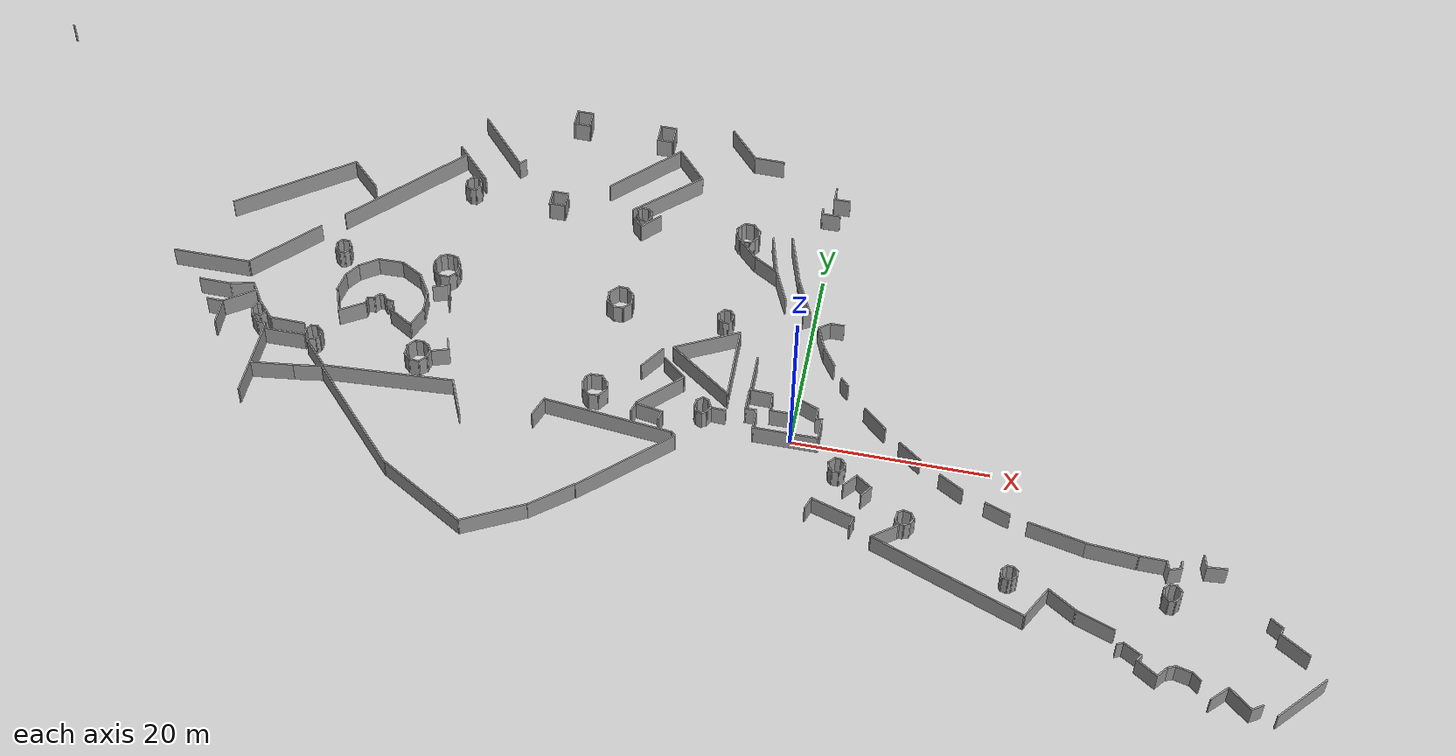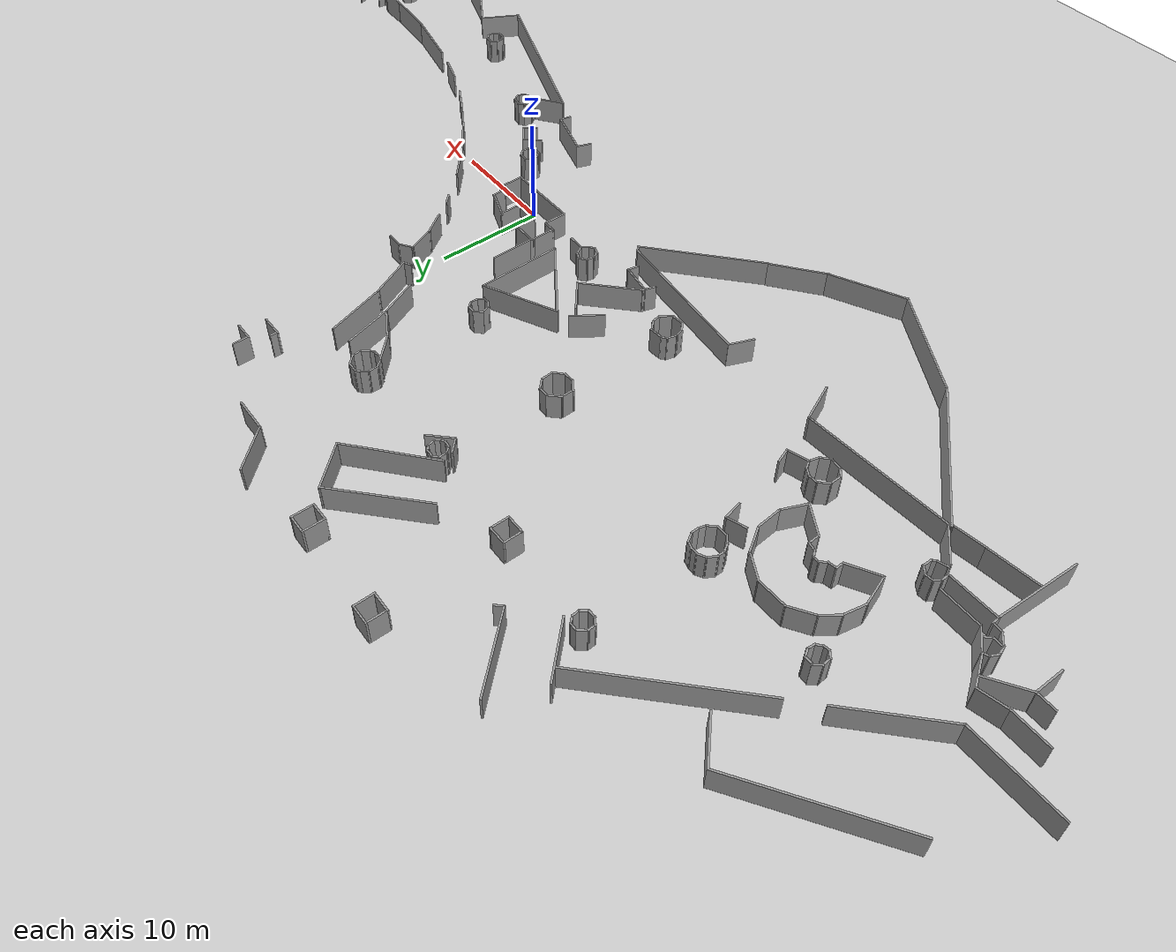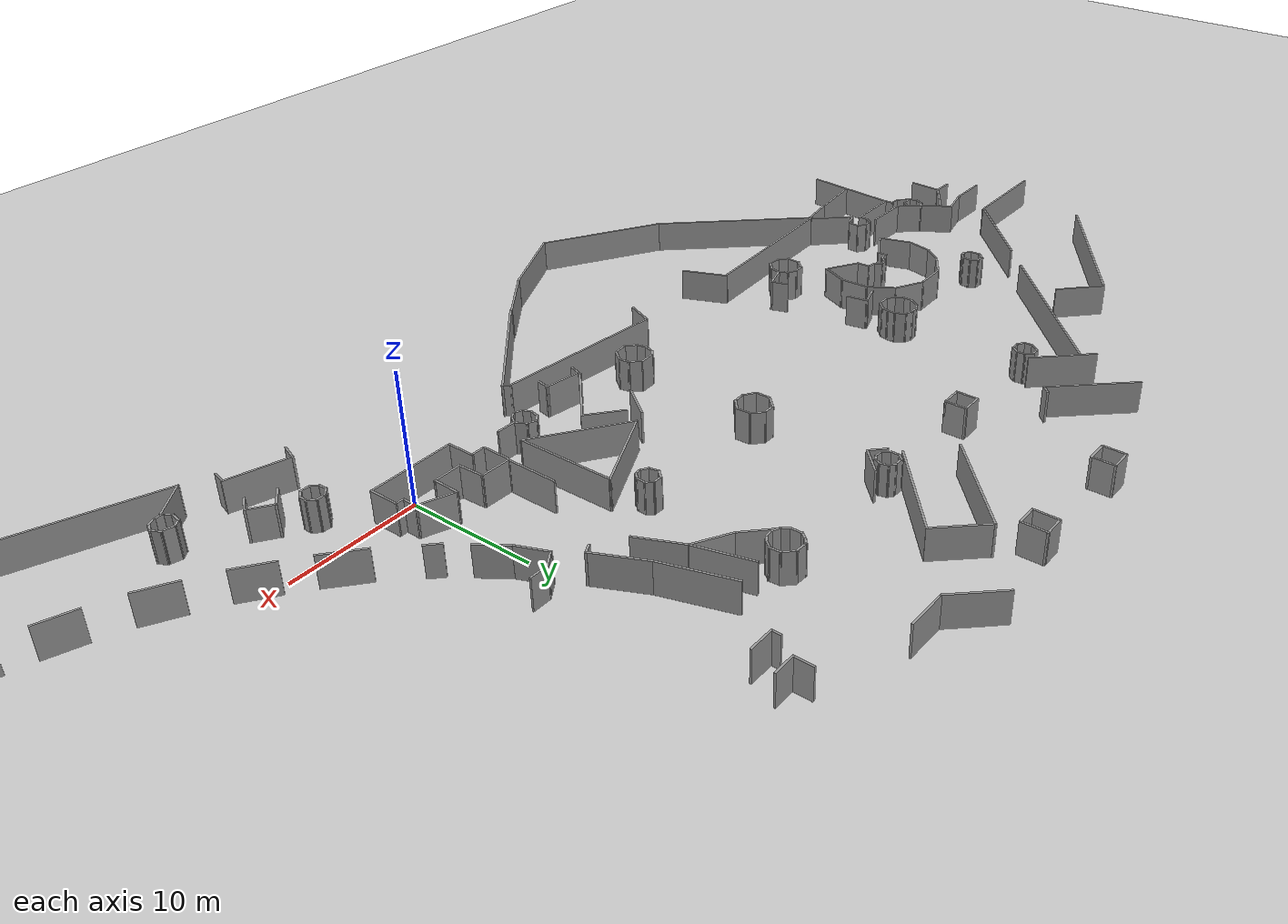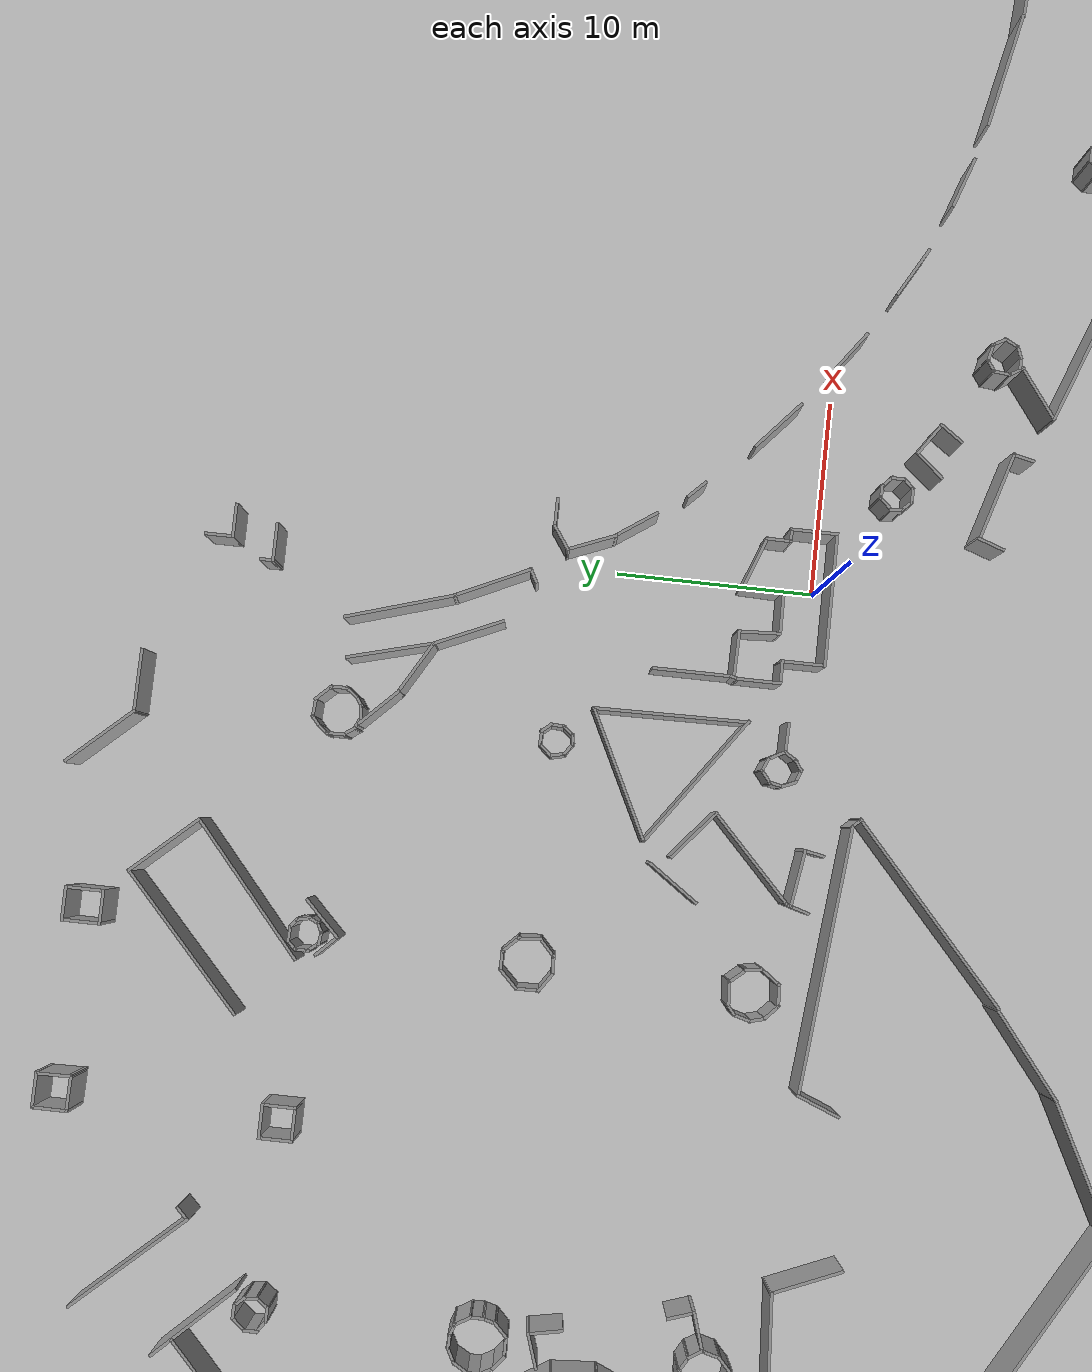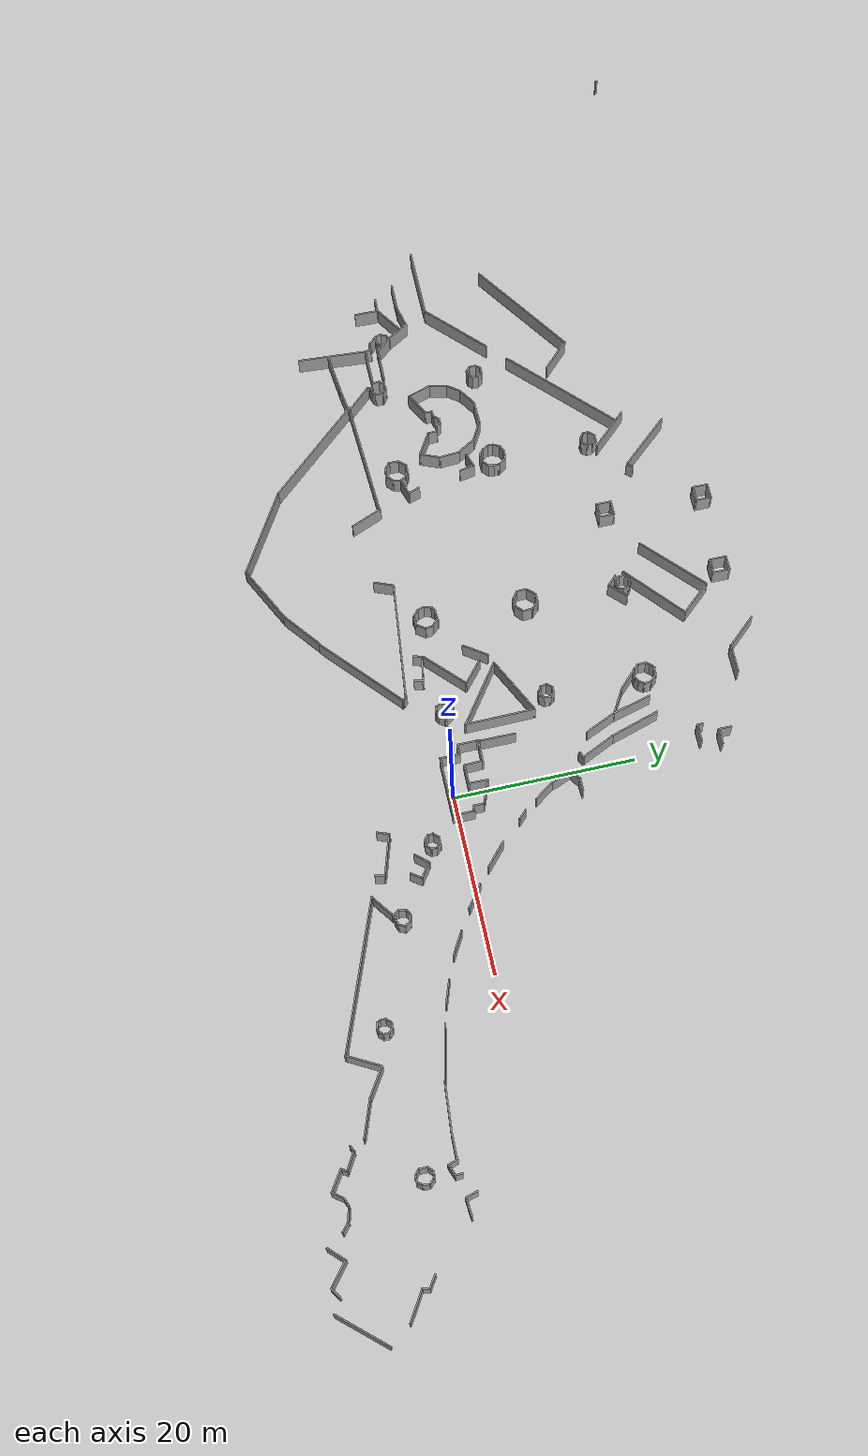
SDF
<?xml version="1.0" ?>
<sdf version="1.5">
  <world name="default">
    <include>
      <uri>model://ground_plane</uri>
    </include>
    <include>
      <uri>model://sun</uri>
    </include>
    <include>
      <uri>model://Ped_mall</uri>
    </include>
  </world>
</sdf>

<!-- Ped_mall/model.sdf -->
<sdf version='1.6'>
  <model name='Ped_mall'>
    <pose frame=''>-15.7128 6.94416 0 0 -0 0</pose>
    <link name='Wall_1'>
      <collision name='Wall_1_Collision'>
        <geometry>
          <box>
            <size>0.25 0.15 2.5</size>
          </box>
        </geometry>
        <pose frame=''>0 0 1.25 0 -0 0</pose>
      </collision>
      <visual name='Wall_1_Visual'>
        <pose frame=''>0 0 1.25 0 -0 0</pose>
        <geometry>
          <box>
            <size>0.25 0.15 2.5</size>
          </box>
        </geometry>
        <material>
          <script>
            <uri>file://media/materials/scripts/gazebo.material</uri>
            <name>Gazebo/Grey</name>
          </script>
          <ambient>1 1 1 1</ambient>
        </material>
        <meta>
          <layer>0</layer>
        </meta>
      </visual>
      <pose frame=''>-69.9119 29.6573 0 0 -0 2.0944</pose>
    </link>
    <link name='Wall_100'>
      <collision name='Wall_100_Collision'>
        <geometry>
          <box>
            <size>0.722221 0.15 2.5</size>
          </box>
        </geometry>
        <pose frame=''>0 0 1.25 0 -0 0</pose>
      </collision>
      <visual name='Wall_100_Visual'>
        <pose frame=''>0 0 1.25 0 -0 0</pose>
        <geometry>
          <box>
            <size>0.722221 0.15 2.5</size>
          </box>
        </geometry>
        <material>
          <script>
            <uri>file://media/materials/scripts/gazebo.material</uri>
            <name>Gazebo/Grey</name>
          </script>
          <ambient>1 1 1 1</ambient>
        </material>
        <meta>
          <layer>0</layer>
        </meta>
      </visual>
      <pose frame=''>6.64236 15.105 0 0 -0 2.70944</pose>
    </link>
    <link name='Wall_101'>
      <collision name='Wall_101_Collision'>
        <geometry>
          <box>
            <size>0.765912 0.15 2.5</size>
          </box>
        </geometry>
        <pose frame=''>0 0 1.25 0 -0 0</pose>
      </collision>
      <visual name='Wall_101_Visual'>
        <pose frame=''>0 0 1.25 0 -0 0</pose>
        <geometry>
          <box>
            <size>0.765912 0.15 2.5</size>
          </box>
        </geometry>
        <material>
          <script>
            <uri>file://media/materials/scripts/gazebo.material</uri>
            <name>Gazebo/Grey</name>
          </script>
          <ambient>1 1 1 1</ambient>
        </material>
        <meta>
          <layer>0</layer>
        </meta>
      </visual>
      <pose frame=''>6.18227 15.4746 0 0 -0 2.19574</pose>
    </link>
    <link name='Wall_102'>
      <collision name='Wall_102_Collision'>
        <geometry>
          <box>
            <size>0.991157 0.15 2.5</size>
          </box>
        </geometry>
        <pose frame=''>0 0 1.25 0 -0 0</pose>
      </collision>
      <visual name='Wall_102_Visual'>
        <pose frame=''>0 0 1.25 0 -0 0</pose>
        <geometry>
          <box>
            <size>0.991157 0.15 2.5</size>
          </box>
        </geometry>
        <material>
          <script>
            <uri>file://media/materials/scripts/gazebo.material</uri>
            <name>Gazebo/Grey</name>
          </script>
          <ambient>1 1 1 1</ambient>
        </material>
        <meta>
          <layer>0</layer>
        </meta>
      </visual>
      <pose frame=''>5.99485 16.1247 0 0 -0 1.58803</pose>
    </link>
    <link name='Wall_103'>
      <collision name='Wall_103_Collision'>
        <geometry>
          <box>
            <size>0.775208 0.15 2.5</size>
          </box>
        </geometry>
        <pose frame=''>0 0 1.25 0 -0 0</pose>
      </collision>
      <visual name='Wall_103_Visual'>
        <pose frame=''>0 0 1.25 0 -0 0</pose>
        <geometry>
          <box>
            <size>0.775208 0.15 2.5</size>
          </box>
        </geometry>
        <material>
          <script>
            <uri>file://media/materials/scripts/gazebo.material</uri>
            <name>Gazebo/Grey</name>
          </script>
          <ambient>1 1 1 1</ambient>
        </material>
        <meta>
          <layer>0</layer>
        </meta>
      </visual>
      <pose frame=''>6.15576 16.7948 0 0 -0 0.924461</pose>
    </link>
    <link name='Wall_104'>
      <collision name='Wall_104_Collision'>
        <geometry>
          <box>
            <size>0.624453 0.15 2.5</size>
          </box>
        </geometry>
        <pose frame=''>0 0 1.25 0 -0 0</pose>
      </collision>
      <visual name='Wall_104_Visual'>
        <pose frame=''>0 0 1.25 0 -0 0</pose>
        <geometry>
          <box>
            <size>0.624453 0.15 2.5</size>
          </box>
        </geometry>
        <material>
          <script>
            <uri>file://media/materials/scripts/gazebo.material</uri>
            <name>Gazebo/Grey</name>
          </script>
          <ambient>1 1 1 1</ambient>
        </material>
        <meta>
          <layer>0</layer>
        </meta>
      </visual>
      <pose frame=''>6.54489 17.198 0 0 -0 0.704554</pose>
    </link>
    <link name='Wall_107'>
      <collision name='Wall_107_Collision'>
        <geometry>
          <box>
            <size>3.08979 0.15 2.5</size>
          </box>
        </geometry>
        <pose frame=''>0 0 1.25 0 -0 0</pose>
      </collision>
      <visual name='Wall_107_Visual'>
        <pose frame=''>0 0 1.25 0 -0 0</pose>
        <geometry>
          <box>
            <size>3.08979 0.15 2.5</size>
          </box>
        </geometry>
        <material>
          <script>
            <uri>file://media/materials/scripts/gazebo.material</uri>
            <name>Gazebo/Grey</name>
          </script>
          <ambient>1 1 1 1</ambient>
        </material>
        <meta>
          <layer>0</layer>
        </meta>
      </visual>
      <pose frame=''>9.67467 12.555 0 0 -0 2.61983</pose>
    </link>
    <link name='Wall_108'>
      <collision name='Wall_108_Collision'>
        <geometry>
          <box>
            <size>2.64222 0.15 2.5</size>
          </box>
        </geometry>
        <pose frame=''>0 0 1.25 0 -0 0</pose>
      </collision>
      <visual name='Wall_108_Visual'>
        <pose frame=''>0 0 1.25 0 -0 0</pose>
        <geometry>
          <box>
            <size>2.64222 0.15 2.5</size>
          </box>
        </geometry>
        <material>
          <script>
            <uri>file://media/materials/scripts/gazebo.material</uri>
            <name>Gazebo/Grey</name>
          </script>
          <ambient>1 1 1 1</ambient>
        </material>
        <meta>
          <layer>0</layer>
        </meta>
      </visual>
      <pose frame=''>7.49911 14.1687 0 0 -0 2.35619</pose>
    </link>
    <link name='Wall_11'>
      <collision name='Wall_11_Collision'>
        <geometry>
          <box>
            <size>14.8505 0.15 2.5</size>
          </box>
        </geometry>
        <pose frame=''>0 0 1.25 0 -0 0</pose>
      </collision>
      <visual name='Wall_11_Visual'>
        <pose frame=''>0 0 1.25 0 -0 0</pose>
        <geometry>
          <box>
            <size>14.8505 0.15 2.5</size>
          </box>
        </geometry>
        <material>
          <script>
            <uri>file://media/materials/scripts/gazebo.material</uri>
            <name>Gazebo/Grey</name>
          </script>
          <ambient>1 1 1 1</ambient>
        </material>
        <meta>
          <layer>0</layer>
        </meta>
      </visual>
      <pose frame=''>-29.1266 15.4957 0 0 -0 0.767596</pose>
    </link>
    <link name='Wall_111'>
      <collision name='Wall_111_Collision'>
        <geometry>
          <box>
            <size>1.5 0.15 2.5</size>
          </box>
        </geometry>
        <pose frame=''>0 0 1.25 0 -0 0</pose>
      </collision>
      <visual name='Wall_111_Visual'>
        <pose frame=''>0 0 1.25 0 -0 0</pose>
        <geometry>
          <box>
            <size>1.5 0.15 2.5</size>
          </box>
        </geometry>
        <material>
          <script>
            <uri>file://media/materials/scripts/gazebo.material</uri>
            <name>Gazebo/Grey</name>
          </script>
          <ambient>1 1 1 1</ambient>
        </material>
        <meta>
          <layer>0</layer>
        </meta>
      </visual>
      <pose frame=''>18.0936 6.49014 0 0 -0 3.14159</pose>
    </link>
    <link name='Wall_112'>
      <collision name='Wall_112_Collision'>
        <geometry>
          <box>
            <size>1.49109 0.15 2.5</size>
          </box>
        </geometry>
        <pose frame=''>0 0 1.25 0 -0 0</pose>
      </collision>
      <visual name='Wall_112_Visual'>
        <pose frame=''>0 0 1.25 0 -0 0</pose>
        <geometry>
          <box>
            <size>1.49109 0.15 2.5</size>
          </box>
        </geometry>
        <material>
          <script>
            <uri>file://media/materials/scripts/gazebo.material</uri>
            <name>Gazebo/Grey</name>
          </script>
          <ambient>1 1 1 1</ambient>
        </material>
        <meta>
          <layer>0</layer>
        </meta>
      </visual>
      <pose frame=''>16.8687 6.10638 0 0 -0 -2.53227</pose>
    </link>
    <link name='Wall_113'>
      <collision name='Wall_113_Collision'>
        <geometry>
          <box>
            <size>2.64669 0.15 2.5</size>
          </box>
        </geometry>
        <pose frame=''>0 0 1.25 0 -0 0</pose>
      </collision>
      <visual name='Wall_113_Visual'>
        <pose frame=''>0 0 1.25 0 -0 0</pose>
        <geometry>
          <box>
            <size>2.64669 0.15 2.5</size>
          </box>
        </geometry>
        <material>
          <script>
            <uri>file://media/materials/scripts/gazebo.material</uri>
            <name>Gazebo/Grey</name>
          </script>
          <ambient>1 1 1 1</ambient>
        </material>
        <meta>
          <layer>0</layer>
        </meta>
      </visual>
      <pose frame=''>16.7849 4.58765 0 0 -0 -1.18822</pose>
    </link>
    <link name='Wall_114'>
      <collision name='Wall_114_Collision'>
        <geometry>
          <box>
            <size>2.52038 0.15 2.5</size>
          </box>
        </geometry>
        <pose frame=''>0 0 1.25 0 -0 0</pose>
      </collision>
      <visual name='Wall_114_Visual'>
        <pose frame=''>0 0 1.25 0 -0 0</pose>
        <geometry>
          <box>
            <size>2.52038 0.15 2.5</size>
          </box>
        </geometry>
        <material>
          <script>
            <uri>file://media/materials/scripts/gazebo.material</uri>
            <name>Gazebo/Grey</name>
          </script>
          <ambient>1 1 1 1</ambient>
        </material>
        <meta>
          <layer>0</layer>
        </meta>
      </visual>
      <pose frame=''>17.924 2.47721 0 0 -0 -0.966781</pose>
    </link>
    <link name='Wall_117'>
      <collision name='Wall_117_Collision'>
        <geometry>
          <box>
            <size>1.25 0.15 2.5</size>
          </box>
        </geometry>
        <pose frame=''>0 0 1.25 0 -0 0</pose>
      </collision>
      <visual name='Wall_117_Visual'>
        <pose frame=''>0 0 1.25 0 -0 0</pose>
        <geometry>
          <box>
            <size>1.25 0.15 2.5</size>
          </box>
        </geometry>
        <material>
          <script>
            <uri>file://media/materials/scripts/gazebo.material</uri>
            <name>Gazebo/Grey</name>
          </script>
          <ambient>1 1 1 1</ambient>
        </material>
        <meta>
          <layer>0</layer>
        </meta>
      </visual>
      <pose frame=''>19.9902 -0.352211 0 0 -0 -0.785398</pose>
    </link>
    <link name='Wall_119'>
      <collision name='Wall_119_Collision'>
        <geometry>
          <box>
            <size>3.25621 0.15 2.5</size>
          </box>
        </geometry>
        <pose frame=''>0 0 1.25 0 -0 0</pose>
      </collision>
      <visual name='Wall_119_Visual'>
        <pose frame=''>0 0 1.25 0 -0 0</pose>
        <geometry>
          <box>
            <size>3.25621 0.15 2.5</size>
          </box>
        </geometry>
        <material>
          <script>
            <uri>file://media/materials/scripts/gazebo.material</uri>
            <name>Gazebo/Grey</name>
          </script>
          <ambient>1 1 1 1</ambient>
        </material>
        <meta>
          <layer>0</layer>
        </meta>
      </visual>
      <pose frame=''>23.658 -4.08943 0 0 -0 -0.72217</pose>
    </link>
    <link name='Wall_122'>
      <collision name='Wall_122_Collision'>
        <geometry>
          <box>
            <size>2.9022 0.15 2.5</size>
          </box>
        </geometry>
        <pose frame=''>0 0 1.25 0 -0 0</pose>
      </collision>
      <visual name='Wall_122_Visual'>
        <pose frame=''>0 0 1.25 0 -0 0</pose>
        <geometry>
          <box>
            <size>2.9022 0.15 2.5</size>
          </box>
        </geometry>
        <material>
          <script>
            <uri>file://media/materials/scripts/gazebo.material</uri>
            <name>Gazebo/Grey</name>
          </script>
          <ambient>1 1 1 1</ambient>
        </material>
        <meta>
          <layer>0</layer>
        </meta>
      </visual>
      <pose frame=''>27.6291 -7.25089 0 0 -0 -0.630264</pose>
    </link>
    <link name='Wall_126'>
      <collision name='Wall_126_Collision'>
        <geometry>
          <box>
            <size>2.90533 0.15 2.5</size>
          </box>
        </geometry>
        <pose frame=''>0 0 1.25 0 -0 0</pose>
      </collision>
      <visual name='Wall_126_Visual'>
        <pose frame=''>0 0 1.25 0 -0 0</pose>
        <geometry>
          <box>
            <size>2.90533 0.15 2.5</size>
          </box>
        </geometry>
        <material>
          <script>
            <uri>file://media/materials/scripts/gazebo.material</uri>
            <name>Gazebo/Grey</name>
          </script>
          <ambient>1 1 1 1</ambient>
        </material>
        <meta>
          <layer>0</layer>
        </meta>
      </visual>
      <pose frame=''>32.1578 -10.0784 0 0 -0 -0.51438</pose>
    </link>
    <link name='Wall_130'>
      <collision name='Wall_130_Collision'>
        <geometry>
          <box>
            <size>2.77786 0.15 2.5</size>
          </box>
        </geometry>
        <pose frame=''>0 0 1.25 0 -0 0</pose>
      </collision>
      <visual name='Wall_130_Visual'>
        <pose frame=''>0 0 1.25 0 -0 0</pose>
        <geometry>
          <box>
            <size>2.77786 0.15 2.5</size>
          </box>
        </geometry>
        <material>
          <script>
            <uri>file://media/materials/scripts/gazebo.material</uri>
            <name>Gazebo/Grey</name>
          </script>
          <ambient>1 1 1 1</ambient>
        </material>
        <meta>
          <layer>0</layer>
        </meta>
      </visual>
      <pose frame=''>37.0111 -12.1902 0 0 -0 -0.333614</pose>
    </link>
    <link name='Wall_134'>
      <collision name='Wall_134_Collision'>
        <geometry>
          <box>
            <size>6.09757 0.15 2.5</size>
          </box>
        </geometry>
        <pose frame=''>0 0 1.25 0 -0 0</pose>
      </collision>
      <visual name='Wall_134_Visual'>
        <pose frame=''>0 0 1.25 0 -0 0</pose>
        <geometry>
          <box>
            <size>6.09757 0.15 2.5</size>
          </box>
        </geometry>
        <material>
          <script>
            <uri>file://media/materials/scripts/gazebo.material</uri>
            <name>Gazebo/Grey</name>
          </script>
          <ambient>1 1 1 1</ambient>
        </material>
        <meta>
          <layer>0</layer>
        </meta>
      </visual>
      <pose frame=''>43.0712 -13.7755 0 0 -0 -0.212708</pose>
    </link>
    <link name='Wall_135'>
      <collision name='Wall_135_Collision'>
        <geometry>
          <box>
            <size>5.31467 0.15 2.5</size>
          </box>
        </geometry>
        <pose frame=''>0 0 1.25 0 -0 0</pose>
      </collision>
      <visual name='Wall_135_Visual'>
        <pose frame=''>0 0 1.25 0 -0 0</pose>
        <geometry>
          <box>
            <size>5.31467 0.15 2.5</size>
          </box>
        </geometry>
        <material>
          <script>
            <uri>file://media/materials/scripts/gazebo.material</uri>
            <name>Gazebo/Grey</name>
          </script>
          <ambient>1 1 1 1</ambient>
        </material>
        <meta>
          <layer>0</layer>
        </meta>
      </visual>
      <pose frame=''>48.5516 -14.6377 0 0 -0 -0.081911</pose>
    </link>
    <link name='Wall_136'>
      <collision name='Wall_136_Collision'>
        <geometry>
          <box>
            <size>2.84038 0.15 2.5</size>
          </box>
        </geometry>
        <pose frame=''>0 0 1.25 0 -0 0</pose>
      </collision>
      <visual name='Wall_136_Visual'>
        <pose frame=''>0 0 1.25 0 -0 0</pose>
        <geometry>
          <box>
            <size>2.84038 0.15 2.5</size>
          </box>
        </geometry>
        <material>
          <script>
            <uri>file://media/materials/scripts/gazebo.material</uri>
            <name>Gazebo/Grey</name>
          </script>
          <ambient>1 1 1 1</ambient>
        </material>
        <meta>
          <layer>0</layer>
        </meta>
      </visual>
      <pose frame=''>52.4934 -14.8722 0 0 -0 -0.017196</pose>
    </link>
    <link name='Wall_137'>
      <collision name='Wall_137_Collision'>
        <geometry>
          <box>
            <size>1.16218 0.15 2.5</size>
          </box>
        </geometry>
        <pose frame=''>0 0 1.25 0 -0 0</pose>
      </collision>
      <visual name='Wall_137_Visual'>
        <pose frame=''>0 0 1.25 0 -0 0</pose>
        <geometry>
          <box>
            <size>1.16218 0.15 2.5</size>
          </box>
        </geometry>
        <material>
          <script>
            <uri>file://media/materials/scripts/gazebo.material</uri>
            <name>Gazebo/Grey</name>
          </script>
          <ambient>1 1 1 1</ambient>
        </material>
        <meta>
          <layer>0</layer>
        </meta>
      </visual>
      <pose frame=''>54.0043 -15.3503 0 0 -0 -1.23687</pose>
    </link>
    <link name='Wall_138'>
      <collision name='Wall_138_Collision'>
        <geometry>
          <box>
            <size>1.37461 0.15 2.5</size>
          </box>
        </geometry>
        <pose frame=''>0 0 1.25 0 -0 0</pose>
      </collision>
      <visual name='Wall_138_Visual'>
        <pose frame=''>0 0 1.25 0 -0 0</pose>
        <geometry>
          <box>
            <size>1.37461 0.15 2.5</size>
          </box>
        </geometry>
        <material>
          <script>
            <uri>file://media/materials/scripts/gazebo.material</uri>
            <name>Gazebo/Grey</name>
          </script>
          <ambient>1 1 1 1</ambient>
        </material>
        <meta>
          <layer>0</layer>
        </meta>
      </visual>
      <pose frame=''>54.7643 -15.6075 0 0 -0 0.369205</pose>
    </link>
    <link name='Wall_139'>
      <collision name='Wall_139_Collision'>
        <geometry>
          <box>
            <size>0.825415 0.15 2.5</size>
          </box>
        </geometry>
        <pose frame=''>0 0 1.25 0 -0 0</pose>
      </collision>
      <visual name='Wall_139_Visual'>
        <pose frame=''>0 0 1.25 0 -0 0</pose>
        <geometry>
          <box>
            <size>0.825415 0.15 2.5</size>
          </box>
        </geometry>
        <material>
          <script>
            <uri>file://media/materials/scripts/gazebo.material</uri>
            <name>Gazebo/Grey</name>
          </script>
          <ambient>1 1 1 1</ambient>
        </material>
        <meta>
          <layer>0</layer>
        </meta>
      </visual>
      <pose frame=''>55.3122 -15.0265 0 0 -0 1.63934</pose>
    </link>
    <link name='Wall_14'>
      <collision name='Wall_14_Collision'>
        <geometry>
          <box>
            <size>8.0507 0.15 2.5</size>
          </box>
        </geometry>
        <pose frame=''>0 0 1.25 0 -0 0</pose>
      </collision>
      <visual name='Wall_14_Visual'>
        <pose frame=''>0 0 1.25 0 -0 0</pose>
        <geometry>
          <box>
            <size>8.0507 0.15 2.5</size>
          </box>
        </geometry>
        <material>
          <script>
            <uri>file://media/materials/scripts/gazebo.material</uri>
            <name>Gazebo/Grey</name>
          </script>
          <ambient>1 1 1 1</ambient>
        </material>
        <meta>
          <layer>0</layer>
        </meta>
      </visual>
      <pose frame=''>-46.5873 2.52723 0 0 -0 0</pose>
    </link>
    <link name='Wall_143'>
      <collision name='Wall_143_Collision'>
        <geometry>
          <box>
            <size>1.4331 0.15 2.5</size>
          </box>
        </geometry>
        <pose frame=''>0 0 1.25 0 -0 0</pose>
      </collision>
      <visual name='Wall_143_Visual'>
        <pose frame=''>0 0 1.25 0 -0 0</pose>
        <geometry>
          <box>
            <size>1.4331 0.15 2.5</size>
          </box>
        </geometry>
        <material>
          <script>
            <uri>file://media/materials/scripts/gazebo.material</uri>
            <name>Gazebo/Grey</name>
          </script>
          <ambient>1 1 1 1</ambient>
        </material>
        <meta>
          <layer>0</layer>
        </meta>
      </visual>
      <pose frame=''>57.502 -14.2045 0 0 -0 -1.295</pose>
    </link>
    <link name='Wall_144'>
      <collision name='Wall_144_Collision'>
        <geometry>
          <box>
            <size>2.09926 0.15 2.5</size>
          </box>
        </geometry>
        <pose frame=''>0 0 1.25 0 -0 0</pose>
      </collision>
      <visual name='Wall_144_Visual'>
        <pose frame=''>0 0 1.25 0 -0 0</pose>
        <geometry>
          <box>
            <size>2.09926 0.15 2.5</size>
          </box>
        </geometry>
        <material>
          <script>
            <uri>file://media/materials/scripts/gazebo.material</uri>
            <name>Gazebo/Grey</name>
          </script>
          <ambient>1 1 1 1</ambient>
        </material>
        <meta>
          <layer>0</layer>
        </meta>
      </visual>
      <pose frame=''>58.6711 -14.7409 0 0 -0 0.08316</pose>
    </link>
    <link name='Wall_147'>
      <collision name='Wall_147_Collision'>
        <geometry>
          <box>
            <size>1.5806 0.15 2.5</size>
          </box>
        </geometry>
        <pose frame=''>0 0 1.25 0 -0 0</pose>
      </collision>
      <visual name='Wall_147_Visual'>
        <pose frame=''>0 0 1.25 0 -0 0</pose>
        <geometry>
          <box>
            <size>1.5806 0.15 2.5</size>
          </box>
        </geometry>
        <material>
          <script>
            <uri>file://media/materials/scripts/gazebo.material</uri>
            <name>Gazebo/Grey</name>
          </script>
          <ambient>1 1 1 1</ambient>
        </material>
        <meta>
          <layer>0</layer>
        </meta>
      </visual>
      <pose frame=''>64.8395 -19.7652 0 0 -0 -0.585566</pose>
    </link>
    <link name='Wall_148'>
      <collision name='Wall_148_Collision'>
        <geometry>
          <box>
            <size>0.867739 0.15 2.5</size>
          </box>
        </geometry>
        <pose frame=''>0 0 1.25 0 -0 0</pose>
      </collision>
      <visual name='Wall_148_Visual'>
        <pose frame=''>0 0 1.25 0 -0 0</pose>
        <geometry>
          <box>
            <size>0.867739 0.15 2.5</size>
          </box>
        </geometry>
        <material>
          <script>
            <uri>file://media/materials/scripts/gazebo.material</uri>
            <name>Gazebo/Grey</name>
          </script>
          <ambient>1 1 1 1</ambient>
        </material>
        <meta>
          <layer>0</layer>
        </meta>
      </visual>
      <pose frame=''>65.3696 -20.5081 0 0 -0 -1.82202</pose>
    </link>
    <link name='Wall_149'>
      <collision name='Wall_149_Collision'>
        <geometry>
          <box>
            <size>3.5713 0.15 2.5</size>
          </box>
        </geometry>
        <pose frame=''>0 0 1.25 0 -0 0</pose>
      </collision>
      <visual name='Wall_149_Visual'>
        <pose frame=''>0 0 1.25 0 -0 0</pose>
        <geometry>
          <box>
            <size>3.5713 0.15 2.5</size>
          </box>
        </geometry>
        <material>
          <script>
            <uri>file://media/materials/scripts/gazebo.material</uri>
            <name>Gazebo/Grey</name>
          </script>
          <ambient>1 1 1 1</ambient>
        </material>
        <meta>
          <layer>0</layer>
        </meta>
      </visual>
      <pose frame=''>66.7351 -21.7789 0 0 -0 -0.554027</pose>
    </link>
    <link name='Wall_15'>
      <collision name='Wall_15_Collision'>
        <geometry>
          <box>
            <size>8.65344 0.15 2.5</size>
          </box>
        </geometry>
        <pose frame=''>0 0 1.25 0 -0 0</pose>
      </collision>
      <visual name='Wall_15_Visual'>
        <pose frame=''>0 0 1.25 0 -0 0</pose>
        <geometry>
          <box>
            <size>8.65344 0.15 2.5</size>
          </box>
        </geometry>
        <material>
          <script>
            <uri>file://media/materials/scripts/gazebo.material</uri>
            <name>Gazebo/Grey</name>
          </script>
          <ambient>1 1 1 1</ambient>
        </material>
        <meta>
          <layer>0</layer>
        </meta>
      </visual>
      <pose frame=''>-39.5964 5.47527 0 0 -0 0.766163</pose>
    </link>
    <link name='Wall_152'>
      <collision name='Wall_152_Collision'>
        <geometry>
          <box>
            <size>0.796261 0.15 2.5</size>
          </box>
        </geometry>
        <pose frame=''>0 0 1.25 0 -0 0</pose>
      </collision>
      <visual name='Wall_152_Visual'>
        <pose frame=''>0 0 1.25 0 -0 0</pose>
        <geometry>
          <box>
            <size>0.796261 0.15 2.5</size>
          </box>
        </geometry>
        <material>
          <script>
            <uri>file://media/materials/scripts/gazebo.material</uri>
            <name>Gazebo/Grey</name>
          </script>
          <ambient>1 1 1 1</ambient>
        </material>
        <meta>
          <layer>0</layer>
        </meta>
      </visual>
      <pose frame=''>54.7591 -17.4732 0 0 -0 0</pose>
    </link>
    <link name='Wall_153'>
      <collision name='Wall_153_Collision'>
        <geometry>
          <box>
            <size>0.913558 0.15 2.5</size>
          </box>
        </geometry>
        <pose frame=''>0 0 1.25 0 -0 0</pose>
      </collision>
      <visual name='Wall_153_Visual'>
        <pose frame=''>0 0 1.25 0 -0 0</pose>
        <geometry>
          <box>
            <size>0.913558 0.15 2.5</size>
          </box>
        </geometry>
        <material>
          <script>
            <uri>file://media/materials/scripts/gazebo.material</uri>
            <name>Gazebo/Grey</name>
          </script>
          <ambient>1 1 1 1</ambient>
        </material>
        <meta>
          <layer>0</layer>
        </meta>
      </visual>
      <pose frame=''>55.3522 -17.7663 0 0 -0 -0.785398</pose>
    </link>
    <link name='Wall_154'>
      <collision name='Wall_154_Collision'>
        <geometry>
          <box>
            <size>0.818566 0.15 2.5</size>
          </box>
        </geometry>
        <pose frame=''>0 0 1.25 0 -0 0</pose>
      </collision>
      <visual name='Wall_154_Visual'>
        <pose frame=''>0 0 1.25 0 -0 0</pose>
        <geometry>
          <box>
            <size>0.818566 0.15 2.5</size>
          </box>
        </geometry>
        <material>
          <script>
            <uri>file://media/materials/scripts/gazebo.material</uri>
            <name>Gazebo/Grey</name>
          </script>
          <ambient>1 1 1 1</ambient>
        </material>
        <meta>
          <layer>0</layer>
        </meta>
      </visual>
      <pose frame=''>55.5875 -18.3918 0 0 -0 -1.67478</pose>
    </link>
    <link name='Wall_155'>
      <collision name='Wall_155_Collision'>
        <geometry>
          <box>
            <size>0.800919 0.15 2.5</size>
          </box>
        </geometry>
        <pose frame=''>0 0 1.25 0 -0 0</pose>
      </collision>
      <visual name='Wall_155_Visual'>
        <pose frame=''>0 0 1.25 0 -0 0</pose>
        <geometry>
          <box>
            <size>0.800919 0.15 2.5</size>
          </box>
        </geometry>
        <material>
          <script>
            <uri>file://media/materials/scripts/gazebo.material</uri>
            <name>Gazebo/Grey</name>
          </script>
          <ambient>1 1 1 1</ambient>
        </material>
        <meta>
          <layer>0</layer>
        </meta>
      </visual>
      <pose frame=''>55.3406 -18.9943 0 0 -0 -2.28074</pose>
    </link>
    <link name='Wall_156'>
      <collision name='Wall_156_Collision'>
        <geometry>
          <box>
            <size>0.824225 0.15 2.5</size>
          </box>
        </geometry>
        <pose frame=''>0 0 1.25 0 -0 0</pose>
      </collision>
      <visual name='Wall_156_Visual'>
        <pose frame=''>0 0 1.25 0 -0 0</pose>
        <geometry>
          <box>
            <size>0.824225 0.15 2.5</size>
          </box>
        </geometry>
        <material>
          <script>
            <uri>file://media/materials/scripts/gazebo.material</uri>
            <name>Gazebo/Grey</name>
          </script>
          <ambient>1 1 1 1</ambient>
        </material>
        <meta>
          <layer>0</layer>
        </meta>
      </visual>
      <pose frame=''>54.8147 -19.2527 0 0 -0 -3.10728</pose>
    </link>
    <link name='Wall_157'>
      <collision name='Wall_157_Collision'>
        <geometry>
          <box>
            <size>0.910565 0.15 2.5</size>
          </box>
        </geometry>
        <pose frame=''>0 0 1.25 0 -0 0</pose>
      </collision>
      <visual name='Wall_157_Visual'>
        <pose frame=''>0 0 1.25 0 -0 0</pose>
        <geometry>
          <box>
            <size>0.910565 0.15 2.5</size>
          </box>
        </geometry>
        <material>
          <script>
            <uri>file://media/materials/scripts/gazebo.material</uri>
            <name>Gazebo/Grey</name>
          </script>
          <ambient>1 1 1 1</ambient>
        </material>
        <meta>
          <layer>0</layer>
        </meta>
      </visual>
      <pose frame=''>54.1949 -19.0333 0 0 -0 2.40987</pose>
    </link>
    <link name='Wall_158'>
      <collision name='Wall_158_Collision'>
        <geometry>
          <box>
            <size>1.00715 0.15 2.5</size>
          </box>
        </geometry>
        <pose frame=''>0 0 1.25 0 -0 0</pose>
      </collision>
      <visual name='Wall_158_Visual'>
        <pose frame=''>0 0 1.25 0 -0 0</pose>
        <geometry>
          <box>
            <size>1.00715 0.15 2.5</size>
          </box>
        </geometry>
        <material>
          <script>
            <uri>file://media/materials/scripts/gazebo.material</uri>
            <name>Gazebo/Grey</name>
          </script>
          <ambient>1 1 1 1</ambient>
        </material>
        <meta>
          <layer>0</layer>
        </meta>
      </visual>
      <pose frame=''>53.9384 -18.3506 0 0 -0 1.56307</pose>
    </link>
    <link name='Wall_159'>
      <collision name='Wall_159_Collision'>
        <geometry>
          <box>
            <size>0.859181 0.15 2.5</size>
          </box>
        </geometry>
        <pose frame=''>0 0 1.25 0 -0 0</pose>
      </collision>
      <visual name='Wall_159_Visual'>
        <pose frame=''>0 0 1.25 0 -0 0</pose>
        <geometry>
          <box>
            <size>0.859181 0.15 2.5</size>
          </box>
        </geometry>
        <material>
          <script>
            <uri>file://media/materials/scripts/gazebo.material</uri>
            <name>Gazebo/Grey</name>
          </script>
          <ambient>1 1 1 1</ambient>
        </material>
        <meta>
          <layer>0</layer>
        </meta>
      </visual>
      <pose frame=''>54.1763 -17.6785 0 0 -0 0.757014</pose>
    </link>
    <link name='Wall_164'>
      <collision name='Wall_164_Collision'>
        <geometry>
          <box>
            <size>6.42585 0.15 2.5</size>
          </box>
        </geometry>
        <pose frame=''>0 0 1.25 0 -0 0</pose>
      </collision>
      <visual name='Wall_164_Visual'>
        <pose frame=''>0 0 1.25 0 -0 0</pose>
        <geometry>
          <box>
            <size>6.42585 0.15 2.5</size>
          </box>
        </geometry>
        <material>
          <script>
            <uri>file://media/materials/scripts/gazebo.material</uri>
            <name>Gazebo/Grey</name>
          </script>
          <ambient>1 1 1 1</ambient>
        </material>
        <meta>
          <layer>0</layer>
        </meta>
      </visual>
      <pose frame=''>67.8578 -27.3439 0 0 -0 -2.29361</pose>
    </link>
    <link name='Wall_168'>
      <collision name='Wall_168_Collision'>
        <geometry>
          <box>
            <size>1.33769 0.15 2.5</size>
          </box>
        </geometry>
        <pose frame=''>0 0 1.25 0 -0 0</pose>
      </collision>
      <visual name='Wall_168_Visual'>
        <pose frame=''>0 0 1.25 0 -0 0</pose>
        <geometry>
          <box>
            <size>1.33769 0.15 2.5</size>
          </box>
        </geometry>
        <material>
          <script>
            <uri>file://media/materials/scripts/gazebo.material</uri>
            <name>Gazebo/Grey</name>
          </script>
          <ambient>1 1 1 1</ambient>
        </material>
        <meta>
          <layer>0</layer>
        </meta>
      </visual>
      <pose frame=''>63.8133 -29.1747 0 0 -0 -2.56999</pose>
    </link>
    <link name='Wall_169'>
      <collision name='Wall_169_Collision'>
        <geometry>
          <box>
            <size>3.13025 0.15 2.5</size>
          </box>
        </geometry>
        <pose frame=''>0 0 1.25 0 -0 0</pose>
      </collision>
      <visual name='Wall_169_Visual'>
        <pose frame=''>0 0 1.25 0 -0 0</pose>
        <geometry>
          <box>
            <size>3.13025 0.15 2.5</size>
          </box>
        </geometry>
        <material>
          <script>
            <uri>file://media/materials/scripts/gazebo.material</uri>
            <name>Gazebo/Grey</name>
          </script>
          <ambient>1 1 1 1</ambient>
        </material>
        <meta>
          <layer>0</layer>
        </meta>
      </visual>
      <pose frame=''>62.1376 -28.5521 0 0 -0 2.45569</pose>
    </link>
    <link name='Wall_170'>
      <collision name='Wall_170_Collision'>
        <geometry>
          <box>
            <size>2.31567 0.15 2.5</size>
          </box>
        </geometry>
        <pose frame=''>0 0 1.25 0 -0 0</pose>
      </collision>
      <visual name='Wall_170_Visual'>
        <pose frame=''>0 0 1.25 0 -0 0</pose>
        <geometry>
          <box>
            <size>2.31567 0.15 2.5</size>
          </box>
        </geometry>
        <material>
          <script>
            <uri>file://media/materials/scripts/gazebo.material</uri>
            <name>Gazebo/Grey</name>
          </script>
          <ambient>1 1 1 1</ambient>
        </material>
        <meta>
          <layer>0</layer>
        </meta>
      </visual>
      <pose frame=''>60.2073 -28.3855 0 0 -0 -2.34109</pose>
    </link>
    <link name='Wall_173'>
      <collision name='Wall_173_Collision'>
        <geometry>
          <box>
            <size>0.800835 0.15 2.5</size>
          </box>
        </geometry>
        <pose frame=''>0 0 1.25 0 -0 0</pose>
      </collision>
      <visual name='Wall_173_Visual'>
        <pose frame=''>0 0 1.25 0 -0 0</pose>
        <geometry>
          <box>
            <size>0.800835 0.15 2.5</size>
          </box>
        </geometry>
        <material>
          <script>
            <uri>file://media/materials/scripts/gazebo.material</uri>
            <name>Gazebo/Grey</name>
          </script>
          <ambient>1 1 1 1</ambient>
        </material>
        <meta>
          <layer>0</layer>
        </meta>
      </visual>
      <pose frame=''>50.4513 -24.8522 0 0 -0 0.439411</pose>
    </link>
    <link name='Wall_174'>
      <collision name='Wall_174_Collision'>
        <geometry>
          <box>
            <size>2.25 0.15 2.5</size>
          </box>
        </geometry>
        <pose frame=''>0 0 1.25 0 -0 0</pose>
      </collision>
      <visual name='Wall_174_Visual'>
        <pose frame=''>0 0 1.25 0 -0 0</pose>
        <geometry>
          <box>
            <size>2.25 0.15 2.5</size>
          </box>
        </geometry>
        <material>
          <script>
            <uri>file://media/materials/scripts/gazebo.material</uri>
            <name>Gazebo/Grey</name>
          </script>
          <ambient>1 1 1 1</ambient>
        </material>
        <meta>
          <layer>0</layer>
        </meta>
      </visual>
      <pose frame=''>51.632 -25.2387 0 0 -0 -0.523599</pose>
    </link>
    <link name='Wall_175'>
      <collision name='Wall_175_Collision'>
        <geometry>
          <box>
            <size>0.806524 0.15 2.5</size>
          </box>
        </geometry>
        <pose frame=''>0 0 1.25 0 -0 0</pose>
      </collision>
      <visual name='Wall_175_Visual'>
        <pose frame=''>0 0 1.25 0 -0 0</pose>
        <geometry>
          <box>
            <size>0.806524 0.15 2.5</size>
          </box>
        </geometry>
        <material>
          <script>
            <uri>file://media/materials/scripts/gazebo.material</uri>
            <name>Gazebo/Grey</name>
          </script>
          <ambient>1 1 1 1</ambient>
        </material>
        <meta>
          <layer>0</layer>
        </meta>
      </visual>
      <pose frame=''>52.3798 -26.0351 0 0 -0 -2.16838</pose>
    </link>
    <link name='Wall_176'>
      <collision name='Wall_176_Collision'>
        <geometry>
          <box>
            <size>2.58445 0.15 2.5</size>
          </box>
        </geometry>
        <pose frame=''>0 0 1.25 0 -0 0</pose>
      </collision>
      <visual name='Wall_176_Visual'>
        <pose frame=''>0 0 1.25 0 -0 0</pose>
        <geometry>
          <box>
            <size>2.58445 0.15 2.5</size>
          </box>
        </geometry>
        <material>
          <script>
            <uri>file://media/materials/scripts/gazebo.material</uri>
            <name>Gazebo/Grey</name>
          </script>
          <ambient>1 1 1 1</ambient>
        </material>
        <meta>
          <layer>0</layer>
        </meta>
      </visual>
      <pose frame=''>53.2168 -26.9912 0 0 -0 -0.574606</pose>
    </link>
    <link name='Wall_177'>
      <collision name='Wall_177_Collision'>
        <geometry>
          <box>
            <size>1.53379 0.15 2.5</size>
          </box>
        </geometry>
        <pose frame=''>0 0 1.25 0 -0 0</pose>
      </collision>
      <visual name='Wall_177_Visual'>
        <pose frame=''>0 0 1.25 0 -0 0</pose>
        <geometry>
          <box>
            <size>1.53379 0.15 2.5</size>
          </box>
        </geometry>
        <material>
          <script>
            <uri>file://media/materials/scripts/gazebo.material</uri>
            <name>Gazebo/Grey</name>
          </script>
          <ambient>1 1 1 1</ambient>
        </material>
        <meta>
          <layer>0</layer>
        </meta>
      </visual>
      <pose frame=''>54.6871 -27.1071 0 0 -0 0.908714</pose>
    </link>
    <link name='Wall_178'>
      <collision name='Wall_178_Collision'>
        <geometry>
          <box>
            <size>0.920117 0.15 2.5</size>
          </box>
        </geometry>
        <pose frame=''>0 0 1.25 0 -0 0</pose>
      </collision>
      <visual name='Wall_178_Visual'>
        <pose frame=''>0 0 1.25 0 -0 0</pose>
        <geometry>
          <box>
            <size>0.920117 0.15 2.5</size>
          </box>
        </geometry>
        <material>
          <script>
            <uri>file://media/materials/scripts/gazebo.material</uri>
            <name>Gazebo/Grey</name>
          </script>
          <ambient>1 1 1 1</ambient>
        </material>
        <meta>
          <layer>0</layer>
        </meta>
      </visual>
      <pose frame=''>55.4933 -26.419 0 0 -0 0.37867</pose>
    </link>
    <link name='Wall_179'>
      <collision name='Wall_179_Collision'>
        <geometry>
          <box>
            <size>1.78854 0.15 2.5</size>
          </box>
        </geometry>
        <pose frame=''>0 0 1.25 0 -0 0</pose>
      </collision>
      <visual name='Wall_179_Visual'>
        <pose frame=''>0 0 1.25 0 -0 0</pose>
        <geometry>
          <box>
            <size>1.78854 0.15 2.5</size>
          </box>
        </geometry>
        <material>
          <script>
            <uri>file://media/materials/scripts/gazebo.material</uri>
            <name>Gazebo/Grey</name>
          </script>
          <ambient>1 1 1 1</ambient>
        </material>
        <meta>
          <layer>0</layer>
        </meta>
      </visual>
      <pose frame=''>56.6715 -26.4653 0 0 -0 -0.232304</pose>
    </link>
    <link name='Wall_18'>
      <collision name='Wall_18_Collision'>
        <geometry>
          <box>
            <size>0.690093 0.15 2.5</size>
          </box>
        </geometry>
        <pose frame=''>0 0 1.25 0 -0 0</pose>
      </collision>
      <visual name='Wall_18_Visual'>
        <pose frame=''>0 0 1.25 0 -0 0</pose>
        <geometry>
          <box>
            <size>0.690093 0.15 2.5</size>
          </box>
        </geometry>
        <material>
          <script>
            <uri>file://media/materials/scripts/gazebo.material</uri>
            <name>Gazebo/Grey</name>
          </script>
          <ambient>1 1 1 1</ambient>
        </material>
        <meta>
          <layer>0</layer>
        </meta>
      </visual>
      <pose frame=''>-22.1764 17.8232 0 0 -0 -0.018516</pose>
    </link>
    <link name='Wall_180'>
      <collision name='Wall_180_Collision'>
        <geometry>
          <box>
            <size>1.24879 0.15 2.5</size>
          </box>
        </geometry>
        <pose frame=''>0 0 1.25 0 -0 0</pose>
      </collision>
      <visual name='Wall_180_Visual'>
        <pose frame=''>0 0 1.25 0 -0 0</pose>
        <geometry>
          <box>
            <size>1.24879 0.15 2.5</size>
          </box>
        </geometry>
        <material>
          <script>
            <uri>file://media/materials/scripts/gazebo.material</uri>
            <name>Gazebo/Grey</name>
          </script>
          <ambient>1 1 1 1</ambient>
        </material>
        <meta>
          <layer>0</layer>
        </meta>
      </visual>
      <pose frame=''>57.8641 -26.9867 0 0 -0 -0.704831</pose>
    </link>
    <link name='Wall_184'>
      <collision name='Wall_184_Collision'>
        <geometry>
          <box>
            <size>4.27204 0.15 2.5</size>
          </box>
        </geometry>
        <pose frame=''>0 0 1.25 0 -0 0</pose>
      </collision>
      <visual name='Wall_184_Visual'>
        <pose frame=''>0 0 1.25 0 -0 0</pose>
        <geometry>
          <box>
            <size>4.27204 0.15 2.5</size>
          </box>
        </geometry>
        <material>
          <script>
            <uri>file://media/materials/scripts/gazebo.material</uri>
            <name>Gazebo/Grey</name>
          </script>
          <ambient>1 1 1 1</ambient>
        </material>
        <meta>
          <layer>0</layer>
        </meta>
      </visual>
      <pose frame=''>47.8232 -22.7923 0 0 -0 2.79772</pose>
    </link>
    <link name='Wall_185'>
      <collision name='Wall_185_Collision'>
        <geometry>
          <box>
            <size>3.56395 0.15 2.5</size>
          </box>
        </geometry>
        <pose frame=''>0 0 1.25 0 -0 0</pose>
      </collision>
      <visual name='Wall_185_Visual'>
        <pose frame=''>0 0 1.25 0 -0 0</pose>
        <geometry>
          <box>
            <size>3.56395 0.15 2.5</size>
          </box>
        </geometry>
        <material>
          <script>
            <uri>file://media/materials/scripts/gazebo.material</uri>
            <name>Gazebo/Grey</name>
          </script>
          <ambient>1 1 1 1</ambient>
        </material>
        <meta>
          <layer>0</layer>
        </meta>
      </visual>
      <pose frame=''>44.4628 -21.1859 0 0 -0 2.57824</pose>
    </link>
    <link name='Wall_186'>
      <collision name='Wall_186_Collision'>
        <geometry>
          <box>
            <size>4.01477 0.15 2.5</size>
          </box>
        </geometry>
        <pose frame=''>0 0 1.25 0 -0 0</pose>
      </collision>
      <visual name='Wall_186_Visual'>
        <pose frame=''>0 0 1.25 0 -0 0</pose>
        <geometry>
          <box>
            <size>4.01477 0.15 2.5</size>
          </box>
        </geometry>
        <material>
          <script>
            <uri>file://media/materials/scripts/gazebo.material</uri>
            <name>Gazebo/Grey</name>
          </script>
          <ambient>1 1 1 1</ambient>
        </material>
        <meta>
          <layer>0</layer>
        </meta>
      </visual>
      <pose frame=''>42.0734 -21.972 0 0 -0 -2.06885</pose>
    </link>
    <link name='Wall_187'>
      <collision name='Wall_187_Collision'>
        <geometry>
          <box>
            <size>16.993 0.15 2.5</size>
          </box>
        </geometry>
        <pose frame=''>0 0 1.25 0 -0 0</pose>
      </collision>
      <visual name='Wall_187_Visual'>
        <pose frame=''>0 0 1.25 0 -0 0</pose>
        <geometry>
          <box>
            <size>16.993 0.15 2.5</size>
          </box>
        </geometry>
        <material>
          <script>
            <uri>file://media/materials/scripts/gazebo.material</uri>
            <name>Gazebo/Grey</name>
          </script>
          <ambient>1 1 1 1</ambient>
        </material>
        <meta>
          <layer>0</layer>
        </meta>
      </visual>
      <pose frame=''>33.2927 -20.7004 0 0 -0 2.78127</pose>
    </link>
    <link name='Wall_188'>
      <collision name='Wall_188_Collision'>
        <geometry>
          <box>
            <size>3.16757 0.15 2.5</size>
          </box>
        </geometry>
        <pose frame=''>0 0 1.25 0 -0 0</pose>
      </collision>
      <visual name='Wall_188_Visual'>
        <pose frame=''>0 0 1.25 0 -0 0</pose>
        <geometry>
          <box>
            <size>3.16757 0.15 2.5</size>
          </box>
        </geometry>
        <material>
          <script>
            <uri>file://media/materials/scripts/gazebo.material</uri>
            <name>Gazebo/Grey</name>
          </script>
          <ambient>1 1 1 1</ambient>
        </material>
        <meta>
          <layer>0</layer>
        </meta>
      </visual>
      <pose frame=''>26.6049 -16.8381 0 0 -0 0.633463</pose>
    </link>
    <link name='Wall_189'>
      <collision name='Wall_189_Collision'>
        <geometry>
          <box>
            <size>0.924987 0.15 2.5</size>
          </box>
        </geometry>
        <pose frame=''>0 0 1.25 0 -0 0</pose>
      </collision>
      <visual name='Wall_189_Visual'>
        <pose frame=''>0 0 1.25 0 -0 0</pose>
        <geometry>
          <box>
            <size>0.924987 0.15 2.5</size>
          </box>
        </geometry>
        <material>
          <script>
            <uri>file://media/materials/scripts/gazebo.material</uri>
            <name>Gazebo/Grey</name>
          </script>
          <ambient>1 1 1 1</ambient>
        </material>
        <meta>
          <layer>0</layer>
        </meta>
      </visual>
      <pose frame=''>27.6129 -15.6412 0 0 -0 2.13761</pose>
    </link>
    <link name='Wall_19'>
      <collision name='Wall_19_Collision'>
        <geometry>
          <box>
            <size>0.764793 0.15 2.5</size>
          </box>
        </geometry>
        <pose frame=''>0 0 1.25 0 -0 0</pose>
      </collision>
      <visual name='Wall_19_Visual'>
        <pose frame=''>0 0 1.25 0 -0 0</pose>
        <geometry>
          <box>
            <size>0.764793 0.15 2.5</size>
          </box>
        </geometry>
        <material>
          <script>
            <uri>file://media/materials/scripts/gazebo.material</uri>
            <name>Gazebo/Grey</name>
          </script>
          <ambient>1 1 1 1</ambient>
        </material>
        <meta>
          <layer>0</layer>
        </meta>
      </visual>
      <pose frame=''>-21.6893 17.5911 0 0 -0 -0.831421</pose>
    </link>
    <link name='Wall_190'>
      <collision name='Wall_190_Collision'>
        <geometry>
          <box>
            <size>0.941002 0.15 2.5</size>
          </box>
        </geometry>
        <pose frame=''>0 0 1.25 0 -0 0</pose>
      </collision>
      <visual name='Wall_190_Visual'>
        <pose frame=''>0 0 1.25 0 -0 0</pose>
        <geometry>
          <box>
            <size>0.941002 0.15 2.5</size>
          </box>
        </geometry>
        <material>
          <script>
            <uri>file://media/materials/scripts/gazebo.material</uri>
            <name>Gazebo/Grey</name>
          </script>
          <ambient>1 1 1 1</ambient>
        </material>
        <meta>
          <layer>0</layer>
        </meta>
      </visual>
      <pose frame=''>27.4719 -14.9213 0 0 -0 1.45949</pose>
    </link>
    <link name='Wall_191'>
      <collision name='Wall_191_Collision'>
        <geometry>
          <box>
            <size>0.738082 0.15 2.5</size>
          </box>
        </geometry>
        <pose frame=''>0 0 1.25 0 -0 0</pose>
      </collision>
      <visual name='Wall_191_Visual'>
        <pose frame=''>0 0 1.25 0 -0 0</pose>
        <geometry>
          <box>
            <size>0.738082 0.15 2.5</size>
          </box>
        </geometry>
        <material>
          <script>
            <uri>file://media/materials/scripts/gazebo.material</uri>
            <name>Gazebo/Grey</name>
          </script>
          <ambient>1 1 1 1</ambient>
        </material>
        <meta>
          <layer>0</layer>
        </meta>
      </visual>
      <pose frame=''>27.7763 -14.3548 0 0 -0 0.63104</pose>
    </link>
    <link name='Wall_192'>
      <collision name='Wall_192_Collision'>
        <geometry>
          <box>
            <size>0.984808 0.15 2.5</size>
          </box>
        </geometry>
        <pose frame=''>0 0 1.25 0 -0 0</pose>
      </collision>
      <visual name='Wall_192_Visual'>
        <pose frame=''>0 0 1.25 0 -0 0</pose>
        <geometry>
          <box>
            <size>0.984808 0.15 2.5</size>
          </box>
        </geometry>
        <material>
          <script>
            <uri>file://media/materials/scripts/gazebo.material</uri>
            <name>Gazebo/Grey</name>
          </script>
          <ambient>1 1 1 1</ambient>
        </material>
        <meta>
          <layer>0</layer>
        </meta>
      </visual>
      <pose frame=''>28.4429 -14.2781 0 0 -0 -0.234201</pose>
    </link>
    <link name='Wall_193'>
      <collision name='Wall_193_Collision'>
        <geometry>
          <box>
            <size>0.840157 0.15 2.5</size>
          </box>
        </geometry>
        <pose frame=''>0 0 1.25 0 -0 0</pose>
      </collision>
      <visual name='Wall_193_Visual'>
        <pose frame=''>0 0 1.25 0 -0 0</pose>
        <geometry>
          <box>
            <size>0.840157 0.15 2.5</size>
          </box>
        </geometry>
        <material>
          <script>
            <uri>file://media/materials/scripts/gazebo.material</uri>
            <name>Gazebo/Grey</name>
          </script>
          <ambient>1 1 1 1</ambient>
        </material>
        <meta>
          <layer>0</layer>
        </meta>
      </visual>
      <pose frame=''>29.0182 -14.6526 0 0 -0 -1.05803</pose>
    </link>
    <link name='Wall_194'>
      <collision name='Wall_194_Collision'>
        <geometry>
          <box>
            <size>0.855126 0.15 2.5</size>
          </box>
        </geometry>
        <pose frame=''>0 0 1.25 0 -0 0</pose>
      </collision>
      <visual name='Wall_194_Visual'>
        <pose frame=''>0 0 1.25 0 -0 0</pose>
        <geometry>
          <box>
            <size>0.855126 0.15 2.5</size>
          </box>
        </geometry>
        <material>
          <script>
            <uri>file://media/materials/scripts/gazebo.material</uri>
            <name>Gazebo/Grey</name>
          </script>
          <ambient>1 1 1 1</ambient>
        </material>
        <meta>
          <layer>0</layer>
        </meta>
      </visual>
      <pose frame=''>29.0484 -15.2663 0 0 -0 -2.0489</pose>
    </link>
    <link name='Wall_195'>
      <collision name='Wall_195_Collision'>
        <geometry>
          <box>
            <size>0.750733 0.15 2.5</size>
          </box>
        </geometry>
        <pose frame=''>0 0 1.25 0 -0 0</pose>
      </collision>
      <visual name='Wall_195_Visual'>
        <pose frame=''>0 0 1.25 0 -0 0</pose>
        <geometry>
          <box>
            <size>0.750733 0.15 2.5</size>
          </box>
        </geometry>
        <material>
          <script>
            <uri>file://media/materials/scripts/gazebo.material</uri>
            <name>Gazebo/Grey</name>
          </script>
          <ambient>1 1 1 1</ambient>
        </material>
        <meta>
          <layer>0</layer>
        </meta>
      </visual>
      <pose frame=''>28.6044 -15.7066 0 0 -0 -2.78772</pose>
    </link>
    <link name='Wall_196'>
      <collision name='Wall_196_Collision'>
        <geometry>
          <box>
            <size>0.681691 0.15 2.5</size>
          </box>
        </geometry>
        <pose frame=''>0 0 1.25 0 -0 0</pose>
      </collision>
      <visual name='Wall_196_Visual'>
        <pose frame=''>0 0 1.25 0 -0 0</pose>
        <geometry>
          <box>
            <size>0.681691 0.15 2.5</size>
          </box>
        </geometry>
        <material>
          <script>
            <uri>file://media/materials/scripts/gazebo.material</uri>
            <name>Gazebo/Grey</name>
          </script>
          <ambient>1 1 1 1</ambient>
        </material>
        <meta>
          <layer>0</layer>
        </meta>
      </visual>
      <pose frame=''>28.08 -15.8083 0 0 -0 3.13283</pose>
    </link>
    <link name='Wall_2'>
      <collision name='Wall_2_Collision'>
        <geometry>
          <box>
            <size>0.25 0.15 2.5</size>
          </box>
        </geometry>
        <pose frame=''>0 0 1.25 0 -0 0</pose>
      </collision>
      <visual name='Wall_2_Visual'>
        <pose frame=''>0 0 1.25 0 -0 0</pose>
        <geometry>
          <box>
            <size>0.25 0.15 2.5</size>
          </box>
        </geometry>
        <material>
          <script>
            <uri>file://media/materials/scripts/gazebo.material</uri>
            <name>Gazebo/Grey</name>
          </script>
          <ambient>1 1 1 1</ambient>
        </material>
        <meta>
          <layer>0</layer>
        </meta>
      </visual>
      <pose frame=''>-69.8853 29.6573 0 0 -0 -1.0472</pose>
    </link>
    <link name='Wall_20'>
      <collision name='Wall_20_Collision'>
        <geometry>
          <box>
            <size>0.743043 0.15 2.5</size>
          </box>
        </geometry>
        <pose frame=''>0 0 1.25 0 -0 0</pose>
      </collision>
      <visual name='Wall_20_Visual'>
        <pose frame=''>0 0 1.25 0 -0 0</pose>
        <geometry>
          <box>
            <size>0.743043 0.15 2.5</size>
          </box>
        </geometry>
        <material>
          <script>
            <uri>file://media/materials/scripts/gazebo.material</uri>
            <name>Gazebo/Grey</name>
          </script>
          <ambient>1 1 1 1</ambient>
        </material>
        <meta>
          <layer>0</layer>
        </meta>
      </visual>
      <pose frame=''>-21.4621 17.0689 0 0 -0 -1.46945</pose>
    </link>
    <link name='Wall_21'>
      <collision name='Wall_21_Collision'>
        <geometry>
          <box>
            <size>0.828863 0.15 2.5</size>
          </box>
        </geometry>
        <pose frame=''>0 0 1.25 0 -0 0</pose>
      </collision>
      <visual name='Wall_21_Visual'>
        <pose frame=''>0 0 1.25 0 -0 0</pose>
        <geometry>
          <box>
            <size>0.828863 0.15 2.5</size>
          </box>
        </geometry>
        <material>
          <script>
            <uri>file://media/materials/scripts/gazebo.material</uri>
            <name>Gazebo/Grey</name>
          </script>
          <ambient>1 1 1 1</ambient>
        </material>
        <meta>
          <layer>0</layer>
        </meta>
      </visual>
      <pose frame=''>-21.6324 16.4899 0 0 -0 -2.20196</pose>
    </link>
    <link name='Wall_217'>
      <collision name='Wall_217_Collision'>
        <geometry>
          <box>
            <size>0.796675 0.15 2.5</size>
          </box>
        </geometry>
        <pose frame=''>0 0 1.25 0 -0 0</pose>
      </collision>
      <visual name='Wall_217_Visual'>
        <pose frame=''>0 0 1.25 0 -0 0</pose>
        <geometry>
          <box>
            <size>0.796675 0.15 2.5</size>
          </box>
        </geometry>
        <material>
          <script>
            <uri>file://media/materials/scripts/gazebo.material</uri>
            <name>Gazebo/Grey</name>
          </script>
          <ambient>1 1 1 1</ambient>
        </material>
        <meta>
          <layer>0</layer>
        </meta>
      </visual>
      <pose frame=''>39.1228 -18.4331 0 0 -0 -0.035776</pose>
    </link>
    <link name='Wall_218'>
      <collision name='Wall_218_Collision'>
        <geometry>
          <box>
            <size>0.75 0.15 2.5</size>
          </box>
        </geometry>
        <pose frame=''>0 0 1.25 0 -0 0</pose>
      </collision>
      <visual name='Wall_218_Visual'>
        <pose frame=''>0 0 1.25 0 -0 0</pose>
        <geometry>
          <box>
            <size>0.75 0.15 2.5</size>
          </box>
        </geometry>
        <material>
          <script>
            <uri>file://media/materials/scripts/gazebo.material</uri>
            <name>Gazebo/Grey</name>
          </script>
          <ambient>1 1 1 1</ambient>
        </material>
        <meta>
          <layer>0</layer>
        </meta>
      </visual>
      <pose frame=''>39.6581 -18.6568 0 0 -0 -0.785398</pose>
    </link>
    <link name='Wall_219'>
      <collision name='Wall_219_Collision'>
        <geometry>
          <box>
            <size>0.75 0.15 2.5</size>
          </box>
        </geometry>
        <pose frame=''>0 0 1.25 0 -0 0</pose>
      </collision>
      <visual name='Wall_219_Visual'>
        <pose frame=''>0 0 1.25 0 -0 0</pose>
        <geometry>
          <box>
            <size>0.75 0.15 2.5</size>
          </box>
        </geometry>
        <material>
          <script>
            <uri>file://media/materials/scripts/gazebo.material</uri>
            <name>Gazebo/Grey</name>
          </script>
          <ambient>1 1 1 1</ambient>
        </material>
        <meta>
          <layer>0</layer>
        </meta>
      </visual>
      <pose frame=''>39.8702 -19.1689 0 0 -0 -1.5708</pose>
    </link>
    <link name='Wall_22'>
      <collision name='Wall_22_Collision'>
        <geometry>
          <box>
            <size>0.777532 0.15 2.5</size>
          </box>
        </geometry>
        <pose frame=''>0 0 1.25 0 -0 0</pose>
      </collision>
      <visual name='Wall_22_Visual'>
        <pose frame=''>0 0 1.25 0 -0 0</pose>
        <geometry>
          <box>
            <size>0.777532 0.15 2.5</size>
          </box>
        </geometry>
        <material>
          <script>
            <uri>file://media/materials/scripts/gazebo.material</uri>
            <name>Gazebo/Grey</name>
          </script>
          <ambient>1 1 1 1</ambient>
        </material>
        <meta>
          <layer>0</layer>
        </meta>
      </visual>
      <pose frame=''>-22.1465 16.2221 0 0 -0 -3.12966</pose>
    </link>
    <link name='Wall_220'>
      <collision name='Wall_220_Collision'>
        <geometry>
          <box>
            <size>0.75 0.15 2.5</size>
          </box>
        </geometry>
        <pose frame=''>0 0 1.25 0 -0 0</pose>
      </collision>
      <visual name='Wall_220_Visual'>
        <pose frame=''>0 0 1.25 0 -0 0</pose>
        <geometry>
          <box>
            <size>0.75 0.15 2.5</size>
          </box>
        </geometry>
        <material>
          <script>
            <uri>file://media/materials/scripts/gazebo.material</uri>
            <name>Gazebo/Grey</name>
          </script>
          <ambient>1 1 1 1</ambient>
        </material>
        <meta>
          <layer>0</layer>
        </meta>
      </visual>
      <pose frame=''>39.6581 -19.6811 0 0 -0 -2.35619</pose>
    </link>
    <link name='Wall_221'>
      <collision name='Wall_221_Collision'>
        <geometry>
          <box>
            <size>0.5 0.15 2.5</size>
          </box>
        </geometry>
        <pose frame=''>0 0 1.25 0 -0 0</pose>
      </collision>
      <visual name='Wall_221_Visual'>
        <pose frame=''>0 0 1.25 0 -0 0</pose>
        <geometry>
          <box>
            <size>0.5 0.15 2.5</size>
          </box>
        </geometry>
        <material>
          <script>
            <uri>file://media/materials/scripts/gazebo.material</uri>
            <name>Gazebo/Grey</name>
          </script>
          <ambient>1 1 1 1</ambient>
        </material>
        <meta>
          <layer>0</layer>
        </meta>
      </visual>
      <pose frame=''>39.2769 -19.9385 0 0 -0 -2.87979</pose>
    </link>
    <link name='Wall_222'>
      <collision name='Wall_222_Collision'>
        <geometry>
          <box>
            <size>0.75 0.15 2.5</size>
          </box>
        </geometry>
        <pose frame=''>0 0 1.25 0 -0 0</pose>
      </collision>
      <visual name='Wall_222_Visual'>
        <pose frame=''>0 0 1.25 0 -0 0</pose>
        <geometry>
          <box>
            <size>0.75 0.15 2.5</size>
          </box>
        </geometry>
        <material>
          <script>
            <uri>file://media/materials/scripts/gazebo.material</uri>
            <name>Gazebo/Grey</name>
          </script>
          <ambient>1 1 1 1</ambient>
        </material>
        <meta>
          <layer>0</layer>
        </meta>
      </visual>
      <pose frame=''>38.8181 -19.9061 0 0 -0 2.87979</pose>
    </link>
    <link name='Wall_223'>
      <collision name='Wall_223_Collision'>
        <geometry>
          <box>
            <size>0.5 0.15 2.5</size>
          </box>
        </geometry>
        <pose frame=''>0 0 1.25 0 -0 0</pose>
      </collision>
      <visual name='Wall_223_Visual'>
        <pose frame=''>0 0 1.25 0 -0 0</pose>
        <geometry>
          <box>
            <size>0.5 0.15 2.5</size>
          </box>
        </geometry>
        <material>
          <script>
            <uri>file://media/materials/scripts/gazebo.material</uri>
            <name>Gazebo/Grey</name>
          </script>
          <ambient>1 1 1 1</ambient>
        </material>
        <meta>
          <layer>0</layer>
        </meta>
      </visual>
      <pose frame=''>38.4408 -19.6769 0 0 -0 2.0944</pose>
    </link>
    <link name='Wall_224'>
      <collision name='Wall_224_Collision'>
        <geometry>
          <box>
            <size>0.75 0.15 2.5</size>
          </box>
        </geometry>
        <pose frame=''>0 0 1.25 0 -0 0</pose>
      </collision>
      <visual name='Wall_224_Visual'>
        <pose frame=''>0 0 1.25 0 -0 0</pose>
        <geometry>
          <box>
            <size>0.75 0.15 2.5</size>
          </box>
        </geometry>
        <material>
          <script>
            <uri>file://media/materials/scripts/gazebo.material</uri>
            <name>Gazebo/Grey</name>
          </script>
          <ambient>1 1 1 1</ambient>
        </material>
        <meta>
          <layer>0</layer>
        </meta>
      </visual>
      <pose frame=''>38.3533 -19.2254 0 0 -0 1.5708</pose>
    </link>
    <link name='Wall_225'>
      <collision name='Wall_225_Collision'>
        <geometry>
          <box>
            <size>0.82313 0.15 2.5</size>
          </box>
        </geometry>
        <pose frame=''>0 0 1.25 0 -0 0</pose>
      </collision>
      <visual name='Wall_225_Visual'>
        <pose frame=''>0 0 1.25 0 -0 0</pose>
        <geometry>
          <box>
            <size>0.82313 0.15 2.5</size>
          </box>
        </geometry>
        <material>
          <script>
            <uri>file://media/materials/scripts/gazebo.material</uri>
            <name>Gazebo/Grey</name>
          </script>
          <ambient>1 1 1 1</ambient>
        </material>
        <meta>
          <layer>0</layer>
        </meta>
      </visual>
      <pose frame=''>38.5765 -18.6734 0 0 -0 0.845813</pose>
    </link>
    <link name='Wall_229'>
      <collision name='Wall_229_Collision'>
        <geometry>
          <box>
            <size>1.88464 0.15 2.5</size>
          </box>
        </geometry>
        <pose frame=''>0 0 1.25 0 -0 0</pose>
      </collision>
      <visual name='Wall_229_Visual'>
        <pose frame=''>0 0 1.25 0 -0 0</pose>
        <geometry>
          <box>
            <size>1.88464 0.15 2.5</size>
          </box>
        </geometry>
        <material>
          <script>
            <uri>file://media/materials/scripts/gazebo.material</uri>
            <name>Gazebo/Grey</name>
          </script>
          <ambient>1 1 1 1</ambient>
        </material>
        <meta>
          <layer>0</layer>
        </meta>
      </visual>
      <pose frame=''>22.4167 -11.7522 0 0 -0 0.860286</pose>
    </link>
    <link name='Wall_23'>
      <collision name='Wall_23_Collision'>
        <geometry>
          <box>
            <size>0.790703 0.15 2.5</size>
          </box>
        </geometry>
        <pose frame=''>0 0 1.25 0 -0 0</pose>
      </collision>
      <visual name='Wall_23_Visual'>
        <pose frame=''>0 0 1.25 0 -0 0</pose>
        <geometry>
          <box>
            <size>0.790703 0.15 2.5</size>
          </box>
        </geometry>
        <material>
          <script>
            <uri>file://media/materials/scripts/gazebo.material</uri>
            <name>Gazebo/Grey</name>
          </script>
          <ambient>1 1 1 1</ambient>
        </material>
        <meta>
          <layer>0</layer>
        </meta>
      </visual>
      <pose frame=''>-22.7152 16.3984 0 0 -0 2.54493</pose>
    </link>
    <link name='Wall_230'>
      <collision name='Wall_230_Collision'>
        <geometry>
          <box>
            <size>1.98453 0.15 2.5</size>
          </box>
        </geometry>
        <pose frame=''>0 0 1.25 0 -0 0</pose>
      </collision>
      <visual name='Wall_230_Visual'>
        <pose frame=''>0 0 1.25 0 -0 0</pose>
        <geometry>
          <box>
            <size>1.98453 0.15 2.5</size>
          </box>
        </geometry>
        <material>
          <script>
            <uri>file://media/materials/scripts/gazebo.material</uri>
            <name>Gazebo/Grey</name>
          </script>
          <ambient>1 1 1 1</ambient>
        </material>
        <meta>
          <layer>0</layer>
        </meta>
      </visual>
      <pose frame=''>23.7363 -11.6477 0 0 -0 -0.605868</pose>
    </link>
    <link name='Wall_231'>
      <collision name='Wall_231_Collision'>
        <geometry>
          <box>
            <size>1.47236 0.15 2.5</size>
          </box>
        </geometry>
        <pose frame=''>0 0 1.25 0 -0 0</pose>
      </collision>
      <visual name='Wall_231_Visual'>
        <pose frame=''>0 0 1.25 0 -0 0</pose>
        <geometry>
          <box>
            <size>1.47236 0.15 2.5</size>
          </box>
        </geometry>
        <material>
          <script>
            <uri>file://media/materials/scripts/gazebo.material</uri>
            <name>Gazebo/Grey</name>
          </script>
          <ambient>1 1 1 1</ambient>
        </material>
        <meta>
          <layer>0</layer>
        </meta>
      </visual>
      <pose frame=''>24.1375 -12.7087 0 0 -0 -2.18934</pose>
    </link>
    <link name='Wall_234'>
      <collision name='Wall_234_Collision'>
        <geometry>
          <box>
            <size>1.47068 0.15 2.5</size>
          </box>
        </geometry>
        <pose frame=''>0 0 1.25 0 -0 0</pose>
      </collision>
      <visual name='Wall_234_Visual'>
        <pose frame=''>0 0 1.25 0 -0 0</pose>
        <geometry>
          <box>
            <size>1.47068 0.15 2.5</size>
          </box>
        </geometry>
        <material>
          <script>
            <uri>file://media/materials/scripts/gazebo.material</uri>
            <name>Gazebo/Grey</name>
          </script>
          <ambient>1 1 1 1</ambient>
        </material>
        <meta>
          <layer>0</layer>
        </meta>
      </visual>
      <pose frame=''>18.7966 -15.1515 0 0 -0 1.23303</pose>
    </link>
    <link name='Wall_235'>
      <collision name='Wall_235_Collision'>
        <geometry>
          <box>
            <size>4.76267 0.15 2.5</size>
          </box>
        </geometry>
        <pose frame=''>0 0 1.25 0 -0 0</pose>
      </collision>
      <visual name='Wall_235_Visual'>
        <pose frame=''>0 0 1.25 0 -0 0</pose>
        <geometry>
          <box>
            <size>4.76267 0.15 2.5</size>
          </box>
        </geometry>
        <material>
          <script>
            <uri>file://media/materials/scripts/gazebo.material</uri>
            <name>Gazebo/Grey</name>
          </script>
          <ambient>1 1 1 1</ambient>
        </material>
        <meta>
          <layer>0</layer>
        </meta>
      </visual>
      <pose frame=''>21.2218 -15.2309 0 0 -0 -0.295551</pose>
    </link>
    <link name='Wall_236'>
      <collision name='Wall_236_Collision'>
        <geometry>
          <box>
            <size>1.14852 0.15 2.5</size>
          </box>
        </geometry>
        <pose frame=''>0 0 1.25 0 -0 0</pose>
      </collision>
      <visual name='Wall_236_Visual'>
        <pose frame=''>0 0 1.25 0 -0 0</pose>
        <geometry>
          <box>
            <size>1.14852 0.15 2.5</size>
          </box>
        </geometry>
        <material>
          <script>
            <uri>file://media/materials/scripts/gazebo.material</uri>
            <name>Gazebo/Grey</name>
          </script>
          <ambient>1 1 1 1</ambient>
        </material>
        <meta>
          <layer>0</layer>
        </meta>
      </visual>
      <pose frame=''>23.2875 -16.3896 0 0 -0 -1.79294</pose>
    </link>
    <link name='Wall_24'>
      <collision name='Wall_24_Collision'>
        <geometry>
          <box>
            <size>0.761285 0.15 2.5</size>
          </box>
        </geometry>
        <pose frame=''>0 0 1.25 0 -0 0</pose>
      </collision>
      <visual name='Wall_24_Visual'>
        <pose frame=''>0 0 1.25 0 -0 0</pose>
        <geometry>
          <box>
            <size>0.761285 0.15 2.5</size>
          </box>
        </geometry>
        <material>
          <script>
            <uri>file://media/materials/scripts/gazebo.material</uri>
            <name>Gazebo/Grey</name>
          </script>
          <ambient>1 1 1 1</ambient>
        </material>
        <meta>
          <layer>0</layer>
        </meta>
      </visual>
      <pose frame=''>-22.99 16.8834 0 0 -0 1.63565</pose>
    </link>
    <link name='Wall_240'>
      <collision name='Wall_240_Collision'>
        <geometry>
          <box>
            <size>0.75 0.15 2.5</size>
          </box>
        </geometry>
        <pose frame=''>0 0 1.25 0 -0 0</pose>
      </collision>
      <visual name='Wall_240_Visual'>
        <pose frame=''>0 0 1.25 0 -0 0</pose>
        <geometry>
          <box>
            <size>0.75 0.15 2.5</size>
          </box>
        </geometry>
        <material>
          <script>
            <uri>file://media/materials/scripts/gazebo.material</uri>
            <name>Gazebo/Grey</name>
          </script>
          <ambient>1 1 1 1</ambient>
        </material>
        <meta>
          <layer>0</layer>
        </meta>
      </visual>
      <pose frame=''>20.8356 -9.49034 0 0 -0 -0.044055</pose>
    </link>
    <link name='Wall_241'>
      <collision name='Wall_241_Collision'>
        <geometry>
          <box>
            <size>0.815526 0.15 2.5</size>
          </box>
        </geometry>
        <pose frame=''>0 0 1.25 0 -0 0</pose>
      </collision>
      <visual name='Wall_241_Visual'>
        <pose frame=''>0 0 1.25 0 -0 0</pose>
        <geometry>
          <box>
            <size>0.815526 0.15 2.5</size>
          </box>
        </geometry>
        <material>
          <script>
            <uri>file://media/materials/scripts/gazebo.material</uri>
            <name>Gazebo/Grey</name>
          </script>
          <ambient>1 1 1 1</ambient>
        </material>
        <meta>
          <layer>0</layer>
        </meta>
      </visual>
      <pose frame=''>21.3742 -9.73554 0 0 -0 -0.771346</pose>
    </link>
    <link name='Wall_242'>
      <collision name='Wall_242_Collision'>
        <geometry>
          <box>
            <size>0.736924 0.15 2.5</size>
          </box>
        </geometry>
        <pose frame=''>0 0 1.25 0 -0 0</pose>
      </collision>
      <visual name='Wall_242_Visual'>
        <pose frame=''>0 0 1.25 0 -0 0</pose>
        <geometry>
          <box>
            <size>0.736924 0.15 2.5</size>
          </box>
        </geometry>
        <material>
          <script>
            <uri>file://media/materials/scripts/gazebo.material</uri>
            <name>Gazebo/Grey</name>
          </script>
          <ambient>1 1 1 1</ambient>
        </material>
        <meta>
          <layer>0</layer>
        </meta>
      </visual>
      <pose frame=''>21.5929 -10.2609 0 0 -0 -1.59333</pose>
    </link>
    <link name='Wall_243'>
      <collision name='Wall_243_Collision'>
        <geometry>
          <box>
            <size>0.807174 0.15 2.5</size>
          </box>
        </geometry>
        <pose frame=''>0 0 1.25 0 -0 0</pose>
      </collision>
      <visual name='Wall_243_Visual'>
        <pose frame=''>0 0 1.25 0 -0 0</pose>
        <geometry>
          <box>
            <size>0.807174 0.15 2.5</size>
          </box>
        </geometry>
        <material>
          <script>
            <uri>file://media/materials/scripts/gazebo.material</uri>
            <name>Gazebo/Grey</name>
          </script>
          <ambient>1 1 1 1</ambient>
        </material>
        <meta>
          <layer>0</layer>
        </meta>
      </visual>
      <pose frame=''>21.3808 -10.7995 0 0 -0 -2.29924</pose>
    </link>
    <link name='Wall_244'>
      <collision name='Wall_244_Collision'>
        <geometry>
          <box>
            <size>0.8558 0.15 2.5</size>
          </box>
        </geometry>
        <pose frame=''>0 0 1.25 0 -0 0</pose>
      </collision>
      <visual name='Wall_244_Visual'>
        <pose frame=''>0 0 1.25 0 -0 0</pose>
        <geometry>
          <box>
            <size>0.8558 0.15 2.5</size>
          </box>
        </geometry>
        <material>
          <script>
            <uri>file://media/materials/scripts/gazebo.material</uri>
            <name>Gazebo/Grey</name>
          </script>
          <ambient>1 1 1 1</ambient>
        </material>
        <meta>
          <layer>0</layer>
        </meta>
      </visual>
      <pose frame=''>20.8091 -11.0314 0 0 -0 3.14159</pose>
    </link>
    <link name='Wall_245'>
      <collision name='Wall_245_Collision'>
        <geometry>
          <box>
            <size>0.731615 0.15 2.5</size>
          </box>
        </geometry>
        <pose frame=''>0 0 1.25 0 -0 0</pose>
      </collision>
      <visual name='Wall_245_Visual'>
        <pose frame=''>0 0 1.25 0 -0 0</pose>
        <geometry>
          <box>
            <size>0.731615 0.15 2.5</size>
          </box>
        </geometry>
        <material>
          <script>
            <uri>file://media/materials/scripts/gazebo.material</uri>
            <name>Gazebo/Grey</name>
          </script>
          <ambient>1 1 1 1</ambient>
        </material>
        <meta>
          <layer>0</layer>
        </meta>
      </visual>
      <pose frame=''>20.2716 -10.8183 0 0 -0 2.31899</pose>
    </link>
    <link name='Wall_246'>
      <collision name='Wall_246_Collision'>
        <geometry>
          <box>
            <size>0.705315 0.15 2.5</size>
          </box>
        </geometry>
        <pose frame=''>0 0 1.25 0 -0 0</pose>
      </collision>
      <visual name='Wall_246_Visual'>
        <pose frame=''>0 0 1.25 0 -0 0</pose>
        <geometry>
          <box>
            <size>0.705315 0.15 2.5</size>
          </box>
        </geometry>
        <material>
          <script>
            <uri>file://media/materials/scripts/gazebo.material</uri>
            <name>Gazebo/Grey</name>
          </script>
          <ambient>1 1 1 1</ambient>
        </material>
        <meta>
          <layer>0</layer>
        </meta>
      </visual>
      <pose frame=''>20.0358 -10.3286 0 0 -0 1.66004</pose>
    </link>
    <link name='Wall_247'>
      <collision name='Wall_247_Collision'>
        <geometry>
          <box>
            <size>0.918544 0.15 2.5</size>
          </box>
        </geometry>
        <pose frame=''>0 0 1.25 0 -0 0</pose>
      </collision>
      <visual name='Wall_247_Visual'>
        <pose frame=''>0 0 1.25 0 -0 0</pose>
        <geometry>
          <box>
            <size>0.918544 0.15 2.5</size>
          </box>
        </geometry>
        <material>
          <script>
            <uri>file://media/materials/scripts/gazebo.material</uri>
            <name>Gazebo/Grey</name>
          </script>
          <ambient>1 1 1 1</ambient>
        </material>
        <meta>
          <layer>0</layer>
        </meta>
      </visual>
      <pose frame=''>20.2733 -9.75798 0 0 -0 0.819629</pose>
    </link>
    <link name='Wall_25'>
      <collision name='Wall_25_Collision'>
        <geometry>
          <box>
            <size>0.935044 0.15 2.5</size>
          </box>
        </geometry>
        <pose frame=''>0 0 1.25 0 -0 0</pose>
      </collision>
      <visual name='Wall_25_Visual'>
        <pose frame=''>0 0 1.25 0 -0 0</pose>
        <geometry>
          <box>
            <size>0.935044 0.15 2.5</size>
          </box>
        </geometry>
        <material>
          <script>
            <uri>file://media/materials/scripts/gazebo.material</uri>
            <name>Gazebo/Grey</name>
          </script>
          <ambient>1 1 1 1</ambient>
        </material>
        <meta>
          <layer>0</layer>
        </meta>
      </visual>
      <pose frame=''>-22.7625 17.4832 0 0 -0 0.889029</pose>
    </link>
    <link name='Wall_250'>
      <collision name='Wall_250_Collision'>
        <geometry>
          <box>
            <size>4 0.15 2.5</size>
          </box>
        </geometry>
        <pose frame=''>0 0 1.25 0 -0 0</pose>
      </collision>
      <visual name='Wall_250_Visual'>
        <pose frame=''>0 0 1.25 0 -0 0</pose>
        <geometry>
          <box>
            <size>4 0.15 2.5</size>
          </box>
        </geometry>
        <material>
          <script>
            <uri>file://media/materials/scripts/gazebo.material</uri>
            <name>Gazebo/Grey</name>
          </script>
          <ambient>1 1 1 1</ambient>
        </material>
        <meta>
          <layer>0</layer>
        </meta>
      </visual>
      <pose frame=''>10.8838 -1.03847 0 0 -0 -1.5708</pose>
    </link>
    <link name='Wall_251'>
      <collision name='Wall_251_Collision'>
        <geometry>
          <box>
            <size>0.5 0.15 2.5</size>
          </box>
        </geometry>
        <pose frame=''>0 0 1.25 0 -0 0</pose>
      </collision>
      <visual name='Wall_251_Visual'>
        <pose frame=''>0 0 1.25 0 -0 0</pose>
        <geometry>
          <box>
            <size>0.5 0.15 2.5</size>
          </box>
        </geometry>
        <material>
          <script>
            <uri>file://media/materials/scripts/gazebo.material</uri>
            <name>Gazebo/Grey</name>
          </script>
          <ambient>1 1 1 1</ambient>
        </material>
        <meta>
          <layer>0</layer>
        </meta>
      </visual>
      <pose frame=''>10.8385 -3.13251 0 0 -0 -1.8326</pose>
    </link>
    <link name='Wall_252'>
      <collision name='Wall_252_Collision'>
        <geometry>
          <box>
            <size>2.25 0.15 2.5</size>
          </box>
        </geometry>
        <pose frame=''>0 0 1.25 0 -0 0</pose>
      </collision>
      <visual name='Wall_252_Visual'>
        <pose frame=''>0 0 1.25 0 -0 0</pose>
        <geometry>
          <box>
            <size>2.25 0.15 2.5</size>
          </box>
        </geometry>
        <material>
          <script>
            <uri>file://media/materials/scripts/gazebo.material</uri>
            <name>Gazebo/Grey</name>
          </script>
          <ambient>1 1 1 1</ambient>
        </material>
        <meta>
          <layer>0</layer>
        </meta>
      </visual>
      <pose frame=''>10.7932 -4.35154 0 0 -0 -1.5708</pose>
    </link>
    <link name='Wall_253'>
      <collision name='Wall_253_Collision'>
        <geometry>
          <box>
            <size>1.25 0.15 2.5</size>
          </box>
        </geometry>
        <pose frame=''>0 0 1.25 0 -0 0</pose>
      </collision>
      <visual name='Wall_253_Visual'>
        <pose frame=''>0 0 1.25 0 -0 0</pose>
        <geometry>
          <box>
            <size>1.25 0.15 2.5</size>
          </box>
        </geometry>
        <material>
          <script>
            <uri>file://media/materials/scripts/gazebo.material</uri>
            <name>Gazebo/Grey</name>
          </script>
          <ambient>1 1 1 1</ambient>
        </material>
        <meta>
          <layer>0</layer>
        </meta>
      </visual>
      <pose frame=''>11.3432 -5.40154 0 0 -0 0</pose>
    </link>
    <link name='Wall_254'>
      <collision name='Wall_254_Collision'>
        <geometry>
          <box>
            <size>2.25 0.15 2.5</size>
          </box>
        </geometry>
        <pose frame=''>0 0 1.25 0 -0 0</pose>
      </collision>
      <visual name='Wall_254_Visual'>
        <pose frame=''>0 0 1.25 0 -0 0</pose>
        <geometry>
          <box>
            <size>2.25 0.15 2.5</size>
          </box>
        </geometry>
        <material>
          <script>
            <uri>file://media/materials/scripts/gazebo.material</uri>
            <name>Gazebo/Grey</name>
          </script>
          <ambient>1 1 1 1</ambient>
        </material>
        <meta>
          <layer>0</layer>
        </meta>
      </visual>
      <pose frame=''>11.8932 -6.45154 0 0 -0 -1.5708</pose>
    </link>
    <link name='Wall_255'>
      <collision name='Wall_255_Collision'>
        <geometry>
          <box>
            <size>6.75 0.15 2.5</size>
          </box>
        </geometry>
        <pose frame=''>0 0 1.25 0 -0 0</pose>
      </collision>
      <visual name='Wall_255_Visual'>
        <pose frame=''>0 0 1.25 0 -0 0</pose>
        <geometry>
          <box>
            <size>6.75 0.15 2.5</size>
          </box>
        </geometry>
        <material>
          <script>
            <uri>file://media/materials/scripts/gazebo.material</uri>
            <name>Gazebo/Grey</name>
          </script>
          <ambient>1 1 1 1</ambient>
        </material>
        <meta>
          <layer>0</layer>
        </meta>
      </visual>
      <pose frame=''>15.1932 -7.50154 0 0 -0 0</pose>
    </link>
    <link name='Wall_256'>
      <collision name='Wall_256_Collision'>
        <geometry>
          <box>
            <size>2.41091 0.15 2.5</size>
          </box>
        </geometry>
        <pose frame=''>0 0 1.25 0 -0 0</pose>
      </collision>
      <visual name='Wall_256_Visual'>
        <pose frame=''>0 0 1.25 0 -0 0</pose>
        <geometry>
          <box>
            <size>2.41091 0.15 2.5</size>
          </box>
        </geometry>
        <material>
          <script>
            <uri>file://media/materials/scripts/gazebo.material</uri>
            <name>Gazebo/Grey</name>
          </script>
          <ambient>1 1 1 1</ambient>
        </material>
        <meta>
          <layer>0</layer>
        </meta>
      </visual>
      <pose frame=''>18.4932 -6.37109 0 0 -0 1.5708</pose>
    </link>
    <link name='Wall_257'>
      <collision name='Wall_257_Collision'>
        <geometry>
          <box>
            <size>0.730588 0.15 2.5</size>
          </box>
        </geometry>
        <pose frame=''>0 0 1.25 0 -0 0</pose>
      </collision>
      <visual name='Wall_257_Visual'>
        <pose frame=''>0 0 1.25 0 -0 0</pose>
        <geometry>
          <box>
            <size>0.730588 0.15 2.5</size>
          </box>
        </geometry>
        <material>
          <script>
            <uri>file://media/materials/scripts/gazebo.material</uri>
            <name>Gazebo/Grey</name>
          </script>
          <ambient>1 1 1 1</ambient>
        </material>
        <meta>
          <layer>0</layer>
        </meta>
      </visual>
      <pose frame=''>18.1834 -5.23339 0 0 -0 3.11659</pose>
    </link>
    <link name='Wall_258'>
      <collision name='Wall_258_Collision'>
        <geometry>
          <box>
            <size>1.29041 0.15 2.5</size>
          </box>
        </geometry>
        <pose frame=''>0 0 1.25 0 -0 0</pose>
      </collision>
      <visual name='Wall_258_Visual'>
        <pose frame=''>0 0 1.25 0 -0 0</pose>
        <geometry>
          <box>
            <size>1.29041 0.15 2.5</size>
          </box>
        </geometry>
        <material>
          <script>
            <uri>file://media/materials/scripts/gazebo.material</uri>
            <name>Gazebo/Grey</name>
          </script>
          <ambient>1 1 1 1</ambient>
        </material>
        <meta>
          <layer>0</layer>
        </meta>
      </visual>
      <pose frame=''>17.9036 -4.63591 0 0 -0 1.55316</pose>
    </link>
    <link name='Wall_259'>
      <collision name='Wall_259_Collision'>
        <geometry>
          <box>
            <size>2.83668 0.15 2.5</size>
          </box>
        </geometry>
        <pose frame=''>0 0 1.25 0 -0 0</pose>
      </collision>
      <visual name='Wall_259_Visual'>
        <pose frame=''>0 0 1.25 0 -0 0</pose>
        <geometry>
          <box>
            <size>2.83668 0.15 2.5</size>
          </box>
        </geometry>
        <material>
          <script>
            <uri>file://media/materials/scripts/gazebo.material</uri>
            <name>Gazebo/Grey</name>
          </script>
          <ambient>1 1 1 1</ambient>
        </material>
        <meta>
          <layer>0</layer>
        </meta>
      </visual>
      <pose frame=''>16.6595 -3.60472 0 0 -0 2.77525</pose>
    </link>
    <link name='Wall_260'>
      <collision name='Wall_260_Collision'>
        <geometry>
          <box>
            <size>2.15898 0.15 2.5</size>
          </box>
        </geometry>
        <pose frame=''>0 0 1.25 0 -0 0</pose>
      </collision>
      <visual name='Wall_260_Visual'>
        <pose frame=''>0 0 1.25 0 -0 0</pose>
        <geometry>
          <box>
            <size>2.15898 0.15 2.5</size>
          </box>
        </geometry>
        <material>
          <script>
            <uri>file://media/materials/scripts/gazebo.material</uri>
            <name>Gazebo/Grey</name>
          </script>
          <ambient>1 1 1 1</ambient>
        </material>
        <meta>
          <layer>0</layer>
        </meta>
      </visual>
      <pose frame=''>15.355 -4.12756 0 0 -0 -1.60084</pose>
    </link>
    <link name='Wall_261'>
      <collision name='Wall_261_Collision'>
        <geometry>
          <box>
            <size>2.25 0.15 2.5</size>
          </box>
        </geometry>
        <pose frame=''>0 0 1.25 0 -0 0</pose>
      </collision>
      <visual name='Wall_261_Visual'>
        <pose frame=''>0 0 1.25 0 -0 0</pose>
        <geometry>
          <box>
            <size>2.25 0.15 2.5</size>
          </box>
        </geometry>
        <material>
          <script>
            <uri>file://media/materials/scripts/gazebo.material</uri>
            <name>Gazebo/Grey</name>
          </script>
          <ambient>1 1 1 1</ambient>
        </material>
        <meta>
          <layer>0</layer>
        </meta>
      </visual>
      <pose frame=''>14.295 -5.14165 0 0 -0 -3.13201</pose>
    </link>
    <link name='Wall_262'>
      <collision name='Wall_262_Collision'>
        <geometry>
          <box>
            <size>2.14333 0.15 2.5</size>
          </box>
        </geometry>
        <pose frame=''>0 0 1.25 0 -0 0</pose>
      </collision>
      <visual name='Wall_262_Visual'>
        <pose frame=''>0 0 1.25 0 -0 0</pose>
        <geometry>
          <box>
            <size>2.14333 0.15 2.5</size>
          </box>
        </geometry>
        <material>
          <script>
            <uri>file://media/materials/scripts/gazebo.material</uri>
            <name>Gazebo/Grey</name>
          </script>
          <ambient>1 1 1 1</ambient>
        </material>
        <meta>
          <layer>0</layer>
        </meta>
      </visual>
      <pose frame=''>13.1947 -4.1362 0 0 -0 1.62127</pose>
    </link>
    <link name='Wall_263'>
      <collision name='Wall_263_Collision'>
        <geometry>
          <box>
            <size>2.40006 0.15 2.5</size>
          </box>
        </geometry>
        <pose frame=''>0 0 1.25 0 -0 0</pose>
      </collision>
      <visual name='Wall_263_Visual'>
        <pose frame=''>0 0 1.25 0 -0 0</pose>
        <geometry>
          <box>
            <size>2.40006 0.15 2.5</size>
          </box>
        </geometry>
        <material>
          <script>
            <uri>file://media/materials/scripts/gazebo.material</uri>
            <name>Gazebo/Grey</name>
          </script>
          <ambient>1 1 1 1</ambient>
        </material>
        <meta>
          <layer>0</layer>
        </meta>
      </visual>
      <pose frame=''>12.0398 -3.11476 0 0 -0 3.11845</pose>
    </link>
    <link name='Wall_267'>
      <collision name='Wall_267_Collision'>
        <geometry>
          <box>
            <size>7.12039 0.15 2.5</size>
          </box>
        </geometry>
        <pose frame=''>0 0 1.25 0 -0 0</pose>
      </collision>
      <visual name='Wall_267_Visual'>
        <pose frame=''>0 0 1.25 0 -0 0</pose>
        <geometry>
          <box>
            <size>7.12039 0.15 2.5</size>
          </box>
        </geometry>
        <material>
          <script>
            <uri>file://media/materials/scripts/gazebo.material</uri>
            <name>Gazebo/Grey</name>
          </script>
          <ambient>1 1 1 1</ambient>
        </material>
        <meta>
          <layer>0</layer>
        </meta>
      </visual>
      <pose frame=''>5.48036 2.06818 0 0 -0 0.458863</pose>
    </link>
    <link name='Wall_268'>
      <collision name='Wall_268_Collision'>
        <geometry>
          <box>
            <size>7.78805 0.15 2.5</size>
          </box>
        </geometry>
        <pose frame=''>0 0 1.25 0 -0 0</pose>
      </collision>
      <visual name='Wall_268_Visual'>
        <pose frame=''>0 0 1.25 0 -0 0</pose>
        <geometry>
          <box>
            <size>7.78805 0.15 2.5</size>
          </box>
        </geometry>
        <material>
          <script>
            <uri>file://media/materials/scripts/gazebo.material</uri>
            <name>Gazebo/Grey</name>
          </script>
          <ambient>1 1 1 1</ambient>
        </material>
        <meta>
          <layer>0</layer>
        </meta>
      </visual>
      <pose frame=''>8.65531 -0.226934 0 0 -0 -1.55763</pose>
    </link>
    <link name='Wall_269'>
      <collision name='Wall_269_Collision'>
        <geometry>
          <box>
            <size>7.94107 0.15 2.5</size>
          </box>
        </geometry>
        <pose frame=''>0 0 1.25 0 -0 0</pose>
      </collision>
      <visual name='Wall_269_Visual'>
        <pose frame=''>0 0 1.25 0 -0 0</pose>
        <geometry>
          <box>
            <size>7.94107 0.15 2.5</size>
          </box>
        </geometry>
        <material>
          <script>
            <uri>file://media/materials/scripts/gazebo.material</uri>
            <name>Gazebo/Grey</name>
          </script>
          <ambient>1 1 1 1</ambient>
        </material>
        <meta>
          <layer>0</layer>
        </meta>
      </visual>
      <pose frame=''>5.5537 -1.78432 0 0 -0 2.52227</pose>
    </link>
    <link name='Wall_276'>
      <collision name='Wall_276_Collision'>
        <geometry>
          <box>
            <size>3.06169 0.15 2.5</size>
          </box>
        </geometry>
        <pose frame=''>0 0 1.25 0 -0 0</pose>
      </collision>
      <visual name='Wall_276_Visual'>
        <pose frame=''>0 0 1.25 0 -0 0</pose>
        <geometry>
          <box>
            <size>3.06169 0.15 2.5</size>
          </box>
        </geometry>
        <material>
          <script>
            <uri>file://media/materials/scripts/gazebo.material</uri>
            <name>Gazebo/Grey</name>
          </script>
          <ambient>1 1 1 1</ambient>
        </material>
        <meta>
          <layer>0</layer>
        </meta>
      </visual>
      <pose frame=''>0.456481 -1.13199 0 0 -0 -2.1801</pose>
    </link>
    <link name='Wall_279'>
      <collision name='Wall_279_Collision'>
        <geometry>
          <box>
            <size>3.20386 0.15 2.5</size>
          </box>
        </geometry>
        <pose frame=''>0 0 1.25 0 -0 0</pose>
      </collision>
      <visual name='Wall_279_Visual'>
        <pose frame=''>0 0 1.25 0 -0 0</pose>
        <geometry>
          <box>
            <size>3.20386 0.15 2.5</size>
          </box>
        </geometry>
        <material>
          <script>
            <uri>file://media/materials/scripts/gazebo.material</uri>
            <name>Gazebo/Grey</name>
          </script>
          <ambient>1 1 1 1</ambient>
        </material>
        <meta>
          <layer>0</layer>
        </meta>
      </visual>
      <pose frame=''>2.89857 -1.9292 0 0 -0 -0.70147</pose>
    </link>
    <link name='Wall_280'>
      <collision name='Wall_280_Collision'>
        <geometry>
          <box>
            <size>5.70881 0.15 2.5</size>
          </box>
        </geometry>
        <pose frame=''>0 0 1.25 0 -0 0</pose>
      </collision>
      <visual name='Wall_280_Visual'>
        <pose frame=''>0 0 1.25 0 -0 0</pose>
        <geometry>
          <box>
            <size>5.70881 0.15 2.5</size>
          </box>
        </geometry>
        <material>
          <script>
            <uri>file://media/materials/scripts/gazebo.material</uri>
            <name>Gazebo/Grey</name>
          </script>
          <ambient>1 1 1 1</ambient>
        </material>
        <meta>
          <layer>0</layer>
        </meta>
      </visual>
      <pose frame=''>2.0348 -4.83415 0 0 -0 -2.37922</pose>
    </link>
    <link name='Wall_281'>
      <collision name='Wall_281_Collision'>
        <geometry>
          <box>
            <size>1.29177 0.15 2.5</size>
          </box>
        </geometry>
        <pose frame=''>0 0 1.25 0 -0 0</pose>
      </collision>
      <visual name='Wall_281_Visual'>
        <pose frame=''>0 0 1.25 0 -0 0</pose>
        <geometry>
          <box>
            <size>1.29177 0.15 2.5</size>
          </box>
        </geometry>
        <material>
          <script>
            <uri>file://media/materials/scripts/gazebo.material</uri>
            <name>Gazebo/Grey</name>
          </script>
          <ambient>1 1 1 1</ambient>
        </material>
        <meta>
          <layer>0</layer>
        </meta>
      </visual>
      <pose frame=''>-0.159755 -7.30042 0 0 -0 -1.86286</pose>
    </link>
    <link name='Wall_284'>
      <collision name='Wall_284_Collision'>
        <geometry>
          <box>
            <size>1.10872 0.15 2.5</size>
          </box>
        </geometry>
        <pose frame=''>0 0 1.25 0 -0 0</pose>
      </collision>
      <visual name='Wall_284_Visual'>
        <pose frame=''>0 0 1.25 0 -0 0</pose>
        <geometry>
          <box>
            <size>1.10872 0.15 2.5</size>
          </box>
        </geometry>
        <material>
          <script>
            <uri>file://media/materials/scripts/gazebo.material</uri>
            <name>Gazebo/Grey</name>
          </script>
          <ambient>1 1 1 1</ambient>
        </material>
        <meta>
          <layer>0</layer>
        </meta>
      </visual>
      <pose frame=''>2.62659 -7.85463 0 0 -0 1.38217</pose>
    </link>
    <link name='Wall_285'>
      <collision name='Wall_285_Collision'>
        <geometry>
          <box>
            <size>2.95861 0.15 2.5</size>
          </box>
        </geometry>
        <pose frame=''>0 0 1.25 0 -0 0</pose>
      </collision>
      <visual name='Wall_285_Visual'>
        <pose frame=''>0 0 1.25 0 -0 0</pose>
        <geometry>
          <box>
            <size>2.95861 0.15 2.5</size>
          </box>
        </geometry>
        <material>
          <script>
            <uri>file://media/materials/scripts/gazebo.material</uri>
            <name>Gazebo/Grey</name>
          </script>
          <ambient>1 1 1 1</ambient>
        </material>
        <meta>
          <layer>0</layer>
        </meta>
      </visual>
      <pose frame=''>1.33009 -7.18022 0 0 -0 2.98165</pose>
    </link>
    <link name='Wall_289'>
      <collision name='Wall_289_Collision'>
        <geometry>
          <box>
            <size>1.60113 0.15 2.5</size>
          </box>
        </geometry>
        <pose frame=''>0 0 1.25 0 -0 0</pose>
      </collision>
      <visual name='Wall_289_Visual'>
        <pose frame=''>0 0 1.25 0 -0 0</pose>
        <geometry>
          <box>
            <size>1.60113 0.15 2.5</size>
          </box>
        </geometry>
        <material>
          <script>
            <uri>file://media/materials/scripts/gazebo.material</uri>
            <name>Gazebo/Grey</name>
          </script>
          <ambient>1 1 1 1</ambient>
        </material>
        <meta>
          <layer>0</layer>
        </meta>
      </visual>
      <pose frame=''>8.12708 -5.99231 0 0 -0 3.11387</pose>
    </link>
    <link name='Wall_290'>
      <collision name='Wall_290_Collision'>
        <geometry>
          <box>
            <size>0.83326 0.15 2.5</size>
          </box>
        </geometry>
        <pose frame=''>0 0 1.25 0 -0 0</pose>
      </collision>
      <visual name='Wall_290_Visual'>
        <pose frame=''>0 0 1.25 0 -0 0</pose>
        <geometry>
          <box>
            <size>0.83326 0.15 2.5</size>
          </box>
        </geometry>
        <material>
          <script>
            <uri>file://media/materials/scripts/gazebo.material</uri>
            <name>Gazebo/Grey</name>
          </script>
          <ambient>1 1 1 1</ambient>
        </material>
        <meta>
          <layer>0</layer>
        </meta>
      </visual>
      <pose frame=''>7.24207 -6.26266 0 0 -0 -2.12517</pose>
    </link>
    <link name='Wall_291'>
      <collision name='Wall_291_Collision'>
        <geometry>
          <box>
            <size>0.696107 0.15 2.5</size>
          </box>
        </geometry>
        <pose frame=''>0 0 1.25 0 -0 0</pose>
      </collision>
      <visual name='Wall_291_Visual'>
        <pose frame=''>0 0 1.25 0 -0 0</pose>
        <geometry>
          <box>
            <size>0.696107 0.15 2.5</size>
          </box>
        </geometry>
        <material>
          <script>
            <uri>file://media/materials/scripts/gazebo.material</uri>
            <name>Gazebo/Grey</name>
          </script>
          <ambient>1 1 1 1</ambient>
        </material>
        <meta>
          <layer>0</layer>
        </meta>
      </visual>
      <pose frame=''>6.8328 -6.68105 0 0 -0 -2.56857</pose>
    </link>
    <link name='Wall_292'>
      <collision name='Wall_292_Collision'>
        <geometry>
          <box>
            <size>0.796158 0.15 2.5</size>
          </box>
        </geometry>
        <pose frame=''>0 0 1.25 0 -0 0</pose>
      </collision>
      <visual name='Wall_292_Visual'>
        <pose frame=''>0 0 1.25 0 -0 0</pose>
        <geometry>
          <box>
            <size>0.796158 0.15 2.5</size>
          </box>
        </geometry>
        <material>
          <script>
            <uri>file://media/materials/scripts/gazebo.material</uri>
            <name>Gazebo/Grey</name>
          </script>
          <ambient>1 1 1 1</ambient>
        </material>
        <meta>
          <layer>0</layer>
        </meta>
      </visual>
      <pose frame=''>6.30332 -6.72938 0 0 -0 2.76162</pose>
    </link>
    <link name='Wall_293'>
      <collision name='Wall_293_Collision'>
        <geometry>
          <box>
            <size>0.822986 0.15 2.5</size>
          </box>
        </geometry>
        <pose frame=''>0 0 1.25 0 -0 0</pose>
      </collision>
      <visual name='Wall_293_Visual'>
        <pose frame=''>0 0 1.25 0 -0 0</pose>
        <geometry>
          <box>
            <size>0.822986 0.15 2.5</size>
          </box>
        </geometry>
        <material>
          <script>
            <uri>file://media/materials/scripts/gazebo.material</uri>
            <name>Gazebo/Grey</name>
          </script>
          <ambient>1 1 1 1</ambient>
        </material>
        <meta>
          <layer>0</layer>
        </meta>
      </visual>
      <pose frame=''>5.87255 -6.31961 0 0 -0 1.96983</pose>
    </link>
    <link name='Wall_294'>
      <collision name='Wall_294_Collision'>
        <geometry>
          <box>
            <size>0.781301 0.15 2.5</size>
          </box>
        </geometry>
        <pose frame=''>0 0 1.25 0 -0 0</pose>
      </collision>
      <visual name='Wall_294_Visual'>
        <pose frame=''>0 0 1.25 0 -0 0</pose>
        <geometry>
          <box>
            <size>0.781301 0.15 2.5</size>
          </box>
        </geometry>
        <material>
          <script>
            <uri>file://media/materials/scripts/gazebo.material</uri>
            <name>Gazebo/Grey</name>
          </script>
          <ambient>1 1 1 1</ambient>
        </material>
        <meta>
          <layer>0</layer>
        </meta>
      </visual>
      <pose frame=''>5.80153 -5.67949 0 0 -0 1.38047</pose>
    </link>
    <link name='Wall_295'>
      <collision name='Wall_295_Collision'>
        <geometry>
          <box>
            <size>0.863548 0.15 2.5</size>
          </box>
        </geometry>
        <pose frame=''>0 0 1.25 0 -0 0</pose>
      </collision>
      <visual name='Wall_295_Visual'>
        <pose frame=''>0 0 1.25 0 -0 0</pose>
        <geometry>
          <box>
            <size>0.863548 0.15 2.5</size>
          </box>
        </geometry>
        <material>
          <script>
            <uri>file://media/materials/scripts/gazebo.material</uri>
            <name>Gazebo/Grey</name>
          </script>
          <ambient>1 1 1 1</ambient>
        </material>
        <meta>
          <layer>0</layer>
        </meta>
      </visual>
      <pose frame=''>6.12101 -5.14829 0 0 -0 0.668919</pose>
    </link>
    <link name='Wall_296'>
      <collision name='Wall_296_Collision'>
        <geometry>
          <box>
            <size>0.785477 0.15 2.5</size>
          </box>
        </geometry>
        <pose frame=''>0 0 1.25 0 -0 0</pose>
      </collision>
      <visual name='Wall_296_Visual'>
        <pose frame=''>0 0 1.25 0 -0 0</pose>
        <geometry>
          <box>
            <size>0.785477 0.15 2.5</size>
          </box>
        </geometry>
        <material>
          <script>
            <uri>file://media/materials/scripts/gazebo.material</uri>
            <name>Gazebo/Grey</name>
          </script>
          <ambient>1 1 1 1</ambient>
        </material>
        <meta>
          <layer>0</layer>
        </meta>
      </visual>
      <pose frame=''>6.71099 -5.05693 0 0 -0 -0.421121</pose>
    </link>
    <link name='Wall_297'>
      <collision name='Wall_297_Collision'>
        <geometry>
          <box>
            <size>0.964089 0.15 2.5</size>
          </box>
        </geometry>
        <pose frame=''>0 0 1.25 0 -0 0</pose>
      </collision>
      <visual name='Wall_297_Visual'>
        <pose frame=''>0 0 1.25 0 -0 0</pose>
        <geometry>
          <box>
            <size>0.964089 0.15 2.5</size>
          </box>
        </geometry>
        <material>
          <script>
            <uri>file://media/materials/scripts/gazebo.material</uri>
            <name>Gazebo/Grey</name>
          </script>
          <ambient>1 1 1 1</ambient>
        </material>
        <meta>
          <layer>0</layer>
        </meta>
      </visual>
      <pose frame=''>7.19275 -5.52573 0 0 -0 -1.0802</pose>
    </link>
    <link name='Wall_301'>
      <collision name='Wall_301_Collision'>
        <geometry>
          <box>
            <size>2.33307 0.15 2.5</size>
          </box>
        </geometry>
        <pose frame=''>0 0 1.25 0 -0 0</pose>
      </collision>
      <visual name='Wall_301_Visual'>
        <pose frame=''>0 0 1.25 0 -0 0</pose>
        <geometry>
          <box>
            <size>2.33307 0.15 2.5</size>
          </box>
        </geometry>
        <material>
          <script>
            <uri>file://media/materials/scripts/gazebo.material</uri>
            <name>Gazebo/Grey</name>
          </script>
          <ambient>1 1 1 1</ambient>
        </material>
        <meta>
          <layer>0</layer>
        </meta>
      </visual>
      <pose frame=''>-9.51804 -9.21755 0 0 -0 1.19375</pose>
    </link>
    <link name='Wall_302'>
      <collision name='Wall_302_Collision'>
        <geometry>
          <box>
            <size>13.4131 0.15 2.5</size>
          </box>
        </geometry>
        <pose frame=''>0 0 1.25 0 -0 0</pose>
      </collision>
      <visual name='Wall_302_Visual'>
        <pose frame=''>0 0 1.25 0 -0 0</pose>
        <geometry>
          <box>
            <size>13.4131 0.15 2.5</size>
          </box>
        </geometry>
        <material>
          <script>
            <uri>file://media/materials/scripts/gazebo.material</uri>
            <name>Gazebo/Grey</name>
          </script>
          <ambient>1 1 1 1</ambient>
        </material>
        <meta>
          <layer>0</layer>
        </meta>
      </visual>
      <pose frame=''>-2.48687 -8.90626 0 0 -0 -0.106295</pose>
    </link>
    <link name='Wall_303'>
      <collision name='Wall_303_Collision'>
        <geometry>
          <box>
            <size>0.744374 0.15 2.5</size>
          </box>
        </geometry>
        <pose frame=''>0 0 1.25 0 -0 0</pose>
      </collision>
      <visual name='Wall_303_Visual'>
        <pose frame=''>0 0 1.25 0 -0 0</pose>
        <geometry>
          <box>
            <size>0.744374 0.15 2.5</size>
          </box>
        </geometry>
        <material>
          <script>
            <uri>file://media/materials/scripts/gazebo.material</uri>
            <name>Gazebo/Grey</name>
          </script>
          <ambient>1 1 1 1</ambient>
        </material>
        <meta>
          <layer>0</layer>
        </meta>
      </visual>
      <pose frame=''>4.30841 -9.79342 0 0 -0 -0.827261</pose>
    </link>
    <link name='Wall_304'>
      <collision name='Wall_304_Collision'>
        <geometry>
          <box>
            <size>11.4613 0.15 2.5</size>
          </box>
        </geometry>
        <pose frame=''>0 0 1.25 0 -0 0</pose>
      </collision>
      <visual name='Wall_304_Visual'>
        <pose frame=''>0 0 1.25 0 -0 0</pose>
        <geometry>
          <box>
            <size>11.4613 0.15 2.5</size>
          </box>
        </geometry>
        <material>
          <script>
            <uri>file://media/materials/scripts/gazebo.material</uri>
            <name>Gazebo/Grey</name>
          </script>
          <ambient>1 1 1 1</ambient>
        </material>
        <meta>
          <layer>0</layer>
        </meta>
      </visual>
      <pose frame=''>0.288322 -13.7409 0 0 -0 -2.4134</pose>
    </link>
    <link name='Wall_306'>
      <collision name='Wall_306_Collision'>
        <geometry>
          <box>
            <size>10.2866 0.15 2.5</size>
          </box>
        </geometry>
        <pose frame=''>0 0 1.25 0 -0 0</pose>
      </collision>
      <visual name='Wall_306_Visual'>
        <pose frame=''>0 0 1.25 0 -0 0</pose>
        <geometry>
          <box>
            <size>10.2866 0.15 2.5</size>
          </box>
        </geometry>
        <material>
          <script>
            <uri>file://media/materials/scripts/gazebo.material</uri>
            <name>Gazebo/Grey</name>
          </script>
          <ambient>1 1 1 1</ambient>
        </material>
        <meta>
          <layer>0</layer>
        </meta>
      </visual>
      <pose frame=''>-18.6175 -21.159 0 0 -0 2.60132</pose>
    </link>
    <link name='Wall_307'>
      <collision name='Wall_307_Collision'>
        <geometry>
          <box>
            <size>13.6463 0.15 2.5</size>
          </box>
        </geometry>
        <pose frame=''>0 0 1.25 0 -0 0</pose>
      </collision>
      <visual name='Wall_307_Visual'>
        <pose frame=''>0 0 1.25 0 -0 0</pose>
        <geometry>
          <box>
            <size>13.6463 0.15 2.5</size>
          </box>
        </geometry>
        <material>
          <script>
            <uri>file://media/materials/scripts/gazebo.material</uri>
            <name>Gazebo/Grey</name>
          </script>
          <ambient>1 1 1 1</ambient>
        </material>
        <meta>
          <layer>0</layer>
        </meta>
      </visual>
      <pose frame=''>-27.4975 -13.5887 0 0 -0 2.30746</pose>
    </link>
    <link name='Wall_308'>
      <collision name='Wall_308_Collision'>
        <geometry>
          <box>
            <size>13.6144 0.15 2.5</size>
          </box>
        </geometry>
        <pose frame=''>0 0 1.25 0 -0 0</pose>
      </collision>
      <visual name='Wall_308_Visual'>
        <pose frame=''>0 0 1.25 0 -0 0</pose>
        <geometry>
          <box>
            <size>13.6144 0.15 2.5</size>
          </box>
        </geometry>
        <material>
          <script>
            <uri>file://media/materials/scripts/gazebo.material</uri>
            <name>Gazebo/Grey</name>
          </script>
          <ambient>1 1 1 1</ambient>
        </material>
        <meta>
          <layer>0</layer>
        </meta>
      </visual>
      <pose frame=''>-25.31 -8.20233 0 0 -0 0.057659</pose>
    </link>
    <link name='Wall_309'>
      <collision name='Wall_309_Collision'>
        <geometry>
          <box>
            <size>3.75359 0.15 2.5</size>
          </box>
        </geometry>
        <pose frame=''>0 0 1.25 0 -0 0</pose>
      </collision>
      <visual name='Wall_309_Visual'>
        <pose frame=''>0 0 1.25 0 -0 0</pose>
        <geometry>
          <box>
            <size>3.75359 0.15 2.5</size>
          </box>
        </geometry>
        <material>
          <script>
            <uri>file://media/materials/scripts/gazebo.material</uri>
            <name>Gazebo/Grey</name>
          </script>
          <ambient>1 1 1 1</ambient>
        </material>
        <meta>
          <layer>0</layer>
        </meta>
      </visual>
      <pose frame=''>-17.9023 -9.44501 0 0 -0 -1.17979</pose>
    </link>
    <link name='Wall_31'>
      <collision name='Wall_31_Collision'>
        <geometry>
          <box>
            <size>1.75 0.15 2.5</size>
          </box>
        </geometry>
        <pose frame=''>0 0 1.25 0 -0 0</pose>
      </collision>
      <visual name='Wall_31_Visual'>
        <pose frame=''>0 0 1.25 0 -0 0</pose>
        <geometry>
          <box>
            <size>1.75 0.15 2.5</size>
          </box>
        </geometry>
        <material>
          <script>
            <uri>file://media/materials/scripts/gazebo.material</uri>
            <name>Gazebo/Grey</name>
          </script>
          <ambient>1 1 1 1</ambient>
        </material>
        <meta>
          <layer>0</layer>
        </meta>
      </visual>
      <pose frame=''>-13.8764 16.7882 0 0 -0 -1.5708</pose>
    </link>
    <link name='Wall_316'>
      <collision name='Wall_316_Collision'>
        <geometry>
          <box>
            <size>7.07439 0.15 2.5</size>
          </box>
        </geometry>
        <pose frame=''>0 0 1.25 0 -0 0</pose>
      </collision>
      <visual name='Wall_316_Visual'>
        <pose frame=''>0 0 1.25 0 -0 0</pose>
        <geometry>
          <box>
            <size>7.07439 0.15 2.5</size>
          </box>
        </geometry>
        <material>
          <script>
            <uri>file://media/materials/scripts/gazebo.material</uri>
            <name>Gazebo/Grey</name>
          </script>
          <ambient>1 1 1 1</ambient>
        </material>
        <meta>
          <layer>0</layer>
        </meta>
      </visual>
      <pose frame=''>-11.1763 -22.2139 0 0 -0 0.464838</pose>
    </link>
    <link name='Wall_317'>
      <collision name='Wall_317_Collision'>
        <geometry>
          <box>
            <size>5.23045 0.15 2.5</size>
          </box>
        </geometry>
        <pose frame=''>0 0 1.25 0 -0 0</pose>
      </collision>
      <visual name='Wall_317_Visual'>
        <pose frame=''>0 0 1.25 0 -0 0</pose>
        <geometry>
          <box>
            <size>5.23045 0.15 2.5</size>
          </box>
        </geometry>
        <material>
          <script>
            <uri>file://media/materials/scripts/gazebo.material</uri>
            <name>Gazebo/Grey</name>
          </script>
          <ambient>1 1 1 1</ambient>
        </material>
        <meta>
          <layer>0</layer>
        </meta>
      </visual>
      <pose frame=''>-6.05143 -19.0892 0 0 -0 0.667616</pose>
    </link>
    <link name='Wall_32'>
      <collision name='Wall_32_Collision'>
        <geometry>
          <box>
            <size>1.75 0.15 2.5</size>
          </box>
        </geometry>
        <pose frame=''>0 0 1.25 0 -0 0</pose>
      </collision>
      <visual name='Wall_32_Visual'>
        <pose frame=''>0 0 1.25 0 -0 0</pose>
        <geometry>
          <box>
            <size>1.75 0.15 2.5</size>
          </box>
        </geometry>
        <material>
          <script>
            <uri>file://media/materials/scripts/gazebo.material</uri>
            <name>Gazebo/Grey</name>
          </script>
          <ambient>1 1 1 1</ambient>
        </material>
        <meta>
          <layer>0</layer>
        </meta>
      </visual>
      <pose frame=''>-13.0764 15.9882 0 0 -0 0</pose>
    </link>
    <link name='Wall_321'>
      <collision name='Wall_321_Collision'>
        <geometry>
          <box>
            <size>1.28736 0.15 2.5</size>
          </box>
        </geometry>
        <pose frame=''>0 0 1.25 0 -0 0</pose>
      </collision>
      <visual name='Wall_321_Visual'>
        <pose frame=''>0 0 1.25 0 -0 0</pose>
        <geometry>
          <box>
            <size>1.28736 0.15 2.5</size>
          </box>
        </geometry>
        <material>
          <script>
            <uri>file://media/materials/scripts/gazebo.material</uri>
            <name>Gazebo/Grey</name>
          </script>
          <ambient>1 1 1 1</ambient>
        </material>
        <meta>
          <layer>0</layer>
        </meta>
      </visual>
      <pose frame=''>-4.56801 -4.35756 0 0 -0 0.0619</pose>
    </link>
    <link name='Wall_322'>
      <collision name='Wall_322_Collision'>
        <geometry>
          <box>
            <size>1.12723 0.15 2.5</size>
          </box>
        </geometry>
        <pose frame=''>0 0 1.25 0 -0 0</pose>
      </collision>
      <visual name='Wall_322_Visual'>
        <pose frame=''>0 0 1.25 0 -0 0</pose>
        <geometry>
          <box>
            <size>1.12723 0.15 2.5</size>
          </box>
        </geometry>
        <material>
          <script>
            <uri>file://media/materials/scripts/gazebo.material</uri>
            <name>Gazebo/Grey</name>
          </script>
          <ambient>1 1 1 1</ambient>
        </material>
        <meta>
          <layer>0</layer>
        </meta>
      </visual>
      <pose frame=''>-3.68231 -4.72844 0 0 -0 -0.861837</pose>
    </link>
    <link name='Wall_323'>
      <collision name='Wall_323_Collision'>
        <geometry>
          <box>
            <size>0.914938 0.15 2.5</size>
          </box>
        </geometry>
        <pose frame=''>0 0 1.25 0 -0 0</pose>
      </collision>
      <visual name='Wall_323_Visual'>
        <pose frame=''>0 0 1.25 0 -0 0</pose>
        <geometry>
          <box>
            <size>0.914938 0.15 2.5</size>
          </box>
        </geometry>
        <material>
          <script>
            <uri>file://media/materials/scripts/gazebo.material</uri>
            <name>Gazebo/Grey</name>
          </script>
          <ambient>1 1 1 1</ambient>
        </material>
        <meta>
          <layer>0</layer>
        </meta>
      </visual>
      <pose frame=''>-3.30415 -5.44186 0 0 -0 -1.41312</pose>
    </link>
    <link name='Wall_324'>
      <collision name='Wall_324_Collision'>
        <geometry>
          <box>
            <size>1.26236 0.15 2.5</size>
          </box>
        </geometry>
        <pose frame=''>0 0 1.25 0 -0 0</pose>
      </collision>
      <visual name='Wall_324_Visual'>
        <pose frame=''>0 0 1.25 0 -0 0</pose>
        <geometry>
          <box>
            <size>1.26236 0.15 2.5</size>
          </box>
        </geometry>
        <material>
          <script>
            <uri>file://media/materials/scripts/gazebo.material</uri>
            <name>Gazebo/Grey</name>
          </script>
          <ambient>1 1 1 1</ambient>
        </material>
        <meta>
          <layer>0</layer>
        </meta>
      </visual>
      <pose frame=''>-3.57166 -6.30425 0 0 -0 -2.20057</pose>
    </link>
    <link name='Wall_325'>
      <collision name='Wall_325_Collision'>
        <geometry>
          <box>
            <size>1.20143 0.15 2.5</size>
          </box>
        </geometry>
        <pose frame=''>0 0 1.25 0 -0 0</pose>
      </collision>
      <visual name='Wall_325_Visual'>
        <pose frame=''>0 0 1.25 0 -0 0</pose>
        <geometry>
          <box>
            <size>1.20143 0.15 2.5</size>
          </box>
        </geometry>
        <material>
          <script>
            <uri>file://media/materials/scripts/gazebo.material</uri>
            <name>Gazebo/Grey</name>
          </script>
          <ambient>1 1 1 1</ambient>
        </material>
        <meta>
          <layer>0</layer>
        </meta>
      </visual>
      <pose frame=''>-4.42343 -6.77608 0 0 -0 -3.06574</pose>
    </link>
    <link name='Wall_326'>
      <collision name='Wall_326_Collision'>
        <geometry>
          <box>
            <size>1.02079 0.15 2.5</size>
          </box>
        </geometry>
        <pose frame=''>0 0 1.25 0 -0 0</pose>
      </collision>
      <visual name='Wall_326_Visual'>
        <pose frame=''>0 0 1.25 0 -0 0</pose>
        <geometry>
          <box>
            <size>1.02079 0.15 2.5</size>
          </box>
        </geometry>
        <material>
          <script>
            <uri>file://media/materials/scripts/gazebo.material</uri>
            <name>Gazebo/Grey</name>
          </script>
          <ambient>1 1 1 1</ambient>
        </material>
        <meta>
          <layer>0</layer>
        </meta>
      </visual>
      <pose frame=''>-5.26323 -6.53346 0 0 -0 2.3816</pose>
    </link>
    <link name='Wall_327'>
      <collision name='Wall_327_Collision'>
        <geometry>
          <box>
            <size>0.912189 0.15 2.5</size>
          </box>
        </geometry>
        <pose frame=''>0 0 1.25 0 -0 0</pose>
      </collision>
      <visual name='Wall_327_Visual'>
        <pose frame=''>0 0 1.25 0 -0 0</pose>
        <geometry>
          <box>
            <size>0.912189 0.15 2.5</size>
          </box>
        </geometry>
        <material>
          <script>
            <uri>file://media/materials/scripts/gazebo.material</uri>
            <name>Gazebo/Grey</name>
          </script>
          <ambient>1 1 1 1</ambient>
        </material>
        <meta>
          <layer>0</layer>
        </meta>
      </visual>
      <pose frame=''>-5.69512 -5.86545 0 0 -0 1.83309</pose>
    </link>
    <link name='Wall_328'>
      <collision name='Wall_328_Collision'>
        <geometry>
          <box>
            <size>0.987776 0.15 2.5</size>
          </box>
        </geometry>
        <pose frame=''>0 0 1.25 0 -0 0</pose>
      </collision>
      <visual name='Wall_328_Visual'>
        <pose frame=''>0 0 1.25 0 -0 0</pose>
        <geometry>
          <box>
            <size>0.987776 0.15 2.5</size>
          </box>
        </geometry>
        <material>
          <script>
            <uri>file://media/materials/scripts/gazebo.material</uri>
            <name>Gazebo/Grey</name>
          </script>
          <ambient>1 1 1 1</ambient>
        </material>
        <meta>
          <layer>0</layer>
        </meta>
      </visual>
      <pose frame=''>-5.68131 -5.11142 0 0 -0 1.29858</pose>
    </link>
    <link name='Wall_329'>
      <collision name='Wall_329_Collision'>
        <geometry>
          <box>
            <size>0.63984 0.15 2.5</size>
          </box>
        </geometry>
        <pose frame=''>0 0 1.25 0 -0 0</pose>
      </collision>
      <visual name='Wall_329_Visual'>
        <pose frame=''>0 0 1.25 0 -0 0</pose>
        <geometry>
          <box>
            <size>0.63984 0.15 2.5</size>
          </box>
        </geometry>
        <material>
          <script>
            <uri>file://media/materials/scripts/gazebo.material</uri>
            <name>Gazebo/Grey</name>
          </script>
          <ambient>1 1 1 1</ambient>
        </material>
        <meta>
          <layer>0</layer>
        </meta>
      </visual>
      <pose frame=''>-5.36167 -4.55282 0 0 -0 0.685952</pose>
    </link>
    <link name='Wall_33'>
      <collision name='Wall_33_Collision'>
        <geometry>
          <box>
            <size>1.75 0.15 2.5</size>
          </box>
        </geometry>
        <pose frame=''>0 0 1.25 0 -0 0</pose>
      </collision>
      <visual name='Wall_33_Visual'>
        <pose frame=''>0 0 1.25 0 -0 0</pose>
        <geometry>
          <box>
            <size>1.75 0.15 2.5</size>
          </box>
        </geometry>
        <material>
          <script>
            <uri>file://media/materials/scripts/gazebo.material</uri>
            <name>Gazebo/Grey</name>
          </script>
          <ambient>1 1 1 1</ambient>
        </material>
        <meta>
          <layer>0</layer>
        </meta>
      </visual>
      <pose frame=''>-12.2764 16.7882 0 0 -0 1.5708</pose>
    </link>
    <link name='Wall_337'>
      <collision name='Wall_337_Collision'>
        <geometry>
          <box>
            <size>7.8469 0.15 2.5</size>
          </box>
        </geometry>
        <pose frame=''>0 0 1.25 0 -0 0</pose>
      </collision>
      <visual name='Wall_337_Visual'>
        <pose frame=''>0 0 1.25 0 -0 0</pose>
        <geometry>
          <box>
            <size>7.8469 0.15 2.5</size>
          </box>
        </geometry>
        <material>
          <script>
            <uri>file://media/materials/scripts/gazebo.material</uri>
            <name>Gazebo/Grey</name>
          </script>
          <ambient>1 1 1 1</ambient>
        </material>
        <meta>
          <layer>0</layer>
        </meta>
      </visual>
      <pose frame=''>-39.1462 -9.13972 0 0 -0 1.50542</pose>
    </link>
    <link name='Wall_338'>
      <collision name='Wall_338_Collision'>
        <geometry>
          <box>
            <size>4.39948 0.15 2.5</size>
          </box>
        </geometry>
        <pose frame=''>0 0 1.25 0 -0 0</pose>
      </collision>
      <visual name='Wall_338_Visual'>
        <pose frame=''>0 0 1.25 0 -0 0</pose>
        <geometry>
          <box>
            <size>4.39948 0.15 2.5</size>
          </box>
        </geometry>
        <material>
          <script>
            <uri>file://media/materials/scripts/gazebo.material</uri>
            <name>Gazebo/Grey</name>
          </script>
          <ambient>1 1 1 1</ambient>
        </material>
        <meta>
          <layer>0</layer>
        </meta>
      </visual>
      <pose frame=''>-36.75 -5.28944 0 0 -0 0.004733</pose>
    </link>
    <link name='Wall_339'>
      <collision name='Wall_339_Collision'>
        <geometry>
          <box>
            <size>0.866222 0.15 2.5</size>
          </box>
        </geometry>
        <pose frame=''>0 0 1.25 0 -0 0</pose>
      </collision>
      <visual name='Wall_339_Visual'>
        <pose frame=''>0 0 1.25 0 -0 0</pose>
        <geometry>
          <box>
            <size>0.866222 0.15 2.5</size>
          </box>
        </geometry>
        <material>
          <script>
            <uri>file://media/materials/scripts/gazebo.material</uri>
            <name>Gazebo/Grey</name>
          </script>
          <ambient>1 1 1 1</ambient>
        </material>
        <meta>
          <layer>0</layer>
        </meta>
      </visual>
      <pose frame=''>-34.6139 -4.92138 0 0 -0 1.59523</pose>
    </link>
    <link name='Wall_34'>
      <collision name='Wall_34_Collision'>
        <geometry>
          <box>
            <size>1.75 0.15 2.5</size>
          </box>
        </geometry>
        <pose frame=''>0 0 1.25 0 -0 0</pose>
      </collision>
      <visual name='Wall_34_Visual'>
        <pose frame=''>0 0 1.25 0 -0 0</pose>
        <geometry>
          <box>
            <size>1.75 0.15 2.5</size>
          </box>
        </geometry>
        <material>
          <script>
            <uri>file://media/materials/scripts/gazebo.material</uri>
            <name>Gazebo/Grey</name>
          </script>
          <ambient>1 1 1 1</ambient>
        </material>
        <meta>
          <layer>0</layer>
        </meta>
      </visual>
      <pose frame=''>-13.0764 17.5882 0 0 -0 3.14159</pose>
    </link>
    <link name='Wall_340'>
      <collision name='Wall_340_Collision'>
        <geometry>
          <box>
            <size>0.782755 0.15 2.5</size>
          </box>
        </geometry>
        <pose frame=''>0 0 1.25 0 -0 0</pose>
      </collision>
      <visual name='Wall_340_Visual'>
        <pose frame=''>0 0 1.25 0 -0 0</pose>
        <geometry>
          <box>
            <size>0.782755 0.15 2.5</size>
          </box>
        </geometry>
        <material>
          <script>
            <uri>file://media/materials/scripts/gazebo.material</uri>
            <name>Gazebo/Grey</name>
          </script>
          <ambient>1 1 1 1</ambient>
        </material>
        <meta>
          <layer>0</layer>
        </meta>
      </visual>
      <pose frame=''>-34.4428 -4.32319 0 0 -0 0.966198</pose>
    </link>
    <link name='Wall_341'>
      <collision name='Wall_341_Collision'>
        <geometry>
          <box>
            <size>0.813092 0.15 2.5</size>
          </box>
        </geometry>
        <pose frame=''>0 0 1.25 0 -0 0</pose>
      </collision>
      <visual name='Wall_341_Visual'>
        <pose frame=''>0 0 1.25 0 -0 0</pose>
        <geometry>
          <box>
            <size>0.813092 0.15 2.5</size>
          </box>
        </geometry>
        <material>
          <script>
            <uri>file://media/materials/scripts/gazebo.material</uri>
            <name>Gazebo/Grey</name>
          </script>
          <ambient>1 1 1 1</ambient>
        </material>
        <meta>
          <layer>0</layer>
        </meta>
      </visual>
      <pose frame=''>-33.9529 -4.03273 0 0 -0 0.091125</pose>
    </link>
    <link name='Wall_342'>
      <collision name='Wall_342_Collision'>
        <geometry>
          <box>
            <size>0.894923 0.15 2.5</size>
          </box>
        </geometry>
        <pose frame=''>0 0 1.25 0 -0 0</pose>
      </collision>
      <visual name='Wall_342_Visual'>
        <pose frame=''>0 0 1.25 0 -0 0</pose>
        <geometry>
          <box>
            <size>0.894923 0.15 2.5</size>
          </box>
        </geometry>
        <material>
          <script>
            <uri>file://media/materials/scripts/gazebo.material</uri>
            <name>Gazebo/Grey</name>
          </script>
          <ambient>1 1 1 1</ambient>
        </material>
        <meta>
          <layer>0</layer>
        </meta>
      </visual>
      <pose frame=''>-33.3219 -4.24225 0 0 -0 -0.630488</pose>
    </link>
    <link name='Wall_343'>
      <collision name='Wall_343_Collision'>
        <geometry>
          <box>
            <size>0.951388 0.15 2.5</size>
          </box>
        </geometry>
        <pose frame=''>0 0 1.25 0 -0 0</pose>
      </collision>
      <visual name='Wall_343_Visual'>
        <pose frame=''>0 0 1.25 0 -0 0</pose>
        <geometry>
          <box>
            <size>0.951388 0.15 2.5</size>
          </box>
        </geometry>
        <material>
          <script>
            <uri>file://media/materials/scripts/gazebo.material</uri>
            <name>Gazebo/Grey</name>
          </script>
          <ambient>1 1 1 1</ambient>
        </material>
        <meta>
          <layer>0</layer>
        </meta>
      </visual>
      <pose frame=''>-33.0512 -4.8624 0 0 -0 -1.5959</pose>
    </link>
    <link name='Wall_344'>
      <collision name='Wall_344_Collision'>
        <geometry>
          <box>
            <size>0.557883 0.15 2.5</size>
          </box>
        </geometry>
        <pose frame=''>0 0 1.25 0 -0 0</pose>
      </collision>
      <visual name='Wall_344_Visual'>
        <pose frame=''>0 0 1.25 0 -0 0</pose>
        <geometry>
          <box>
            <size>0.557883 0.15 2.5</size>
          </box>
        </geometry>
        <material>
          <script>
            <uri>file://media/materials/scripts/gazebo.material</uri>
            <name>Gazebo/Grey</name>
          </script>
          <ambient>1 1 1 1</ambient>
        </material>
        <meta>
          <layer>0</layer>
        </meta>
      </visual>
      <pose frame=''>-33.2353 -5.39677 0 0 -0 -2.42599</pose>
    </link>
    <link name='Wall_345'>
      <collision name='Wall_345_Collision'>
        <geometry>
          <box>
            <size>0.933423 0.15 2.5</size>
          </box>
        </geometry>
        <pose frame=''>0 0 1.25 0 -0 0</pose>
      </collision>
      <visual name='Wall_345_Visual'>
        <pose frame=''>0 0 1.25 0 -0 0</pose>
        <geometry>
          <box>
            <size>0.933423 0.15 2.5</size>
          </box>
        </geometry>
        <material>
          <script>
            <uri>file://media/materials/scripts/gazebo.material</uri>
            <name>Gazebo/Grey</name>
          </script>
          <ambient>1 1 1 1</ambient>
        </material>
        <meta>
          <layer>0</layer>
        </meta>
      </visual>
      <pose frame=''>-33.7594 -5.63838 0 0 -0 -2.8089</pose>
    </link>
    <link name='Wall_346'>
      <collision name='Wall_346_Collision'>
        <geometry>
          <box>
            <size>0.367622 0.15 2.5</size>
          </box>
        </geometry>
        <pose frame=''>0 0 1.25 0 -0 0</pose>
      </collision>
      <visual name='Wall_346_Visual'>
        <pose frame=''>0 0 1.25 0 -0 0</pose>
        <geometry>
          <box>
            <size>0.367622 0.15 2.5</size>
          </box>
        </geometry>
        <material>
          <script>
            <uri>file://media/materials/scripts/gazebo.material</uri>
            <name>Gazebo/Grey</name>
          </script>
          <ambient>1 1 1 1</ambient>
        </material>
        <meta>
          <layer>0</layer>
        </meta>
      </visual>
      <pose frame=''>-34.1448 -5.87501 0 0 -0 -1.52492</pose>
    </link>
    <link name='Wall_352'>
      <collision name='Wall_352_Collision'>
        <geometry>
          <box>
            <size>3.50626 0.15 2.5</size>
          </box>
        </geometry>
        <pose frame=''>0 0 1.25 0 -0 0</pose>
      </collision>
      <visual name='Wall_352_Visual'>
        <pose frame=''>0 0 1.25 0 -0 0</pose>
        <geometry>
          <box>
            <size>3.50626 0.15 2.5</size>
          </box>
        </geometry>
        <material>
          <script>
            <uri>file://media/materials/scripts/gazebo.material</uri>
            <name>Gazebo/Grey</name>
          </script>
          <ambient>1 1 1 1</ambient>
        </material>
        <meta>
          <layer>0</layer>
        </meta>
      </visual>
      <pose frame=''>-32.9949 -7.23075 0 0 -0 -0.819973</pose>
    </link>
    <link name='Wall_357'>
      <collision name='Wall_357_Collision'>
        <geometry>
          <box>
            <size>4.46045 0.15 2.5</size>
          </box>
        </geometry>
        <pose frame=''>0 0 1.25 0 -0 0</pose>
      </collision>
      <visual name='Wall_357_Visual'>
        <pose frame=''>0 0 1.25 0 -0 0</pose>
        <geometry>
          <box>
            <size>4.46045 0.15 2.5</size>
          </box>
        </geometry>
        <material>
          <script>
            <uri>file://media/materials/scripts/gazebo.material</uri>
            <name>Gazebo/Grey</name>
          </script>
          <ambient>1 1 1 1</ambient>
        </material>
        <meta>
          <layer>0</layer>
        </meta>
      </visual>
      <pose frame=''>-36.875 -9.36956 0 0 -0 0.116922</pose>
    </link>
    <link name='Wall_358'>
      <collision name='Wall_358_Collision'>
        <geometry>
          <box>
            <size>3.05492 0.15 2.5</size>
          </box>
        </geometry>
        <pose frame=''>0 0 1.25 0 -0 0</pose>
      </collision>
      <visual name='Wall_358_Visual'>
        <pose frame=''>0 0 1.25 0 -0 0</pose>
        <geometry>
          <box>
            <size>3.05492 0.15 2.5</size>
          </box>
        </geometry>
        <material>
          <script>
            <uri>file://media/materials/scripts/gazebo.material</uri>
            <name>Gazebo/Grey</name>
          </script>
          <ambient>1 1 1 1</ambient>
        </material>
        <meta>
          <layer>0</layer>
        </meta>
      </visual>
      <pose frame=''>-33.2978 -8.92465 0 0 -0 0.147597</pose>
    </link>
    <link name='Wall_36'>
      <collision name='Wall_36_Collision'>
        <geometry>
          <box>
            <size>7.11928 0.15 2.5</size>
          </box>
        </geometry>
        <pose frame=''>0 0 1.25 0 -0 0</pose>
      </collision>
      <visual name='Wall_36_Visual'>
        <pose frame=''>0 0 1.25 0 -0 0</pose>
        <geometry>
          <box>
            <size>7.11928 0.15 2.5</size>
          </box>
        </geometry>
        <material>
          <script>
            <uri>file://media/materials/scripts/gazebo.material</uri>
            <name>Gazebo/Grey</name>
          </script>
          <ambient>1 1 1 1</ambient>
        </material>
        <meta>
          <layer>0</layer>
        </meta>
      </visual>
      <pose frame=''>-20.442 23.1526 0 0 -0 -0.837753</pose>
    </link>
    <link name='Wall_362'>
      <collision name='Wall_362_Collision'>
        <geometry>
          <box>
            <size>3.3472 0.15 2.5</size>
          </box>
        </geometry>
        <pose frame=''>0 0 1.25 0 -0 0</pose>
      </collision>
      <visual name='Wall_362_Visual'>
        <pose frame=''>0 0 1.25 0 -0 0</pose>
        <geometry>
          <box>
            <size>3.3472 0.15 2.5</size>
          </box>
        </geometry>
        <material>
          <script>
            <uri>file://media/materials/scripts/gazebo.material</uri>
            <name>Gazebo/Grey</name>
          </script>
          <ambient>1 1 1 1</ambient>
        </material>
        <meta>
          <layer>0</layer>
        </meta>
      </visual>
      <pose frame=''>-45.3548 -0.534555 0 0 -0 -0.009568</pose>
    </link>
    <link name='Wall_363'>
      <collision name='Wall_363_Collision'>
        <geometry>
          <box>
            <size>2.517 0.15 2.5</size>
          </box>
        </geometry>
        <pose frame=''>0 0 1.25 0 -0 0</pose>
      </collision>
      <visual name='Wall_363_Visual'>
        <pose frame=''>0 0 1.25 0 -0 0</pose>
        <geometry>
          <box>
            <size>2.517 0.15 2.5</size>
          </box>
        </geometry>
        <material>
          <script>
            <uri>file://media/materials/scripts/gazebo.material</uri>
            <name>Gazebo/Grey</name>
          </script>
          <ambient>1 1 1 1</ambient>
        </material>
        <meta>
          <layer>0</layer>
        </meta>
      </visual>
      <pose frame=''>-42.5738 -0.27809 0 0 -0 0.231691</pose>
    </link>
    <link name='Wall_364'>
      <collision name='Wall_364_Collision'>
        <geometry>
          <box>
            <size>2.85271 0.15 2.5</size>
          </box>
        </geometry>
        <pose frame=''>0 0 1.25 0 -0 0</pose>
      </collision>
      <visual name='Wall_364_Visual'>
        <pose frame=''>0 0 1.25 0 -0 0</pose>
        <geometry>
          <box>
            <size>2.85271 0.15 2.5</size>
          </box>
        </geometry>
        <material>
          <script>
            <uri>file://media/materials/scripts/gazebo.material</uri>
            <name>Gazebo/Grey</name>
          </script>
          <ambient>1 1 1 1</ambient>
        </material>
        <meta>
          <layer>0</layer>
        </meta>
      </visual>
      <pose frame=''>-40.6941 -1.16394 0 0 -0 -1.0287</pose>
    </link>
    <link name='Wall_365'>
      <collision name='Wall_365_Collision'>
        <geometry>
          <box>
            <size>2.25401 0.15 2.5</size>
          </box>
        </geometry>
        <pose frame=''>0 0 1.25 0 -0 0</pose>
      </collision>
      <visual name='Wall_365_Visual'>
        <pose frame=''>0 0 1.25 0 -0 0</pose>
        <geometry>
          <box>
            <size>2.25401 0.15 2.5</size>
          </box>
        </geometry>
        <material>
          <script>
            <uri>file://media/materials/scripts/gazebo.material</uri>
            <name>Gazebo/Grey</name>
          </script>
          <ambient>1 1 1 1</ambient>
        </material>
        <meta>
          <layer>0</layer>
        </meta>
      </visual>
      <pose frame=''>-39.2697 -3.1099 0 0 -0 -0.847121</pose>
    </link>
    <link name='Wall_366'>
      <collision name='Wall_366_Collision'>
        <geometry>
          <box>
            <size>3.65876 0.15 2.5</size>
          </box>
        </geometry>
        <pose frame=''>0 0 1.25 0 -0 0</pose>
      </collision>
      <visual name='Wall_366_Visual'>
        <pose frame=''>0 0 1.25 0 -0 0</pose>
        <geometry>
          <box>
            <size>3.65876 0.15 2.5</size>
          </box>
        </geometry>
        <material>
          <script>
            <uri>file://media/materials/scripts/gazebo.material</uri>
            <name>Gazebo/Grey</name>
          </script>
          <ambient>1 1 1 1</ambient>
        </material>
        <meta>
          <layer>0</layer>
        </meta>
      </visual>
      <pose frame=''>-36.819 -3.89825 0 0 -0 -0.017437</pose>
    </link>
    <link name='Wall_369'>
      <collision name='Wall_369_Collision'>
        <geometry>
          <box>
            <size>1.73486 0.15 2.5</size>
          </box>
        </geometry>
        <pose frame=''>0 0 1.25 0 -0 0</pose>
      </collision>
      <visual name='Wall_369_Visual'>
        <pose frame=''>0 0 1.25 0 -0 0</pose>
        <geometry>
          <box>
            <size>1.73486 0.15 2.5</size>
          </box>
        </geometry>
        <material>
          <script>
            <uri>file://media/materials/scripts/gazebo.material</uri>
            <name>Gazebo/Grey</name>
          </script>
          <ambient>1 1 1 1</ambient>
        </material>
        <meta>
          <layer>0</layer>
        </meta>
      </visual>
      <pose frame=''>-44.7244 -2.8189 0 0 -0 -0.009596</pose>
    </link>
    <link name='Wall_37'>
      <collision name='Wall_37_Collision'>
        <geometry>
          <box>
            <size>0.856637 0.15 2.5</size>
          </box>
        </geometry>
        <pose frame=''>0 0 1.25 0 -0 0</pose>
      </collision>
      <visual name='Wall_37_Visual'>
        <pose frame=''>0 0 1.25 0 -0 0</pose>
        <geometry>
          <box>
            <size>0.856637 0.15 2.5</size>
          </box>
        </geometry>
        <material>
          <script>
            <uri>file://media/materials/scripts/gazebo.material</uri>
            <name>Gazebo/Grey</name>
          </script>
          <ambient>1 1 1 1</ambient>
        </material>
        <meta>
          <layer>0</layer>
        </meta>
      </visual>
      <pose frame=''>-17.8508 20.8163 0 0 -0 0.799167</pose>
    </link>
    <link name='Wall_370'>
      <collision name='Wall_370_Collision'>
        <geometry>
          <box>
            <size>3.72808 0.15 2.5</size>
          </box>
        </geometry>
        <pose frame=''>0 0 1.25 0 -0 0</pose>
      </collision>
      <visual name='Wall_370_Visual'>
        <pose frame=''>0 0 1.25 0 -0 0</pose>
        <geometry>
          <box>
            <size>3.72808 0.15 2.5</size>
          </box>
        </geometry>
        <material>
          <script>
            <uri>file://media/materials/scripts/gazebo.material</uri>
            <name>Gazebo/Grey</name>
          </script>
          <ambient>1 1 1 1</ambient>
        </material>
        <meta>
          <layer>0</layer>
        </meta>
      </visual>
      <pose frame=''>-42.4393 -1.84025 0 0 -0 0.583895</pose>
    </link>
    <link name='Wall_373'>
      <collision name='Wall_373_Collision'>
        <geometry>
          <box>
            <size>2.76636 0.15 2.5</size>
          </box>
        </geometry>
        <pose frame=''>0 0 1.25 0 -0 0</pose>
      </collision>
      <visual name='Wall_373_Visual'>
        <pose frame=''>0 0 1.25 0 -0 0</pose>
        <geometry>
          <box>
            <size>2.76636 0.15 2.5</size>
          </box>
        </geometry>
        <material>
          <script>
            <uri>file://media/materials/scripts/gazebo.material</uri>
            <name>Gazebo/Grey</name>
          </script>
          <ambient>1 1 1 1</ambient>
        </material>
        <meta>
          <layer>0</layer>
        </meta>
      </visual>
      <pose frame=''>-43.9563 -4.13446 0 0 -0 1.55218</pose>
    </link>
    <link name='Wall_376'>
      <collision name='Wall_376_Collision'>
        <geometry>
          <box>
            <size>0.64222 0.15 2.5</size>
          </box>
        </geometry>
        <pose frame=''>0 0 1.25 0 -0 0</pose>
      </collision>
      <visual name='Wall_376_Visual'>
        <pose frame=''>0 0 1.25 0 -0 0</pose>
        <geometry>
          <box>
            <size>0.64222 0.15 2.5</size>
          </box>
        </geometry>
        <material>
          <script>
            <uri>file://media/materials/scripts/gazebo.material</uri>
            <name>Gazebo/Grey</name>
          </script>
          <ambient>1 1 1 1</ambient>
        </material>
        <meta>
          <layer>0</layer>
        </meta>
      </visual>
      <pose frame=''>-40.1957 -2.41072 0 0 -0 -2.77086</pose>
    </link>
    <link name='Wall_377'>
      <collision name='Wall_377_Collision'>
        <geometry>
          <box>
            <size>0.846712 0.15 2.5</size>
          </box>
        </geometry>
        <pose frame=''>0 0 1.25 0 -0 0</pose>
      </collision>
      <visual name='Wall_377_Visual'>
        <pose frame=''>0 0 1.25 0 -0 0</pose>
        <geometry>
          <box>
            <size>0.846712 0.15 2.5</size>
          </box>
        </geometry>
        <material>
          <script>
            <uri>file://media/materials/scripts/gazebo.material</uri>
            <name>Gazebo/Grey</name>
          </script>
          <ambient>1 1 1 1</ambient>
        </material>
        <meta>
          <layer>0</layer>
        </meta>
      </visual>
      <pose frame=''>-40.5807 -2.82675 0 0 -0 -2.03391</pose>
    </link>
    <link name='Wall_378'>
      <collision name='Wall_378_Collision'>
        <geometry>
          <box>
            <size>0.830284 0.15 2.5</size>
          </box>
        </geometry>
        <pose frame=''>0 0 1.25 0 -0 0</pose>
      </collision>
      <visual name='Wall_378_Visual'>
        <pose frame=''>0 0 1.25 0 -0 0</pose>
        <geometry>
          <box>
            <size>0.830284 0.15 2.5</size>
          </box>
        </geometry>
        <material>
          <script>
            <uri>file://media/materials/scripts/gazebo.material</uri>
            <name>Gazebo/Grey</name>
          </script>
          <ambient>1 1 1 1</ambient>
        </material>
        <meta>
          <layer>0</layer>
        </meta>
      </visual>
      <pose frame=''>-40.6472 -3.48187 0 0 -0 -1.30556</pose>
    </link>
    <link name='Wall_379'>
      <collision name='Wall_379_Collision'>
        <geometry>
          <box>
            <size>1.27981 0.15 2.5</size>
          </box>
        </geometry>
        <pose frame=''>0 0 1.25 0 -0 0</pose>
      </collision>
      <visual name='Wall_379_Visual'>
        <pose frame=''>0 0 1.25 0 -0 0</pose>
        <geometry>
          <box>
            <size>1.27981 0.15 2.5</size>
          </box>
        </geometry>
        <material>
          <script>
            <uri>file://media/materials/scripts/gazebo.material</uri>
            <name>Gazebo/Grey</name>
          </script>
          <ambient>1 1 1 1</ambient>
        </material>
        <meta>
          <layer>0</layer>
        </meta>
      </visual>
      <pose frame=''>-40.151 -4.20189 0 0 -0 -0.804436</pose>
    </link>
    <link name='Wall_380'>
      <collision name='Wall_380_Collision'>
        <geometry>
          <box>
            <size>0.958685 0.15 2.5</size>
          </box>
        </geometry>
        <pose frame=''>0 0 1.25 0 -0 0</pose>
      </collision>
      <visual name='Wall_380_Visual'>
        <pose frame=''>0 0 1.25 0 -0 0</pose>
        <geometry>
          <box>
            <size>0.958685 0.15 2.5</size>
          </box>
        </geometry>
        <material>
          <script>
            <uri>file://media/materials/scripts/gazebo.material</uri>
            <name>Gazebo/Grey</name>
          </script>
          <ambient>1 1 1 1</ambient>
        </material>
        <meta>
          <layer>0</layer>
        </meta>
      </visual>
      <pose frame=''>-39.3715 -4.64283 0 0 -0 -0.084073</pose>
    </link>
    <link name='Wall_381'>
      <collision name='Wall_381_Collision'>
        <geometry>
          <box>
            <size>0.80318 0.15 2.5</size>
          </box>
        </geometry>
        <pose frame=''>0 0 1.25 0 -0 0</pose>
      </collision>
      <visual name='Wall_381_Visual'>
        <pose frame=''>0 0 1.25 0 -0 0</pose>
        <geometry>
          <box>
            <size>0.80318 0.15 2.5</size>
          </box>
        </geometry>
        <material>
          <script>
            <uri>file://media/materials/scripts/gazebo.material</uri>
            <name>Gazebo/Grey</name>
          </script>
          <ambient>1 1 1 1</ambient>
        </material>
        <meta>
          <layer>0</layer>
        </meta>
      </visual>
      <pose frame=''>-38.945 -4.98777 0 0 -0 -1.49856</pose>
    </link>
    <link name='Wall_384'>
      <collision name='Wall_384_Collision'>
        <geometry>
          <box>
            <size>1 0.15 2.5</size>
          </box>
        </geometry>
        <pose frame=''>0 0 1.25 0 -0 0</pose>
      </collision>
      <visual name='Wall_384_Visual'>
        <pose frame=''>0 0 1.25 0 -0 0</pose>
        <geometry>
          <box>
            <size>1 0.15 2.5</size>
          </box>
        </geometry>
        <material>
          <script>
            <uri>file://media/materials/scripts/gazebo.material</uri>
            <name>Gazebo/Grey</name>
          </script>
          <ambient>1 1 1 1</ambient>
        </material>
        <meta>
          <layer>0</layer>
        </meta>
      </visual>
      <pose frame=''>-40.1178 -3.79491 0 0 -0 0</pose>
    </link>
    <link name='Wall_385'>
      <collision name='Wall_385_Collision'>
        <geometry>
          <box>
            <size>0.75 0.15 2.5</size>
          </box>
        </geometry>
        <pose frame=''>0 0 1.25 0 -0 0</pose>
      </collision>
      <visual name='Wall_385_Visual'>
        <pose frame=''>0 0 1.25 0 -0 0</pose>
        <geometry>
          <box>
            <size>0.75 0.15 2.5</size>
          </box>
        </geometry>
        <material>
          <script>
            <uri>file://media/materials/scripts/gazebo.material</uri>
            <name>Gazebo/Grey</name>
          </script>
          <ambient>1 1 1 1</ambient>
        </material>
        <meta>
          <layer>0</layer>
        </meta>
      </visual>
      <pose frame=''>-39.4807 -3.58278 0 0 -0 0.785398</pose>
    </link>
    <link name='Wall_387'>
      <collision name='Wall_387_Collision'>
        <geometry>
          <box>
            <size>0.803034 0.15 2.5</size>
          </box>
        </geometry>
        <pose frame=''>0 0 1.25 0 -0 0</pose>
      </collision>
      <visual name='Wall_387_Visual'>
        <pose frame=''>0 0 1.25 0 -0 0</pose>
        <geometry>
          <box>
            <size>0.803034 0.15 2.5</size>
          </box>
        </geometry>
        <material>
          <script>
            <uri>file://media/materials/scripts/gazebo.material</uri>
            <name>Gazebo/Grey</name>
          </script>
          <ambient>1 1 1 1</ambient>
        </material>
        <meta>
          <layer>0</layer>
        </meta>
      </visual>
      <pose frame=''>-33.4812 7.12889 0 0 -0 -0.020253</pose>
    </link>
    <link name='Wall_388'>
      <collision name='Wall_388_Collision'>
        <geometry>
          <box>
            <size>0.793091 0.15 2.5</size>
          </box>
        </geometry>
        <pose frame=''>0 0 1.25 0 -0 0</pose>
      </collision>
      <visual name='Wall_388_Visual'>
        <pose frame=''>0 0 1.25 0 -0 0</pose>
        <geometry>
          <box>
            <size>0.793091 0.15 2.5</size>
          </box>
        </geometry>
        <material>
          <script>
            <uri>file://media/materials/scripts/gazebo.material</uri>
            <name>Gazebo/Grey</name>
          </script>
          <ambient>1 1 1 1</ambient>
        </material>
        <meta>
          <layer>0</layer>
        </meta>
      </visual>
      <pose frame=''>-32.9981 6.84924 0 0 -0 -1.01433</pose>
    </link>
    <link name='Wall_389'>
      <collision name='Wall_389_Collision'>
        <geometry>
          <box>
            <size>0.777705 0.15 2.5</size>
          </box>
        </geometry>
        <pose frame=''>0 0 1.25 0 -0 0</pose>
      </collision>
      <visual name='Wall_389_Visual'>
        <pose frame=''>0 0 1.25 0 -0 0</pose>
        <geometry>
          <box>
            <size>0.777705 0.15 2.5</size>
          </box>
        </geometry>
        <material>
          <script>
            <uri>file://media/materials/scripts/gazebo.material</uri>
            <name>Gazebo/Grey</name>
          </script>
          <ambient>1 1 1 1</ambient>
        </material>
        <meta>
          <layer>0</layer>
        </meta>
      </visual>
      <pose frame=''>-32.8481 6.27621 0 0 -0 -1.63404</pose>
    </link>
    <link name='Wall_390'>
      <collision name='Wall_390_Collision'>
        <geometry>
          <box>
            <size>0.751165 0.15 2.5</size>
          </box>
        </geometry>
        <pose frame=''>0 0 1.25 0 -0 0</pose>
      </collision>
      <visual name='Wall_390_Visual'>
        <pose frame=''>0 0 1.25 0 -0 0</pose>
        <geometry>
          <box>
            <size>0.751165 0.15 2.5</size>
          </box>
        </geometry>
        <material>
          <script>
            <uri>file://media/materials/scripts/gazebo.material</uri>
            <name>Gazebo/Grey</name>
          </script>
          <ambient>1 1 1 1</ambient>
        </material>
        <meta>
          <layer>0</layer>
        </meta>
      </visual>
      <pose frame=''>-33.0933 5.7773 0 0 -0 -2.41846</pose>
    </link>
    <link name='Wall_391'>
      <collision name='Wall_391_Collision'>
        <geometry>
          <box>
            <size>0.595725 0.15 2.5</size>
          </box>
        </geometry>
        <pose frame=''>0 0 1.25 0 -0 0</pose>
      </collision>
      <visual name='Wall_391_Visual'>
        <pose frame=''>0 0 1.25 0 -0 0</pose>
        <geometry>
          <box>
            <size>0.595725 0.15 2.5</size>
          </box>
        </geometry>
        <material>
          <script>
            <uri>file://media/materials/scripts/gazebo.material</uri>
            <name>Gazebo/Grey</name>
          </script>
          <ambient>1 1 1 1</ambient>
        </material>
        <meta>
          <layer>0</layer>
        </meta>
      </visual>
      <pose frame=''>-33.54 5.53872 0 0 -0 -3.02263</pose>
    </link>
    <link name='Wall_392'>
      <collision name='Wall_392_Collision'>
        <geometry>
          <box>
            <size>0.780339 0.15 2.5</size>
          </box>
        </geometry>
        <pose frame=''>0 0 1.25 0 -0 0</pose>
      </collision>
      <visual name='Wall_392_Visual'>
        <pose frame=''>0 0 1.25 0 -0 0</pose>
        <geometry>
          <box>
            <size>0.780339 0.15 2.5</size>
          </box>
        </geometry>
        <material>
          <script>
            <uri>file://media/materials/scripts/gazebo.material</uri>
            <name>Gazebo/Grey</name>
          </script>
          <ambient>1 1 1 1</ambient>
        </material>
        <meta>
          <layer>0</layer>
        </meta>
      </visual>
      <pose frame=''>-34.0211 5.70856 0 0 -0 2.46928</pose>
    </link>
    <link name='Wall_393'>
      <collision name='Wall_393_Collision'>
        <geometry>
          <box>
            <size>0.876718 0.15 2.5</size>
          </box>
        </geometry>
        <pose frame=''>0 0 1.25 0 -0 0</pose>
      </collision>
      <visual name='Wall_393_Visual'>
        <pose frame=''>0 0 1.25 0 -0 0</pose>
        <geometry>
          <box>
            <size>0.876718 0.15 2.5</size>
          </box>
        </geometry>
        <material>
          <script>
            <uri>file://media/materials/scripts/gazebo.material</uri>
            <name>Gazebo/Grey</name>
          </script>
          <ambient>1 1 1 1</ambient>
        </material>
        <meta>
          <layer>0</layer>
        </meta>
      </visual>
      <pose frame=''>-34.2726 6.26736 0 0 -0 1.62078</pose>
    </link>
    <link name='Wall_394'>
      <collision name='Wall_394_Collision'>
        <geometry>
          <box>
            <size>0.847266 0.15 2.5</size>
          </box>
        </geometry>
        <pose frame=''>0 0 1.25 0 -0 0</pose>
      </collision>
      <visual name='Wall_394_Visual'>
        <pose frame=''>0 0 1.25 0 -0 0</pose>
        <geometry>
          <box>
            <size>0.847266 0.15 2.5</size>
          </box>
        </geometry>
        <material>
          <script>
            <uri>file://media/materials/scripts/gazebo.material</uri>
            <name>Gazebo/Grey</name>
          </script>
          <ambient>1 1 1 1</ambient>
        </material>
        <meta>
          <layer>0</layer>
        </meta>
      </visual>
      <pose frame=''>-34.0735 6.89149 0 0 -0 0.848657</pose>
    </link>
    <link name='Wall_4'>
      <collision name='Wall_4_Collision'>
        <geometry>
          <box>
            <size>13.6581 0.15 2.5</size>
          </box>
        </geometry>
        <pose frame=''>0 0 1.25 0 -0 0</pose>
      </collision>
      <visual name='Wall_4_Visual'>
        <pose frame=''>0 0 1.25 0 -0 0</pose>
        <geometry>
          <box>
            <size>13.6581 0.15 2.5</size>
          </box>
        </geometry>
        <material>
          <script>
            <uri>file://media/materials/scripts/gazebo.material</uri>
            <name>Gazebo/Grey</name>
          </script>
          <ambient>1 1 1 1</ambient>
        </material>
        <meta>
          <layer>0</layer>
        </meta>
      </visual>
      <pose frame=''>-40.6702 13.5603 0 0 -0 0.596343</pose>
    </link>
    <link name='Wall_40'>
      <collision name='Wall_40_Collision'>
        <geometry>
          <box>
            <size>1.76154 0.15 2.5</size>
          </box>
        </geometry>
        <pose frame=''>0 0 1.25 0 -0 0</pose>
      </collision>
      <visual name='Wall_40_Visual'>
        <pose frame=''>0 0 1.25 0 -0 0</pose>
        <geometry>
          <box>
            <size>1.76154 0.15 2.5</size>
          </box>
        </geometry>
        <material>
          <script>
            <uri>file://media/materials/scripts/gazebo.material</uri>
            <name>Gazebo/Grey</name>
          </script>
          <ambient>1 1 1 1</ambient>
        </material>
        <meta>
          <layer>0</layer>
        </meta>
      </visual>
      <pose frame=''>-13.5828 27.8021 0 0 -0 -1.57793</pose>
    </link>
    <link name='Wall_400'>
      <collision name='Wall_400_Collision'>
        <geometry>
          <box>
            <size>1.77784 0.15 2.5</size>
          </box>
        </geometry>
        <pose frame=''>0 0 1.25 0 -0 0</pose>
      </collision>
      <visual name='Wall_400_Visual'>
        <pose frame=''>0 0 1.25 0 -0 0</pose>
        <geometry>
          <box>
            <size>1.77784 0.15 2.5</size>
          </box>
        </geometry>
        <material>
          <script>
            <uri>file://media/materials/scripts/gazebo.material</uri>
            <name>Gazebo/Grey</name>
          </script>
          <ambient>1 1 1 1</ambient>
        </material>
        <meta>
          <layer>0</layer>
        </meta>
      </visual>
      <pose frame=''>-21.5568 2.84306 0 0 -0 1.76134</pose>
    </link>
    <link name='Wall_401'>
      <collision name='Wall_401_Collision'>
        <geometry>
          <box>
            <size>1.80709 0.15 2.5</size>
          </box>
        </geometry>
        <pose frame=''>0 0 1.25 0 -0 0</pose>
      </collision>
      <visual name='Wall_401_Visual'>
        <pose frame=''>0 0 1.25 0 -0 0</pose>
        <geometry>
          <box>
            <size>1.80709 0.15 2.5</size>
          </box>
        </geometry>
        <material>
          <script>
            <uri>file://media/materials/scripts/gazebo.material</uri>
            <name>Gazebo/Grey</name>
          </script>
          <ambient>1 1 1 1</ambient>
        </material>
        <meta>
          <layer>0</layer>
        </meta>
      </visual>
      <pose frame=''>-22.4952 3.36175 0 0 -0 -2.81313</pose>
    </link>
    <link name='Wall_405'>
      <collision name='Wall_405_Collision'>
        <geometry>
          <box>
            <size>1 0.15 2.5</size>
          </box>
        </geometry>
        <pose frame=''>0 0 1.25 0 -0 0</pose>
      </collision>
      <visual name='Wall_405_Visual'>
        <pose frame=''>0 0 1.25 0 -0 0</pose>
        <geometry>
          <box>
            <size>1 0.15 2.5</size>
          </box>
        </geometry>
        <material>
          <script>
            <uri>file://media/materials/scripts/gazebo.material</uri>
            <name>Gazebo/Grey</name>
          </script>
          <ambient>1 1 1 1</ambient>
        </material>
        <meta>
          <layer>0</layer>
        </meta>
      </visual>
      <pose frame=''>-22.4059 4.66242 0 0 -0 0</pose>
    </link>
    <link name='Wall_406'>
      <collision name='Wall_406_Collision'>
        <geometry>
          <box>
            <size>1 0.15 2.5</size>
          </box>
        </geometry>
        <pose frame=''>0 0 1.25 0 -0 0</pose>
      </collision>
      <visual name='Wall_406_Visual'>
        <pose frame=''>0 0 1.25 0 -0 0</pose>
        <geometry>
          <box>
            <size>1 0.15 2.5</size>
          </box>
        </geometry>
        <material>
          <script>
            <uri>file://media/materials/scripts/gazebo.material</uri>
            <name>Gazebo/Grey</name>
          </script>
          <ambient>1 1 1 1</ambient>
        </material>
        <meta>
          <layer>0</layer>
        </meta>
      </visual>
      <pose frame=''>-21.6804 4.96294 0 0 -0 0.785398</pose>
    </link>
    <link name='Wall_407'>
      <collision name='Wall_407_Collision'>
        <geometry>
          <box>
            <size>0.75 0.15 2.5</size>
          </box>
        </geometry>
        <pose frame=''>0 0 1.25 0 -0 0</pose>
      </collision>
      <visual name='Wall_407_Visual'>
        <pose frame=''>0 0 1.25 0 -0 0</pose>
        <geometry>
          <box>
            <size>0.75 0.15 2.5</size>
          </box>
        </geometry>
        <material>
          <script>
            <uri>file://media/materials/scripts/gazebo.material</uri>
            <name>Gazebo/Grey</name>
          </script>
          <ambient>1 1 1 1</ambient>
        </material>
        <meta>
          <layer>0</layer>
        </meta>
      </visual>
      <pose frame=''>-21.3022 5.55324 0 0 -0 1.309</pose>
    </link>
    <link name='Wall_408'>
      <collision name='Wall_408_Collision'>
        <geometry>
          <box>
            <size>0.75 0.15 2.5</size>
          </box>
        </geometry>
        <pose frame=''>0 0 1.25 0 -0 0</pose>
      </collision>
      <visual name='Wall_408_Visual'>
        <pose frame=''>0 0 1.25 0 -0 0</pose>
        <geometry>
          <box>
            <size>0.75 0.15 2.5</size>
          </box>
        </geometry>
        <material>
          <script>
            <uri>file://media/materials/scripts/gazebo.material</uri>
            <name>Gazebo/Grey</name>
          </script>
          <ambient>1 1 1 1</ambient>
        </material>
        <meta>
          <layer>0</layer>
        </meta>
      </visual>
      <pose frame=''>-21.2246 6.14302 0 0 -0 1.5708</pose>
    </link>
    <link name='Wall_409'>
      <collision name='Wall_409_Collision'>
        <geometry>
          <box>
            <size>1 0.15 2.5</size>
          </box>
        </geometry>
        <pose frame=''>0 0 1.25 0 -0 0</pose>
      </collision>
      <visual name='Wall_409_Visual'>
        <pose frame=''>0 0 1.25 0 -0 0</pose>
        <geometry>
          <box>
            <size>1 0.15 2.5</size>
          </box>
        </geometry>
        <material>
          <script>
            <uri>file://media/materials/scripts/gazebo.material</uri>
            <name>Gazebo/Grey</name>
          </script>
          <ambient>1 1 1 1</ambient>
        </material>
        <meta>
          <layer>0</layer>
        </meta>
      </visual>
      <pose frame=''>-21.4371 6.81108 0 0 -0 2.0944</pose>
    </link>
    <link name='Wall_41'>
      <collision name='Wall_41_Collision'>
        <geometry>
          <box>
            <size>1.83066 0.15 2.5</size>
          </box>
        </geometry>
        <pose frame=''>0 0 1.25 0 -0 0</pose>
      </collision>
      <visual name='Wall_41_Visual'>
        <pose frame=''>0 0 1.25 0 -0 0</pose>
        <geometry>
          <box>
            <size>1.83066 0.15 2.5</size>
          </box>
        </geometry>
        <material>
          <script>
            <uri>file://media/materials/scripts/gazebo.material</uri>
            <name>Gazebo/Grey</name>
          </script>
          <ambient>1 1 1 1</ambient>
        </material>
        <meta>
          <layer>0</layer>
        </meta>
      </visual>
      <pose frame=''>-12.7483 26.9963 0 0 -0 -0.013686</pose>
    </link>
    <link name='Wall_410'>
      <collision name='Wall_410_Collision'>
        <geometry>
          <box>
            <size>0.748951 0.15 2.5</size>
          </box>
        </geometry>
        <pose frame=''>0 0 1.25 0 -0 0</pose>
      </collision>
      <visual name='Wall_410_Visual'>
        <pose frame=''>0 0 1.25 0 -0 0</pose>
        <geometry>
          <box>
            <size>0.748951 0.15 2.5</size>
          </box>
        </geometry>
        <material>
          <script>
            <uri>file://media/materials/scripts/gazebo.material</uri>
            <name>Gazebo/Grey</name>
          </script>
          <ambient>1 1 1 1</ambient>
        </material>
        <meta>
          <layer>0</layer>
        </meta>
      </visual>
      <pose frame=''>-21.9327 7.27662 0 0 -0 2.81004</pose>
    </link>
    <link name='Wall_411'>
      <collision name='Wall_411_Collision'>
        <geometry>
          <box>
            <size>0.723702 0.15 2.5</size>
          </box>
        </geometry>
        <pose frame=''>0 0 1.25 0 -0 0</pose>
      </collision>
      <visual name='Wall_411_Visual'>
        <pose frame=''>0 0 1.25 0 -0 0</pose>
        <geometry>
          <box>
            <size>0.723702 0.15 2.5</size>
          </box>
        </geometry>
        <material>
          <script>
            <uri>file://media/materials/scripts/gazebo.material</uri>
            <name>Gazebo/Grey</name>
          </script>
          <ambient>1 1 1 1</ambient>
        </material>
        <meta>
          <layer>0</layer>
        </meta>
      </visual>
      <pose frame=''>-22.5027 7.36749 0 0 -0 3.11854</pose>
    </link>
    <link name='Wall_412'>
      <collision name='Wall_412_Collision'>
        <geometry>
          <box>
            <size>0.879657 0.15 2.5</size>
          </box>
        </geometry>
        <pose frame=''>0 0 1.25 0 -0 0</pose>
      </collision>
      <visual name='Wall_412_Visual'>
        <pose frame=''>0 0 1.25 0 -0 0</pose>
        <geometry>
          <box>
            <size>0.879657 0.15 2.5</size>
          </box>
        </geometry>
        <material>
          <script>
            <uri>file://media/materials/scripts/gazebo.material</uri>
            <name>Gazebo/Grey</name>
          </script>
          <ambient>1 1 1 1</ambient>
        </material>
        <meta>
          <layer>0</layer>
        </meta>
      </visual>
      <pose frame=''>-23.1088 7.21088 0 0 -0 -2.63677</pose>
    </link>
    <link name='Wall_413'>
      <collision name='Wall_413_Collision'>
        <geometry>
          <box>
            <size>0.981948 0.15 2.5</size>
          </box>
        </geometry>
        <pose frame=''>0 0 1.25 0 -0 0</pose>
      </collision>
      <visual name='Wall_413_Visual'>
        <pose frame=''>0 0 1.25 0 -0 0</pose>
        <geometry>
          <box>
            <size>0.981948 0.15 2.5</size>
          </box>
        </geometry>
        <material>
          <script>
            <uri>file://media/materials/scripts/gazebo.material</uri>
            <name>Gazebo/Grey</name>
          </script>
          <ambient>1 1 1 1</ambient>
        </material>
        <meta>
          <layer>0</layer>
        </meta>
      </visual>
      <pose frame=''>-23.634 6.68621 0 0 -0 -2.08858</pose>
    </link>
    <link name='Wall_414'>
      <collision name='Wall_414_Collision'>
        <geometry>
          <box>
            <size>0.763368 0.15 2.5</size>
          </box>
        </geometry>
        <pose frame=''>0 0 1.25 0 -0 0</pose>
      </collision>
      <visual name='Wall_414_Visual'>
        <pose frame=''>0 0 1.25 0 -0 0</pose>
        <geometry>
          <box>
            <size>0.763368 0.15 2.5</size>
          </box>
        </geometry>
        <material>
          <script>
            <uri>file://media/materials/scripts/gazebo.material</uri>
            <name>Gazebo/Grey</name>
          </script>
          <ambient>1 1 1 1</ambient>
        </material>
        <meta>
          <layer>0</layer>
        </meta>
      </visual>
      <pose frame=''>-23.8266 6.01815 0 0 -0 -1.5708</pose>
    </link>
    <link name='Wall_415'>
      <collision name='Wall_415_Collision'>
        <geometry>
          <box>
            <size>0.815549 0.15 2.5</size>
          </box>
        </geometry>
        <pose frame=''>0 0 1.25 0 -0 0</pose>
      </collision>
      <visual name='Wall_415_Visual'>
        <pose frame=''>0 0 1.25 0 -0 0</pose>
        <geometry>
          <box>
            <size>0.815549 0.15 2.5</size>
          </box>
        </geometry>
        <material>
          <script>
            <uri>file://media/materials/scripts/gazebo.material</uri>
            <name>Gazebo/Grey</name>
          </script>
          <ambient>1 1 1 1</ambient>
        </material>
        <meta>
          <layer>0</layer>
        </meta>
      </visual>
      <pose frame=''>-23.6498 5.42176 0 0 -0 -1.05681</pose>
    </link>
    <link name='Wall_416'>
      <collision name='Wall_416_Collision'>
        <geometry>
          <box>
            <size>0.900429 0.15 2.5</size>
          </box>
        </geometry>
        <pose frame=''>0 0 1.25 0 -0 0</pose>
      </collision>
      <visual name='Wall_416_Visual'>
        <pose frame=''>0 0 1.25 0 -0 0</pose>
        <geometry>
          <box>
            <size>0.900429 0.15 2.5</size>
          </box>
        </geometry>
        <material>
          <script>
            <uri>file://media/materials/scripts/gazebo.material</uri>
            <name>Gazebo/Grey</name>
          </script>
          <ambient>1 1 1 1</ambient>
        </material>
        <meta>
          <layer>0</layer>
        </meta>
      </visual>
      <pose frame=''>-23.2132 4.88941 0 0 -0 -0.702983</pose>
    </link>
    <link name='Wall_42'>
      <collision name='Wall_42_Collision'>
        <geometry>
          <box>
            <size>1.84204 0.15 2.5</size>
          </box>
        </geometry>
        <pose frame=''>0 0 1.25 0 -0 0</pose>
      </collision>
      <visual name='Wall_42_Visual'>
        <pose frame=''>0 0 1.25 0 -0 0</pose>
        <geometry>
          <box>
            <size>1.84204 0.15 2.5</size>
          </box>
        </geometry>
        <material>
          <script>
            <uri>file://media/materials/scripts/gazebo.material</uri>
            <name>Gazebo/Grey</name>
          </script>
          <ambient>1 1 1 1</ambient>
        </material>
        <meta>
          <layer>0</layer>
        </meta>
      </visual>
      <pose frame=''>-11.9311 27.8308 0 0 -0 1.58439</pose>
    </link>
    <link name='Wall_422'>
      <collision name='Wall_422_Collision'>
        <geometry>
          <box>
            <size>1.43506 0.15 2.5</size>
          </box>
        </geometry>
        <pose frame=''>0 0 1.25 0 -0 0</pose>
      </collision>
      <visual name='Wall_422_Visual'>
        <pose frame=''>0 0 1.25 0 -0 0</pose>
        <geometry>
          <box>
            <size>1.43506 0.15 2.5</size>
          </box>
        </geometry>
        <material>
          <script>
            <uri>file://media/materials/scripts/gazebo.material</uri>
            <name>Gazebo/Grey</name>
          </script>
          <ambient>1 1 1 1</ambient>
        </material>
        <meta>
          <layer>0</layer>
        </meta>
      </visual>
      <pose frame=''>-20.091 -3.59297 0 0 -0 -1.25211</pose>
    </link>
    <link name='Wall_423'>
      <collision name='Wall_423_Collision'>
        <geometry>
          <box>
            <size>1.995 0.15 2.5</size>
          </box>
        </geometry>
        <pose frame=''>0 0 1.25 0 -0 0</pose>
      </collision>
      <visual name='Wall_423_Visual'>
        <pose frame=''>0 0 1.25 0 -0 0</pose>
        <geometry>
          <box>
            <size>1.995 0.15 2.5</size>
          </box>
        </geometry>
        <material>
          <script>
            <uri>file://media/materials/scripts/gazebo.material</uri>
            <name>Gazebo/Grey</name>
          </script>
          <ambient>1 1 1 1</ambient>
        </material>
        <meta>
          <layer>0</layer>
        </meta>
      </visual>
      <pose frame=''>-20.7613 -4.48244 0 0 -0 -2.834</pose>
    </link>
    <link name='Wall_424'>
      <collision name='Wall_424_Collision'>
        <geometry>
          <box>
            <size>0.874239 0.15 2.5</size>
          </box>
        </geometry>
        <pose frame=''>0 0 1.25 0 -0 0</pose>
      </collision>
      <visual name='Wall_424_Visual'>
        <pose frame=''>0 0 1.25 0 -0 0</pose>
        <geometry>
          <box>
            <size>0.874239 0.15 2.5</size>
          </box>
        </geometry>
        <material>
          <script>
            <uri>file://media/materials/scripts/gazebo.material</uri>
            <name>Gazebo/Grey</name>
          </script>
          <ambient>1 1 1 1</ambient>
        </material>
        <meta>
          <layer>0</layer>
        </meta>
      </visual>
      <pose frame=''>-21.8184 -4.45075 0 0 -0 2.10867</pose>
    </link>
    <link name='Wall_425'>
      <collision name='Wall_425_Collision'>
        <geometry>
          <box>
            <size>0.878164 0.15 2.5</size>
          </box>
        </geometry>
        <pose frame=''>0 0 1.25 0 -0 0</pose>
      </collision>
      <visual name='Wall_425_Visual'>
        <pose frame=''>0 0 1.25 0 -0 0</pose>
        <geometry>
          <box>
            <size>0.878164 0.15 2.5</size>
          </box>
        </geometry>
        <material>
          <script>
            <uri>file://media/materials/scripts/gazebo.material</uri>
            <name>Gazebo/Grey</name>
          </script>
          <ambient>1 1 1 1</ambient>
        </material>
        <meta>
          <layer>0</layer>
        </meta>
      </visual>
      <pose frame=''>-22.3149 -3.95805 0 0 -0 2.59475</pose>
    </link>
    <link name='Wall_426'>
      <collision name='Wall_426_Collision'>
        <geometry>
          <box>
            <size>0.92489 0.15 2.5</size>
          </box>
        </geometry>
        <pose frame=''>0 0 1.25 0 -0 0</pose>
      </collision>
      <visual name='Wall_426_Visual'>
        <pose frame=''>0 0 1.25 0 -0 0</pose>
        <geometry>
          <box>
            <size>0.92489 0.15 2.5</size>
          </box>
        </geometry>
        <material>
          <script>
            <uri>file://media/materials/scripts/gazebo.material</uri>
            <name>Gazebo/Grey</name>
          </script>
          <ambient>1 1 1 1</ambient>
        </material>
        <meta>
          <layer>0</layer>
        </meta>
      </visual>
      <pose frame=''>-23.0205 -3.78394 0 0 -0 -3.10231</pose>
    </link>
    <link name='Wall_427'>
      <collision name='Wall_427_Collision'>
        <geometry>
          <box>
            <size>1.15977 0.15 2.5</size>
          </box>
        </geometry>
        <pose frame=''>0 0 1.25 0 -0 0</pose>
      </collision>
      <visual name='Wall_427_Visual'>
        <pose frame=''>0 0 1.25 0 -0 0</pose>
        <geometry>
          <box>
            <size>1.15977 0.15 2.5</size>
          </box>
        </geometry>
        <material>
          <script>
            <uri>file://media/materials/scripts/gazebo.material</uri>
            <name>Gazebo/Grey</name>
          </script>
          <ambient>1 1 1 1</ambient>
        </material>
        <meta>
          <layer>0</layer>
        </meta>
      </visual>
      <pose frame=''>-23.7527 -4.17514 0 0 -0 -2.32378</pose>
    </link>
    <link name='Wall_428'>
      <collision name='Wall_428_Collision'>
        <geometry>
          <box>
            <size>1.19432 0.15 2.5</size>
          </box>
        </geometry>
        <pose frame=''>0 0 1.25 0 -0 0</pose>
      </collision>
      <visual name='Wall_428_Visual'>
        <pose frame=''>0 0 1.25 0 -0 0</pose>
        <geometry>
          <box>
            <size>1.19432 0.15 2.5</size>
          </box>
        </geometry>
        <material>
          <script>
            <uri>file://media/materials/scripts/gazebo.material</uri>
            <name>Gazebo/Grey</name>
          </script>
          <ambient>1 1 1 1</ambient>
        </material>
        <meta>
          <layer>0</layer>
        </meta>
      </visual>
      <pose frame=''>-24.0959 -5.06569 0 0 -0 -1.58136</pose>
    </link>
    <link name='Wall_429'>
      <collision name='Wall_429_Collision'>
        <geometry>
          <box>
            <size>0.930722 0.15 2.5</size>
          </box>
        </geometry>
        <pose frame=''>0 0 1.25 0 -0 0</pose>
      </collision>
      <visual name='Wall_429_Visual'>
        <pose frame=''>0 0 1.25 0 -0 0</pose>
        <geometry>
          <box>
            <size>0.930722 0.15 2.5</size>
          </box>
        </geometry>
        <material>
          <script>
            <uri>file://media/materials/scripts/gazebo.material</uri>
            <name>Gazebo/Grey</name>
          </script>
          <ambient>1 1 1 1</ambient>
        </material>
        <meta>
          <layer>0</layer>
        </meta>
      </visual>
      <pose frame=''>-23.8048 -5.8503 0 0 -0 -0.737348</pose>
    </link>
    <link name='Wall_43'>
      <collision name='Wall_43_Collision'>
        <geometry>
          <box>
            <size>1.79901 0.15 2.5</size>
          </box>
        </geometry>
        <pose frame=''>0 0 1.25 0 -0 0</pose>
      </collision>
      <visual name='Wall_43_Visual'>
        <pose frame=''>0 0 1.25 0 -0 0</pose>
        <geometry>
          <box>
            <size>1.79901 0.15 2.5</size>
          </box>
        </geometry>
        <material>
          <script>
            <uri>file://media/materials/scripts/gazebo.material</uri>
            <name>Gazebo/Grey</name>
          </script>
          <ambient>1 1 1 1</ambient>
        </material>
        <meta>
          <layer>0</layer>
        </meta>
      </visual>
      <pose frame=''>-12.7556 28.679 0 0 -0 3.13892</pose>
    </link>
    <link name='Wall_431'>
      <collision name='Wall_431_Collision'>
        <geometry>
          <box>
            <size>1.1649 0.15 2.5</size>
          </box>
        </geometry>
        <pose frame=''>0 0 1.25 0 -0 0</pose>
      </collision>
      <visual name='Wall_431_Visual'>
        <pose frame=''>0 0 1.25 0 -0 0</pose>
        <geometry>
          <box>
            <size>1.1649 0.15 2.5</size>
          </box>
        </geometry>
        <material>
          <script>
            <uri>file://media/materials/scripts/gazebo.material</uri>
            <name>Gazebo/Grey</name>
          </script>
          <ambient>1 1 1 1</ambient>
        </material>
        <meta>
          <layer>0</layer>
        </meta>
      </visual>
      <pose frame=''>-23.0196 -6.17352 0 0 -0 -0.120048</pose>
    </link>
    <link name='Wall_432'>
      <collision name='Wall_432_Collision'>
        <geometry>
          <box>
            <size>1.07388 0.15 2.5</size>
          </box>
        </geometry>
        <pose frame=''>0 0 1.25 0 -0 0</pose>
      </collision>
      <visual name='Wall_432_Visual'>
        <pose frame=''>0 0 1.25 0 -0 0</pose>
        <geometry>
          <box>
            <size>1.07388 0.15 2.5</size>
          </box>
        </geometry>
        <material>
          <script>
            <uri>file://media/materials/scripts/gazebo.material</uri>
            <name>Gazebo/Grey</name>
          </script>
          <ambient>1 1 1 1</ambient>
        </material>
        <meta>
          <layer>0</layer>
        </meta>
      </visual>
      <pose frame=''>-22.1879 -5.91684 0 0 -0 0.757657</pose>
    </link>
    <link name='Wall_433'>
      <collision name='Wall_433_Collision'>
        <geometry>
          <box>
            <size>1.03792 0.15 2.5</size>
          </box>
        </geometry>
        <pose frame=''>0 0 1.25 0 -0 0</pose>
      </collision>
      <visual name='Wall_433_Visual'>
        <pose frame=''>0 0 1.25 0 -0 0</pose>
        <geometry>
          <box>
            <size>1.03792 0.15 2.5</size>
          </box>
        </geometry>
        <material>
          <script>
            <uri>file://media/materials/scripts/gazebo.material</uri>
            <name>Gazebo/Grey</name>
          </script>
          <ambient>1 1 1 1</ambient>
        </material>
        <meta>
          <layer>0</layer>
        </meta>
      </visual>
      <pose frame=''>-21.7405 -5.17734 0 0 -0 1.31617</pose>
    </link>
    <link name='Wall_435'>
      <collision name='Wall_435_Collision'>
        <geometry>
          <box>
            <size>3 0.15 2.5</size>
          </box>
        </geometry>
        <pose frame=''>0 0 1.25 0 -0 0</pose>
      </collision>
      <visual name='Wall_435_Visual'>
        <pose frame=''>0 0 1.25 0 -0 0</pose>
        <geometry>
          <box>
            <size>3 0.15 2.5</size>
          </box>
        </geometry>
        <material>
          <script>
            <uri>file://media/materials/scripts/gazebo.material</uri>
            <name>Gazebo/Grey</name>
          </script>
          <ambient>1 1 1 1</ambient>
        </material>
        <meta>
          <layer>0</layer>
        </meta>
      </visual>
      <pose frame=''>-30.7629 -0.914848 0 0 -0 0.523599</pose>
    </link>
    <link name='Wall_436'>
      <collision name='Wall_436_Collision'>
        <geometry>
          <box>
            <size>0.826648 0.15 2.5</size>
          </box>
        </geometry>
        <pose frame=''>0 0 1.25 0 -0 0</pose>
      </collision>
      <visual name='Wall_436_Visual'>
        <pose frame=''>0 0 1.25 0 -0 0</pose>
        <geometry>
          <box>
            <size>0.826648 0.15 2.5</size>
          </box>
        </geometry>
        <material>
          <script>
            <uri>file://media/materials/scripts/gazebo.material</uri>
            <name>Gazebo/Grey</name>
          </script>
          <ambient>1 1 1 1</ambient>
        </material>
        <meta>
          <layer>0</layer>
        </meta>
      </visual>
      <pose frame=''>-29.5288 0.13589 0 0 -0 1.5934</pose>
    </link>
    <link name='Wall_437'>
      <collision name='Wall_437_Collision'>
        <geometry>
          <box>
            <size>0.847853 0.15 2.5</size>
          </box>
        </geometry>
        <pose frame=''>0 0 1.25 0 -0 0</pose>
      </collision>
      <visual name='Wall_437_Visual'>
        <pose frame=''>0 0 1.25 0 -0 0</pose>
        <geometry>
          <box>
            <size>0.847853 0.15 2.5</size>
          </box>
        </geometry>
        <material>
          <script>
            <uri>file://media/materials/scripts/gazebo.material</uri>
            <name>Gazebo/Grey</name>
          </script>
          <ambient>1 1 1 1</ambient>
        </material>
        <meta>
          <layer>0</layer>
        </meta>
      </visual>
      <pose frame=''>-29.1855 0.528831 0 0 -0 0.179657</pose>
    </link>
    <link name='Wall_438'>
      <collision name='Wall_438_Collision'>
        <geometry>
          <box>
            <size>0.807552 0.15 2.5</size>
          </box>
        </geometry>
        <pose frame=''>0 0 1.25 0 -0 0</pose>
      </collision>
      <visual name='Wall_438_Visual'>
        <pose frame=''>0 0 1.25 0 -0 0</pose>
        <geometry>
          <box>
            <size>0.807552 0.15 2.5</size>
          </box>
        </geometry>
        <material>
          <script>
            <uri>file://media/materials/scripts/gazebo.material</uri>
            <name>Gazebo/Grey</name>
          </script>
          <ambient>1 1 1 1</ambient>
        </material>
        <meta>
          <layer>0</layer>
        </meta>
      </visual>
      <pose frame=''>-28.6373 0.841993 0 0 -0 0.86773</pose>
    </link>
    <link name='Wall_439'>
      <collision name='Wall_439_Collision'>
        <geometry>
          <box>
            <size>0.622608 0.15 2.5</size>
          </box>
        </geometry>
        <pose frame=''>0 0 1.25 0 -0 0</pose>
      </collision>
      <visual name='Wall_439_Visual'>
        <pose frame=''>0 0 1.25 0 -0 0</pose>
        <geometry>
          <box>
            <size>0.622608 0.15 2.5</size>
          </box>
        </geometry>
        <material>
          <script>
            <uri>file://media/materials/scripts/gazebo.material</uri>
            <name>Gazebo/Grey</name>
          </script>
          <ambient>1 1 1 1</ambient>
        </material>
        <meta>
          <layer>0</layer>
        </meta>
      </visual>
      <pose frame=''>-28.1885 1.1081 0 0 -0 0.032369</pose>
    </link>
    <link name='Wall_440'>
      <collision name='Wall_440_Collision'>
        <geometry>
          <box>
            <size>0.783501 0.15 2.5</size>
          </box>
        </geometry>
        <pose frame=''>0 0 1.25 0 -0 0</pose>
      </collision>
      <visual name='Wall_440_Visual'>
        <pose frame=''>0 0 1.25 0 -0 0</pose>
        <geometry>
          <box>
            <size>0.783501 0.15 2.5</size>
          </box>
        </geometry>
        <material>
          <script>
            <uri>file://media/materials/scripts/gazebo.material</uri>
            <name>Gazebo/Grey</name>
          </script>
          <ambient>1 1 1 1</ambient>
        </material>
        <meta>
          <layer>0</layer>
        </meta>
      </visual>
      <pose frame=''>-27.7589 0.872583 0 0 -0 -0.913792</pose>
    </link>
    <link name='Wall_441'>
      <collision name='Wall_441_Collision'>
        <geometry>
          <box>
            <size>0.829247 0.15 2.5</size>
          </box>
        </geometry>
        <pose frame=''>0 0 1.25 0 -0 0</pose>
      </collision>
      <visual name='Wall_441_Visual'>
        <pose frame=''>0 0 1.25 0 -0 0</pose>
        <geometry>
          <box>
            <size>0.829247 0.15 2.5</size>
          </box>
        </geometry>
        <material>
          <script>
            <uri>file://media/materials/scripts/gazebo.material</uri>
            <name>Gazebo/Grey</name>
          </script>
          <ambient>1 1 1 1</ambient>
        </material>
        <meta>
          <layer>0</layer>
        </meta>
      </visual>
      <pose frame=''>-27.232 0.565007 0 0 -0 -0.190814</pose>
    </link>
    <link name='Wall_442'>
      <collision name='Wall_442_Collision'>
        <geometry>
          <box>
            <size>1.14228 0.15 2.5</size>
          </box>
        </geometry>
        <pose frame=''>0 0 1.25 0 -0 0</pose>
      </collision>
      <visual name='Wall_442_Visual'>
        <pose frame=''>0 0 1.25 0 -0 0</pose>
        <geometry>
          <box>
            <size>1.14228 0.15 2.5</size>
          </box>
        </geometry>
        <material>
          <script>
            <uri>file://media/materials/scripts/gazebo.material</uri>
            <name>Gazebo/Grey</name>
          </script>
          <ambient>1 1 1 1</ambient>
        </material>
        <meta>
          <layer>0</layer>
        </meta>
      </visual>
      <pose frame=''>-26.8721 -0.002486 0 0 -0 -1.51745</pose>
    </link>
    <link name='Wall_443'>
      <collision name='Wall_443_Collision'>
        <geometry>
          <box>
            <size>2.97056 0.15 2.5</size>
          </box>
        </geometry>
        <pose frame=''>0 0 1.25 0 -0 0</pose>
      </collision>
      <visual name='Wall_443_Visual'>
        <pose frame=''>0 0 1.25 0 -0 0</pose>
        <geometry>
          <box>
            <size>2.97056 0.15 2.5</size>
          </box>
        </geometry>
        <material>
          <script>
            <uri>file://media/materials/scripts/gazebo.material</uri>
            <name>Gazebo/Grey</name>
          </script>
          <ambient>1 1 1 1</ambient>
        </material>
        <meta>
          <layer>0</layer>
        </meta>
      </visual>
      <pose frame=''>-25.6483 -1.23072 0 0 -0 -0.5464</pose>
    </link>
    <link name='Wall_444'>
      <collision name='Wall_444_Collision'>
        <geometry>
          <box>
            <size>2.42502 0.15 2.5</size>
          </box>
        </geometry>
        <pose frame=''>0 0 1.25 0 -0 0</pose>
      </collision>
      <visual name='Wall_444_Visual'>
        <pose frame=''>0 0 1.25 0 -0 0</pose>
        <geometry>
          <box>
            <size>2.42502 0.15 2.5</size>
          </box>
        </geometry>
        <material>
          <script>
            <uri>file://media/materials/scripts/gazebo.material</uri>
            <name>Gazebo/Grey</name>
          </script>
          <ambient>1 1 1 1</ambient>
        </material>
        <meta>
          <layer>0</layer>
        </meta>
      </visual>
      <pose frame=''>-23.9987 -0.908895 0 0 -0 1.16914</pose>
    </link>
    <link name='Wall_445'>
      <collision name='Wall_445_Collision'>
        <geometry>
          <box>
            <size>2.35616 0.15 2.5</size>
          </box>
        </geometry>
        <pose frame=''>0 0 1.25 0 -0 0</pose>
      </collision>
      <visual name='Wall_445_Visual'>
        <pose frame=''>0 0 1.25 0 -0 0</pose>
        <geometry>
          <box>
            <size>2.35616 0.15 2.5</size>
          </box>
        </geometry>
        <material>
          <script>
            <uri>file://media/materials/scripts/gazebo.material</uri>
            <name>Gazebo/Grey</name>
          </script>
          <ambient>1 1 1 1</ambient>
        </material>
        <meta>
          <layer>0</layer>
        </meta>
      </visual>
      <pose frame=''>-23.6287 1.23099 0 0 -0 1.63855</pose>
    </link>
    <link name='Wall_446'>
      <collision name='Wall_446_Collision'>
        <geometry>
          <box>
            <size>2.43829 0.15 2.5</size>
          </box>
        </geometry>
        <pose frame=''>0 0 1.25 0 -0 0</pose>
      </collision>
      <visual name='Wall_446_Visual'>
        <pose frame=''>0 0 1.25 0 -0 0</pose>
        <geometry>
          <box>
            <size>2.43829 0.15 2.5</size>
          </box>
        </geometry>
        <material>
          <script>
            <uri>file://media/materials/scripts/gazebo.material</uri>
            <name>Gazebo/Grey</name>
          </script>
          <ambient>1 1 1 1</ambient>
        </material>
        <meta>
          <layer>0</layer>
        </meta>
      </visual>
      <pose frame=''>-24.2973 3.31708 0 0 -0 2.11663</pose>
    </link>
    <link name='Wall_447'>
      <collision name='Wall_447_Collision'>
        <geometry>
          <box>
            <size>2.6031 0.15 2.5</size>
          </box>
        </geometry>
        <pose frame=''>0 0 1.25 0 -0 0</pose>
      </collision>
      <visual name='Wall_447_Visual'>
        <pose frame=''>0 0 1.25 0 -0 0</pose>
        <geometry>
          <box>
            <size>2.6031 0.15 2.5</size>
          </box>
        </geometry>
        <material>
          <script>
            <uri>file://media/materials/scripts/gazebo.material</uri>
            <name>Gazebo/Grey</name>
          </script>
          <ambient>1 1 1 1</ambient>
        </material>
        <meta>
          <layer>0</layer>
        </meta>
      </visual>
      <pose frame=''>-25.9629 4.8994 0 0 -0 2.63345</pose>
    </link>
    <link name='Wall_448'>
      <collision name='Wall_448_Collision'>
        <geometry>
          <box>
            <size>2.69483 0.15 2.5</size>
          </box>
        </geometry>
        <pose frame=''>0 0 1.25 0 -0 0</pose>
      </collision>
      <visual name='Wall_448_Visual'>
        <pose frame=''>0 0 1.25 0 -0 0</pose>
        <geometry>
          <box>
            <size>2.69483 0.15 2.5</size>
          </box>
        </geometry>
        <material>
          <script>
            <uri>file://media/materials/scripts/gazebo.material</uri>
            <name>Gazebo/Grey</name>
          </script>
          <ambient>1 1 1 1</ambient>
        </material>
        <meta>
          <layer>0</layer>
        </meta>
      </visual>
      <pose frame=''>-28.2988 5.46559 0 0 -0 -3.11755</pose>
    </link>
    <link name='Wall_449'>
      <collision name='Wall_449_Collision'>
        <geometry>
          <box>
            <size>2.3832 0.15 2.5</size>
          </box>
        </geometry>
        <pose frame=''>0 0 1.25 0 -0 0</pose>
      </collision>
      <visual name='Wall_449_Visual'>
        <pose frame=''>0 0 1.25 0 -0 0</pose>
        <geometry>
          <box>
            <size>2.3832 0.15 2.5</size>
          </box>
        </geometry>
        <material>
          <script>
            <uri>file://media/materials/scripts/gazebo.material</uri>
            <name>Gazebo/Grey</name>
          </script>
          <ambient>1 1 1 1</ambient>
        </material>
        <meta>
          <layer>0</layer>
        </meta>
      </visual>
      <pose frame=''>-30.5037 4.82894 0 0 -0 -2.55968</pose>
    </link>
    <link name='Wall_450'>
      <collision name='Wall_450_Collision'>
        <geometry>
          <box>
            <size>1.81322 0.15 2.5</size>
          </box>
        </geometry>
        <pose frame=''>0 0 1.25 0 -0 0</pose>
      </collision>
      <visual name='Wall_450_Visual'>
        <pose frame=''>0 0 1.25 0 -0 0</pose>
        <geometry>
          <box>
            <size>1.81322 0.15 2.5</size>
          </box>
        </geometry>
        <material>
          <script>
            <uri>file://media/materials/scripts/gazebo.material</uri>
            <name>Gazebo/Grey</name>
          </script>
          <ambient>1 1 1 1</ambient>
        </material>
        <meta>
          <layer>0</layer>
        </meta>
      </visual>
      <pose frame=''>-31.93 3.53822 0 0 -0 -2.20607</pose>
    </link>
    <link name='Wall_451'>
      <collision name='Wall_451_Collision'>
        <geometry>
          <box>
            <size>2.11402 0.15 2.5</size>
          </box>
        </geometry>
        <pose frame=''>0 0 1.25 0 -0 0</pose>
      </collision>
      <visual name='Wall_451_Visual'>
        <pose frame=''>0 0 1.25 0 -0 0</pose>
        <geometry>
          <box>
            <size>2.11402 0.15 2.5</size>
          </box>
        </geometry>
        <material>
          <script>
            <uri>file://media/materials/scripts/gazebo.material</uri>
            <name>Gazebo/Grey</name>
          </script>
          <ambient>1 1 1 1</ambient>
        </material>
        <meta>
          <layer>0</layer>
        </meta>
      </visual>
      <pose frame=''>-32.6261 1.90033 0 0 -0 -1.77866</pose>
    </link>
    <link name='Wall_452'>
      <collision name='Wall_452_Collision'>
        <geometry>
          <box>
            <size>2.82938 0.15 2.5</size>
          </box>
        </geometry>
        <pose frame=''>0 0 1.25 0 -0 0</pose>
      </collision>
      <visual name='Wall_452_Visual'>
        <pose frame=''>0 0 1.25 0 -0 0</pose>
        <geometry>
          <box>
            <size>2.82938 0.15 2.5</size>
          </box>
        </geometry>
        <material>
          <script>
            <uri>file://media/materials/scripts/gazebo.material</uri>
            <name>Gazebo/Grey</name>
          </script>
          <ambient>1 1 1 1</ambient>
        </material>
        <meta>
          <layer>0</layer>
        </meta>
      </visual>
      <pose frame=''>-32.4268 -0.330828 0 0 -0 -1.26599</pose>
    </link>
    <link name='Wall_458'>
      <collision name='Wall_458_Collision'>
        <geometry>
          <box>
            <size>0.923676 0.15 2.5</size>
          </box>
        </geometry>
        <pose frame=''>0 0 1.25 0 -0 0</pose>
      </collision>
      <visual name='Wall_458_Visual'>
        <pose frame=''>0 0 1.25 0 -0 0</pose>
        <geometry>
          <box>
            <size>0.923676 0.15 2.5</size>
          </box>
        </geometry>
        <material>
          <script>
            <uri>file://media/materials/scripts/gazebo.material</uri>
            <name>Gazebo/Grey</name>
          </script>
          <ambient>1 1 1 1</ambient>
        </material>
        <meta>
          <layer>0</layer>
        </meta>
      </visual>
      <pose frame=''>-4.10945 6.81752 0 0 -0 -0.019771</pose>
    </link>
    <link name='Wall_459'>
      <collision name='Wall_459_Collision'>
        <geometry>
          <box>
            <size>1.18392 0.15 2.5</size>
          </box>
        </geometry>
        <pose frame=''>0 0 1.25 0 -0 0</pose>
      </collision>
      <visual name='Wall_459_Visual'>
        <pose frame=''>0 0 1.25 0 -0 0</pose>
        <geometry>
          <box>
            <size>1.18392 0.15 2.5</size>
          </box>
        </geometry>
        <material>
          <script>
            <uri>file://media/materials/scripts/gazebo.material</uri>
            <name>Gazebo/Grey</name>
          </script>
          <ambient>1 1 1 1</ambient>
        </material>
        <meta>
          <layer>0</layer>
        </meta>
      </visual>
      <pose frame=''>-3.34569 6.44052 0 0 -0 -0.795859</pose>
    </link>
    <link name='Wall_460'>
      <collision name='Wall_460_Collision'>
        <geometry>
          <box>
            <size>1.20589 0.15 2.5</size>
          </box>
        </geometry>
        <pose frame=''>0 0 1.25 0 -0 0</pose>
      </collision>
      <visual name='Wall_460_Visual'>
        <pose frame=''>0 0 1.25 0 -0 0</pose>
        <geometry>
          <box>
            <size>1.20589 0.15 2.5</size>
          </box>
        </geometry>
        <material>
          <script>
            <uri>file://media/materials/scripts/gazebo.material</uri>
            <name>Gazebo/Grey</name>
          </script>
          <ambient>1 1 1 1</ambient>
        </material>
        <meta>
          <layer>0</layer>
        </meta>
      </visual>
      <pose frame=''>-2.96105 5.54412 0 0 -0 -1.49837</pose>
    </link>
    <link name='Wall_461'>
      <collision name='Wall_461_Collision'>
        <geometry>
          <box>
            <size>1.19105 0.15 2.5</size>
          </box>
        </geometry>
        <pose frame=''>0 0 1.25 0 -0 0</pose>
      </collision>
      <visual name='Wall_461_Visual'>
        <pose frame=''>0 0 1.25 0 -0 0</pose>
        <geometry>
          <box>
            <size>1.19105 0.15 2.5</size>
          </box>
        </geometry>
        <material>
          <script>
            <uri>file://media/materials/scripts/gazebo.material</uri>
            <name>Gazebo/Grey</name>
          </script>
          <ambient>1 1 1 1</ambient>
        </material>
        <meta>
          <layer>0</layer>
        </meta>
      </visual>
      <pose frame=''>-3.32017 4.66311 0 0 -0 -2.39437</pose>
    </link>
    <link name='Wall_462'>
      <collision name='Wall_462_Collision'>
        <geometry>
          <box>
            <size>1.06169 0.15 2.5</size>
          </box>
        </geometry>
        <pose frame=''>0 0 1.25 0 -0 0</pose>
      </collision>
      <visual name='Wall_462_Visual'>
        <pose frame=''>0 0 1.25 0 -0 0</pose>
        <geometry>
          <box>
            <size>1.06169 0.15 2.5</size>
          </box>
        </geometry>
        <material>
          <script>
            <uri>file://media/materials/scripts/gazebo.material</uri>
            <name>Gazebo/Grey</name>
          </script>
          <ambient>1 1 1 1</ambient>
        </material>
        <meta>
          <layer>0</layer>
        </meta>
      </visual>
      <pose frame=''>-4.14253 4.29386 0 0 -0 -3.10803</pose>
    </link>
    <link name='Wall_463'>
      <collision name='Wall_463_Collision'>
        <geometry>
          <box>
            <size>1.1757 0.15 2.5</size>
          </box>
        </geometry>
        <pose frame=''>0 0 1.25 0 -0 0</pose>
      </collision>
      <visual name='Wall_463_Visual'>
        <pose frame=''>0 0 1.25 0 -0 0</pose>
        <geometry>
          <box>
            <size>1.1757 0.15 2.5</size>
          </box>
        </geometry>
        <material>
          <script>
            <uri>file://media/materials/scripts/gazebo.material</uri>
            <name>Gazebo/Grey</name>
          </script>
          <ambient>1 1 1 1</ambient>
        </material>
        <meta>
          <layer>0</layer>
        </meta>
      </visual>
      <pose frame=''>-5.00561 4.56886 0 0 -0 2.5399</pose>
    </link>
    <link name='Wall_464'>
      <collision name='Wall_464_Collision'>
        <geometry>
          <box>
            <size>1.25011 0.15 2.5</size>
          </box>
        </geometry>
        <pose frame=''>0 0 1.25 0 -0 0</pose>
      </collision>
      <visual name='Wall_464_Visual'>
        <pose frame=''>0 0 1.25 0 -0 0</pose>
        <geometry>
          <box>
            <size>1.25011 0.15 2.5</size>
          </box>
        </geometry>
        <material>
          <script>
            <uri>file://media/materials/scripts/gazebo.material</uri>
            <name>Gazebo/Grey</name>
          </script>
          <ambient>1 1 1 1</ambient>
        </material>
        <meta>
          <layer>0</layer>
        </meta>
      </visual>
      <pose frame=''>-5.42074 5.40915 0 0 -0 1.5847</pose>
    </link>
    <link name='Wall_465'>
      <collision name='Wall_465_Collision'>
        <geometry>
          <box>
            <size>1.32803 0.15 2.5</size>
          </box>
        </geometry>
        <pose frame=''>0 0 1.25 0 -0 0</pose>
      </collision>
      <visual name='Wall_465_Visual'>
        <pose frame=''>0 0 1.25 0 -0 0</pose>
        <geometry>
          <box>
            <size>1.32803 0.15 2.5</size>
          </box>
        </geometry>
        <material>
          <script>
            <uri>file://media/materials/scripts/gazebo.material</uri>
            <name>Gazebo/Grey</name>
          </script>
          <ambient>1 1 1 1</ambient>
        </material>
        <meta>
          <layer>0</layer>
        </meta>
      </visual>
      <pose frame=''>-5.01705 6.39604 0 0 -0 0.797712</pose>
    </link>
    <link name='Wall_474'>
      <collision name='Wall_474_Collision'>
        <geometry>
          <box>
            <size>0.804418 0.15 2.5</size>
          </box>
        </geometry>
        <pose frame=''>0 0 1.25 0 -0 0</pose>
      </collision>
      <visual name='Wall_474_Visual'>
        <pose frame=''>0 0 1.25 0 -0 0</pose>
        <geometry>
          <box>
            <size>0.804418 0.15 2.5</size>
          </box>
        </geometry>
        <material>
          <script>
            <uri>file://media/materials/scripts/gazebo.material</uri>
            <name>Gazebo/Grey</name>
          </script>
          <ambient>1 1 1 1</ambient>
        </material>
        <meta>
          <layer>0</layer>
        </meta>
      </visual>
      <pose frame=''>6.89363 6.05842 0 0 -0 -0.061009</pose>
    </link>
    <link name='Wall_475'>
      <collision name='Wall_475_Collision'>
        <geometry>
          <box>
            <size>0.723717 0.15 2.5</size>
          </box>
        </geometry>
        <pose frame=''>0 0 1.25 0 -0 0</pose>
      </collision>
      <visual name='Wall_475_Visual'>
        <pose frame=''>0 0 1.25 0 -0 0</pose>
        <geometry>
          <box>
            <size>0.723717 0.15 2.5</size>
          </box>
        </geometry>
        <material>
          <script>
            <uri>file://media/materials/scripts/gazebo.material</uri>
            <name>Gazebo/Grey</name>
          </script>
          <ambient>1 1 1 1</ambient>
        </material>
        <meta>
          <layer>0</layer>
        </meta>
      </visual>
      <pose frame=''>7.39246 5.83299 0 0 -0 -0.867452</pose>
    </link>
    <link name='Wall_476'>
      <collision name='Wall_476_Collision'>
        <geometry>
          <box>
            <size>0.791143 0.15 2.5</size>
          </box>
        </geometry>
        <pose frame=''>0 0 1.25 0 -0 0</pose>
      </collision>
      <visual name='Wall_476_Visual'>
        <pose frame=''>0 0 1.25 0 -0 0</pose>
        <geometry>
          <box>
            <size>0.791143 0.15 2.5</size>
          </box>
        </geometry>
        <material>
          <script>
            <uri>file://media/materials/scripts/gazebo.material</uri>
            <name>Gazebo/Grey</name>
          </script>
          <ambient>1 1 1 1</ambient>
        </material>
        <meta>
          <layer>0</layer>
        </meta>
      </visual>
      <pose frame=''>7.55804 5.28096 0 0 -0 -1.63307</pose>
    </link>
    <link name='Wall_477'>
      <collision name='Wall_477_Collision'>
        <geometry>
          <box>
            <size>0.738998 0.15 2.5</size>
          </box>
        </geometry>
        <pose frame=''>0 0 1.25 0 -0 0</pose>
      </collision>
      <visual name='Wall_477_Visual'>
        <pose frame=''>0 0 1.25 0 -0 0</pose>
        <geometry>
          <box>
            <size>0.738998 0.15 2.5</size>
          </box>
        </geometry>
        <material>
          <script>
            <uri>file://media/materials/scripts/gazebo.material</uri>
            <name>Gazebo/Grey</name>
          </script>
          <ambient>1 1 1 1</ambient>
        </material>
        <meta>
          <layer>0</layer>
        </meta>
      </visual>
      <pose frame=''>7.35219 4.7459 0 0 -0 -2.25395</pose>
    </link>
    <link name='Wall_478'>
      <collision name='Wall_478_Collision'>
        <geometry>
          <box>
            <size>0.578958 0.15 2.5</size>
          </box>
        </geometry>
        <pose frame=''>0 0 1.25 0 -0 0</pose>
      </collision>
      <visual name='Wall_478_Visual'>
        <pose frame=''>0 0 1.25 0 -0 0</pose>
        <geometry>
          <box>
            <size>0.578958 0.15 2.5</size>
          </box>
        </geometry>
        <material>
          <script>
            <uri>file://media/materials/scripts/gazebo.material</uri>
            <name>Gazebo/Grey</name>
          </script>
          <ambient>1 1 1 1</ambient>
        </material>
        <meta>
          <layer>0</layer>
        </meta>
      </visual>
      <pose frame=''>6.95274 4.48424 0 0 -0 -3.04844</pose>
    </link>
    <link name='Wall_479'>
      <collision name='Wall_479_Collision'>
        <geometry>
          <box>
            <size>0.771548 0.15 2.5</size>
          </box>
        </geometry>
        <pose frame=''>0 0 1.25 0 -0 0</pose>
      </collision>
      <visual name='Wall_479_Visual'>
        <pose frame=''>0 0 1.25 0 -0 0</pose>
        <geometry>
          <box>
            <size>0.771548 0.15 2.5</size>
          </box>
        </geometry>
        <material>
          <script>
            <uri>file://media/materials/scripts/gazebo.material</uri>
            <name>Gazebo/Grey</name>
          </script>
          <ambient>1 1 1 1</ambient>
        </material>
        <meta>
          <layer>0</layer>
        </meta>
      </visual>
      <pose frame=''>6.46721 4.63652 0 0 -0 2.55419</pose>
    </link>
    <link name='Wall_48'>
      <collision name='Wall_48_Collision'>
        <geometry>
          <box>
            <size>2 0.15 2.5</size>
          </box>
        </geometry>
        <pose frame=''>0 0 1.25 0 -0 0</pose>
      </collision>
      <visual name='Wall_48_Visual'>
        <pose frame=''>0 0 1.25 0 -0 0</pose>
        <geometry>
          <box>
            <size>2 0.15 2.5</size>
          </box>
        </geometry>
        <material>
          <script>
            <uri>file://media/materials/scripts/gazebo.material</uri>
            <name>Gazebo/Grey</name>
          </script>
          <ambient>1 1 1 1</ambient>
        </material>
        <meta>
          <layer>0</layer>
        </meta>
      </visual>
      <pose frame=''>-4.45759 27.4643 0 0 -0 -1.5708</pose>
    </link>
    <link name='Wall_480'>
      <collision name='Wall_480_Collision'>
        <geometry>
          <box>
            <size>0.814458 0.15 2.5</size>
          </box>
        </geometry>
        <pose frame=''>0 0 1.25 0 -0 0</pose>
      </collision>
      <visual name='Wall_480_Visual'>
        <pose frame=''>0 0 1.25 0 -0 0</pose>
        <geometry>
          <box>
            <size>0.814458 0.15 2.5</size>
          </box>
        </geometry>
        <material>
          <script>
            <uri>file://media/materials/scripts/gazebo.material</uri>
            <name>Gazebo/Grey</name>
          </script>
          <ambient>1 1 1 1</ambient>
        </material>
        <meta>
          <layer>0</layer>
        </meta>
      </visual>
      <pose frame=''>6.13088 5.11848 0 0 -0 1.80669</pose>
    </link>
    <link name='Wall_482'>
      <collision name='Wall_482_Collision'>
        <geometry>
          <box>
            <size>0.90439 0.15 2.5</size>
          </box>
        </geometry>
        <pose frame=''>0 0 1.25 0 -0 0</pose>
      </collision>
      <visual name='Wall_482_Visual'>
        <pose frame=''>0 0 1.25 0 -0 0</pose>
        <geometry>
          <box>
            <size>0.90439 0.15 2.5</size>
          </box>
        </geometry>
        <material>
          <script>
            <uri>file://media/materials/scripts/gazebo.material</uri>
            <name>Gazebo/Grey</name>
          </script>
          <ambient>1 1 1 1</ambient>
        </material>
        <meta>
          <layer>0</layer>
        </meta>
      </visual>
      <pose frame=''>6.28556 5.78259 0 0 -0 -2.28295</pose>
    </link>
    <link name='Wall_49'>
      <collision name='Wall_49_Collision'>
        <geometry>
          <box>
            <size>1.75 0.15 2.5</size>
          </box>
        </geometry>
        <pose frame=''>0 0 1.25 0 -0 0</pose>
      </collision>
      <visual name='Wall_49_Visual'>
        <pose frame=''>0 0 1.25 0 -0 0</pose>
        <geometry>
          <box>
            <size>1.75 0.15 2.5</size>
          </box>
        </geometry>
        <material>
          <script>
            <uri>file://media/materials/scripts/gazebo.material</uri>
            <name>Gazebo/Grey</name>
          </script>
          <ambient>1 1 1 1</ambient>
        </material>
        <meta>
          <layer>0</layer>
        </meta>
      </visual>
      <pose frame=''>-3.65759 26.5393 0 0 -0 0</pose>
    </link>
    <link name='Wall_5'>
      <collision name='Wall_5_Collision'>
        <geometry>
          <box>
            <size>4.03522 0.15 2.5</size>
          </box>
        </geometry>
        <pose frame=''>0 0 1.25 0 -0 0</pose>
      </collision>
      <visual name='Wall_5_Visual'>
        <pose frame=''>0 0 1.25 0 -0 0</pose>
        <geometry>
          <box>
            <size>4.03522 0.15 2.5</size>
          </box>
        </geometry>
        <material>
          <script>
            <uri>file://media/materials/scripts/gazebo.material</uri>
            <name>Gazebo/Grey</name>
          </script>
          <ambient>1 1 1 1</ambient>
        </material>
        <meta>
          <layer>0</layer>
        </meta>
      </visual>
      <pose frame=''>-33.6737 15.9915 0 0 -0 -0.776979</pose>
    </link>
    <link name='Wall_50'>
      <collision name='Wall_50_Collision'>
        <geometry>
          <box>
            <size>2 0.15 2.5</size>
          </box>
        </geometry>
        <pose frame=''>0 0 1.25 0 -0 0</pose>
      </collision>
      <visual name='Wall_50_Visual'>
        <pose frame=''>0 0 1.25 0 -0 0</pose>
        <geometry>
          <box>
            <size>2 0.15 2.5</size>
          </box>
        </geometry>
        <material>
          <script>
            <uri>file://media/materials/scripts/gazebo.material</uri>
            <name>Gazebo/Grey</name>
          </script>
          <ambient>1 1 1 1</ambient>
        </material>
        <meta>
          <layer>0</layer>
        </meta>
      </visual>
      <pose frame=''>-2.85759 27.4643 0 0 -0 1.5708</pose>
    </link>
    <link name='Wall_51'>
      <collision name='Wall_51_Collision'>
        <geometry>
          <box>
            <size>1.75 0.15 2.5</size>
          </box>
        </geometry>
        <pose frame=''>0 0 1.25 0 -0 0</pose>
      </collision>
      <visual name='Wall_51_Visual'>
        <pose frame=''>0 0 1.25 0 -0 0</pose>
        <geometry>
          <box>
            <size>1.75 0.15 2.5</size>
          </box>
        </geometry>
        <material>
          <script>
            <uri>file://media/materials/scripts/gazebo.material</uri>
            <name>Gazebo/Grey</name>
          </script>
          <ambient>1 1 1 1</ambient>
        </material>
        <meta>
          <layer>0</layer>
        </meta>
      </visual>
      <pose frame=''>-3.65759 28.3893 0 0 -0 3.14159</pose>
    </link>
    <link name='Wall_54'>
      <collision name='Wall_54_Collision'>
        <geometry>
          <box>
            <size>4.27863 0.15 2.5</size>
          </box>
        </geometry>
        <pose frame=''>0 0 1.25 0 -0 0</pose>
      </collision>
      <visual name='Wall_54_Visual'>
        <pose frame=''>0 0 1.25 0 -0 0</pose>
        <geometry>
          <box>
            <size>4.27863 0.15 2.5</size>
          </box>
        </geometry>
        <material>
          <script>
            <uri>file://media/materials/scripts/gazebo.material</uri>
            <name>Gazebo/Grey</name>
          </script>
          <ambient>1 1 1 1</ambient>
        </material>
        <meta>
          <layer>0</layer>
        </meta>
      </visual>
      <pose frame=''>4.66248 27.67 0 0 -0 -0.830714</pose>
    </link>
    <link name='Wall_55'>
      <collision name='Wall_55_Collision'>
        <geometry>
          <box>
            <size>3.22409 0.15 2.5</size>
          </box>
        </geometry>
        <pose frame=''>0 0 1.25 0 -0 0</pose>
      </collision>
      <visual name='Wall_55_Visual'>
        <pose frame=''>0 0 1.25 0 -0 0</pose>
        <geometry>
          <box>
            <size>3.22409 0.15 2.5</size>
          </box>
        </geometry>
        <material>
          <script>
            <uri>file://media/materials/scripts/gazebo.material</uri>
            <name>Gazebo/Grey</name>
          </script>
          <ambient>1 1 1 1</ambient>
        </material>
        <meta>
          <layer>0</layer>
        </meta>
      </visual>
      <pose frame=''>7.58005 26.1342 0 0 -0 -0.007482</pose>
    </link>
    <link name='Wall_58'>
      <collision name='Wall_58_Collision'>
        <geometry>
          <box>
            <size>8.88424 0.15 2.5</size>
          </box>
        </geometry>
        <pose frame=''>0 0 1.25 0 -0 0</pose>
      </collision>
      <visual name='Wall_58_Visual'>
        <pose frame=''>0 0 1.25 0 -0 0</pose>
        <geometry>
          <box>
            <size>8.88424 0.15 2.5</size>
          </box>
        </geometry>
        <material>
          <script>
            <uri>file://media/materials/scripts/gazebo.material</uri>
            <name>Gazebo/Grey</name>
          </script>
          <ambient>1 1 1 1</ambient>
        </material>
        <meta>
          <layer>0</layer>
        </meta>
      </visual>
      <pose frame=''>-4.91853 22.4612 0 0 -0 0.750916</pose>
    </link>
    <link name='Wall_59'>
      <collision name='Wall_59_Collision'>
        <geometry>
          <box>
            <size>4.37854 0.15 2.5</size>
          </box>
        </geometry>
        <pose frame=''>0 0 1.25 0 -0 0</pose>
      </collision>
      <visual name='Wall_59_Visual'>
        <pose frame=''>0 0 1.25 0 -0 0</pose>
        <geometry>
          <box>
            <size>4.37854 0.15 2.5</size>
          </box>
        </geometry>
        <material>
          <script>
            <uri>file://media/materials/scripts/gazebo.material</uri>
            <name>Gazebo/Grey</name>
          </script>
          <ambient>1 1 1 1</ambient>
        </material>
        <meta>
          <layer>0</layer>
        </meta>
      </visual>
      <pose frame=''>-0.320063 23.8754 0 0 -0 -0.833739</pose>
    </link>
    <link name='Wall_60'>
      <collision name='Wall_60_Collision'>
        <geometry>
          <box>
            <size>8.44772 0.15 2.5</size>
          </box>
        </geometry>
        <pose frame=''>0 0 1.25 0 -0 0</pose>
      </collision>
      <visual name='Wall_60_Visual'>
        <pose frame=''>0 0 1.25 0 -0 0</pose>
        <geometry>
          <box>
            <size>8.44772 0.15 2.5</size>
          </box>
        </geometry>
        <material>
          <script>
            <uri>file://media/materials/scripts/gazebo.material</uri>
            <name>Gazebo/Grey</name>
          </script>
          <ambient>1 1 1 1</ambient>
        </material>
        <meta>
          <layer>0</layer>
        </meta>
      </visual>
      <pose frame=''>-2.03085 19.5735 0 0 -0 -2.42624</pose>
    </link>
    <link name='Wall_63'>
      <collision name='Wall_63_Collision'>
        <geometry>
          <box>
            <size>2.5 0.15 2.5</size>
          </box>
        </geometry>
        <pose frame=''>0 0 1.25 0 -0 0</pose>
      </collision>
      <visual name='Wall_63_Visual'>
        <pose frame=''>0 0 1.25 0 -0 0</pose>
        <geometry>
          <box>
            <size>2.5 0.15 2.5</size>
          </box>
        </geometry>
        <material>
          <script>
            <uri>file://media/materials/scripts/gazebo.material</uri>
            <name>Gazebo/Grey</name>
          </script>
          <ambient>1 1 1 1</ambient>
        </material>
        <meta>
          <layer>0</layer>
        </meta>
      </visual>
      <pose frame=''>-3.07145 15.7457 0 0 -0 -2.35619</pose>
    </link>
    <link name='Wall_64'>
      <collision name='Wall_64_Collision'>
        <geometry>
          <box>
            <size>1.5 0.15 2.5</size>
          </box>
        </geometry>
        <pose frame=''>0 0 1.25 0 -0 0</pose>
      </collision>
      <visual name='Wall_64_Visual'>
        <pose frame=''>0 0 1.25 0 -0 0</pose>
        <geometry>
          <box>
            <size>1.5 0.15 2.5</size>
          </box>
        </geometry>
        <material>
          <script>
            <uri>file://media/materials/scripts/gazebo.material</uri>
            <name>Gazebo/Grey</name>
          </script>
          <ambient>1 1 1 1</ambient>
        </material>
        <meta>
          <layer>0</layer>
        </meta>
      </visual>
      <pose frame=''>-4.3796 15.3922 0 0 -0 2.35619</pose>
    </link>
    <link name='Wall_66'>
      <collision name='Wall_66_Collision'>
        <geometry>
          <box>
            <size>0.696335 0.15 2.5</size>
          </box>
        </geometry>
        <pose frame=''>0 0 1.25 0 -0 0</pose>
      </collision>
      <visual name='Wall_66_Visual'>
        <pose frame=''>0 0 1.25 0 -0 0</pose>
        <geometry>
          <box>
            <size>0.696335 0.15 2.5</size>
          </box>
        </geometry>
        <material>
          <script>
            <uri>file://media/materials/scripts/gazebo.material</uri>
            <name>Gazebo/Grey</name>
          </script>
          <ambient>1 1 1 1</ambient>
        </material>
        <meta>
          <layer>0</layer>
        </meta>
      </visual>
      <pose frame=''>-4.51351 17.0793 0 0 -0 -2.33651</pose>
    </link>
    <link name='Wall_67'>
      <collision name='Wall_67_Collision'>
        <geometry>
          <box>
            <size>0.77519 0.15 2.5</size>
          </box>
        </geometry>
        <pose frame=''>0 0 1.25 0 -0 0</pose>
      </collision>
      <visual name='Wall_67_Visual'>
        <pose frame=''>0 0 1.25 0 -0 0</pose>
        <geometry>
          <box>
            <size>0.77519 0.15 2.5</size>
          </box>
        </geometry>
        <material>
          <script>
            <uri>file://media/materials/scripts/gazebo.material</uri>
            <name>Gazebo/Grey</name>
          </script>
          <ambient>1 1 1 1</ambient>
        </material>
        <meta>
          <layer>0</layer>
        </meta>
      </visual>
      <pose frame=''>-4.68923 16.5698 0 0 -0 -1.57592</pose>
    </link>
    <link name='Wall_68'>
      <collision name='Wall_68_Collision'>
        <geometry>
          <box>
            <size>0.774849 0.15 2.5</size>
          </box>
        </geometry>
        <pose frame=''>0 0 1.25 0 -0 0</pose>
      </collision>
      <visual name='Wall_68_Visual'>
        <pose frame=''>0 0 1.25 0 -0 0</pose>
        <geometry>
          <box>
            <size>0.774849 0.15 2.5</size>
          </box>
        </geometry>
        <material>
          <script>
            <uri>file://media/materials/scripts/gazebo.material</uri>
            <name>Gazebo/Grey</name>
          </script>
          <ambient>1 1 1 1</ambient>
        </material>
        <meta>
          <layer>0</layer>
        </meta>
      </visual>
      <pose frame=''>-4.49391 16.0298 0 0 -0 -0.888848</pose>
    </link>
    <link name='Wall_69'>
      <collision name='Wall_69_Collision'>
        <geometry>
          <box>
            <size>0.687756 0.15 2.5</size>
          </box>
        </geometry>
        <pose frame=''>0 0 1.25 0 -0 0</pose>
      </collision>
      <visual name='Wall_69_Visual'>
        <pose frame=''>0 0 1.25 0 -0 0</pose>
        <geometry>
          <box>
            <size>0.687756 0.15 2.5</size>
          </box>
        </geometry>
        <material>
          <script>
            <uri>file://media/materials/scripts/gazebo.material</uri>
            <name>Gazebo/Grey</name>
          </script>
          <ambient>1 1 1 1</ambient>
        </material>
        <meta>
          <layer>0</layer>
        </meta>
      </visual>
      <pose frame=''>-4.03002 15.7401 0 0 -0 -0.119369</pose>
    </link>
    <link name='Wall_70'>
      <collision name='Wall_70_Collision'>
        <geometry>
          <box>
            <size>0.626519 0.15 2.5</size>
          </box>
        </geometry>
        <pose frame=''>0 0 1.25 0 -0 0</pose>
      </collision>
      <visual name='Wall_70_Visual'>
        <pose frame=''>0 0 1.25 0 -0 0</pose>
        <geometry>
          <box>
            <size>0.626519 0.15 2.5</size>
          </box>
        </geometry>
        <material>
          <script>
            <uri>file://media/materials/scripts/gazebo.material</uri>
            <name>Gazebo/Grey</name>
          </script>
          <ambient>1 1 1 1</ambient>
        </material>
        <meta>
          <layer>0</layer>
        </meta>
      </visual>
      <pose frame=''>-3.53366 15.8124 0 0 -0 0.453448</pose>
    </link>
    <link name='Wall_71'>
      <collision name='Wall_71_Collision'>
        <geometry>
          <box>
            <size>0.622331 0.15 2.5</size>
          </box>
        </geometry>
        <pose frame=''>0 0 1.25 0 -0 0</pose>
      </collision>
      <visual name='Wall_71_Visual'>
        <pose frame=''>0 0 1.25 0 -0 0</pose>
        <geometry>
          <box>
            <size>0.622331 0.15 2.5</size>
          </box>
        </geometry>
        <material>
          <script>
            <uri>file://media/materials/scripts/gazebo.material</uri>
            <name>Gazebo/Grey</name>
          </script>
          <ambient>1 1 1 1</ambient>
        </material>
        <meta>
          <layer>0</layer>
        </meta>
      </visual>
      <pose frame=''>-3.20381 16.1305 0 0 -0 1.13142</pose>
    </link>
    <link name='Wall_72'>
      <collision name='Wall_72_Collision'>
        <geometry>
          <box>
            <size>0.805533 0.15 2.5</size>
          </box>
        </geometry>
        <pose frame=''>0 0 1.25 0 -0 0</pose>
      </collision>
      <visual name='Wall_72_Visual'>
        <pose frame=''>0 0 1.25 0 -0 0</pose>
        <geometry>
          <box>
            <size>0.805533 0.15 2.5</size>
          </box>
        </geometry>
        <material>
          <script>
            <uri>file://media/materials/scripts/gazebo.material</uri>
            <name>Gazebo/Grey</name>
          </script>
          <ambient>1 1 1 1</ambient>
        </material>
        <meta>
          <layer>0</layer>
        </meta>
      </visual>
      <pose frame=''>-3.1734 16.6492 0 0 -0 1.78615</pose>
    </link>
    <link name='Wall_73'>
      <collision name='Wall_73_Collision'>
        <geometry>
          <box>
            <size>0.639228 0.15 2.5</size>
          </box>
        </geometry>
        <pose frame=''>0 0 1.25 0 -0 0</pose>
      </collision>
      <visual name='Wall_73_Visual'>
        <pose frame=''>0 0 1.25 0 -0 0</pose>
        <geometry>
          <box>
            <size>0.639228 0.15 2.5</size>
          </box>
        </geometry>
        <material>
          <script>
            <uri>file://media/materials/scripts/gazebo.material</uri>
            <name>Gazebo/Grey</name>
          </script>
          <ambient>1 1 1 1</ambient>
        </material>
        <meta>
          <layer>0</layer>
        </meta>
      </visual>
      <pose frame=''>-3.43529 17.106 0 0 -0 2.47236</pose>
    </link>
    <link name='Wall_74'>
      <collision name='Wall_74_Collision'>
        <geometry>
          <box>
            <size>0.847302 0.15 2.5</size>
          </box>
        </geometry>
        <pose frame=''>0 0 1.25 0 -0 0</pose>
      </collision>
      <visual name='Wall_74_Visual'>
        <pose frame=''>0 0 1.25 0 -0 0</pose>
        <geometry>
          <box>
            <size>0.847302 0.15 2.5</size>
          </box>
        </geometry>
        <material>
          <script>
            <uri>file://media/materials/scripts/gazebo.material</uri>
            <name>Gazebo/Grey</name>
          </script>
          <ambient>1 1 1 1</ambient>
        </material>
        <meta>
          <layer>0</layer>
        </meta>
      </visual>
      <pose frame=''>-3.97567 17.2594 0 0 -0 3.09332</pose>
    </link>
    <link name='Wall_78'>
      <collision name='Wall_78_Collision'>
        <geometry>
          <box>
            <size>1.5 0.15 2.5</size>
          </box>
        </geometry>
        <pose frame=''>0 0 1.25 0 -0 0</pose>
      </collision>
      <visual name='Wall_78_Visual'>
        <pose frame=''>0 0 1.25 0 -0 0</pose>
        <geometry>
          <box>
            <size>1.5 0.15 2.5</size>
          </box>
        </geometry>
        <material>
          <script>
            <uri>file://media/materials/scripts/gazebo.material</uri>
            <name>Gazebo/Grey</name>
          </script>
          <ambient>1 1 1 1</ambient>
        </material>
        <meta>
          <layer>0</layer>
        </meta>
      </visual>
      <pose frame=''>15.2136 23.0124 0 0 -0 -1.5708</pose>
    </link>
    <link name='Wall_79'>
      <collision name='Wall_79_Collision'>
        <geometry>
          <box>
            <size>1.75 0.15 2.5</size>
          </box>
        </geometry>
        <pose frame=''>0 0 1.25 0 -0 0</pose>
      </collision>
      <visual name='Wall_79_Visual'>
        <pose frame=''>0 0 1.25 0 -0 0</pose>
        <geometry>
          <box>
            <size>1.75 0.15 2.5</size>
          </box>
        </geometry>
        <material>
          <script>
            <uri>file://media/materials/scripts/gazebo.material</uri>
            <name>Gazebo/Grey</name>
          </script>
          <ambient>1 1 1 1</ambient>
        </material>
        <meta>
          <layer>0</layer>
        </meta>
      </visual>
      <pose frame=''>16.0136 22.3374 0 0 -0 0</pose>
    </link>
    <link name='Wall_8'>
      <collision name='Wall_8_Collision'>
        <geometry>
          <box>
            <size>5.18207 0.15 2.5</size>
          </box>
        </geometry>
        <pose frame=''>0 0 1.25 0 -0 0</pose>
      </collision>
      <visual name='Wall_8_Visual'>
        <pose frame=''>0 0 1.25 0 -0 0</pose>
        <geometry>
          <box>
            <size>5.18207 0.15 2.5</size>
          </box>
        </geometry>
        <material>
          <script>
            <uri>file://media/materials/scripts/gazebo.material</uri>
            <name>Gazebo/Grey</name>
          </script>
          <ambient>1 1 1 1</ambient>
        </material>
        <meta>
          <layer>0</layer>
        </meta>
      </visual>
      <pose frame=''>-22.9051 19.6871 0 0 -0 -0.814655</pose>
    </link>
    <link name='Wall_81'>
      <collision name='Wall_81_Collision'>
        <geometry>
          <box>
            <size>0.75 0.15 2.5</size>
          </box>
        </geometry>
        <pose frame=''>0 0 1.25 0 -0 0</pose>
      </collision>
      <visual name='Wall_81_Visual'>
        <pose frame=''>0 0 1.25 0 -0 0</pose>
        <geometry>
          <box>
            <size>0.75 0.15 2.5</size>
          </box>
        </geometry>
        <material>
          <script>
            <uri>file://media/materials/scripts/gazebo.material</uri>
            <name>Gazebo/Grey</name>
          </script>
          <ambient>1 1 1 1</ambient>
        </material>
        <meta>
          <layer>0</layer>
        </meta>
      </visual>
      <pose frame=''>14.228 20.5112 0 0 -0 -1.5708</pose>
    </link>
    <link name='Wall_82'>
      <collision name='Wall_82_Collision'>
        <geometry>
          <box>
            <size>2 0.15 2.5</size>
          </box>
        </geometry>
        <pose frame=''>0 0 1.25 0 -0 0</pose>
      </collision>
      <visual name='Wall_82_Visual'>
        <pose frame=''>0 0 1.25 0 -0 0</pose>
        <geometry>
          <box>
            <size>2 0.15 2.5</size>
          </box>
        </geometry>
        <material>
          <script>
            <uri>file://media/materials/scripts/gazebo.material</uri>
            <name>Gazebo/Grey</name>
          </script>
          <ambient>1 1 1 1</ambient>
        </material>
        <meta>
          <layer>0</layer>
        </meta>
      </visual>
      <pose frame=''>15.153 20.2112 0 0 -0 0</pose>
    </link>
    <link name='Wall_84'>
      <collision name='Wall_84_Collision'>
        <geometry>
          <box>
            <size>5.68281 0.15 2.5</size>
          </box>
        </geometry>
        <pose frame=''>0 0 1.25 0 -0 0</pose>
      </collision>
      <visual name='Wall_84_Visual'>
        <pose frame=''>0 0 1.25 0 -0 0</pose>
        <geometry>
          <box>
            <size>5.68281 0.15 2.5</size>
          </box>
        </geometry>
        <material>
          <script>
            <uri>file://media/materials/scripts/gazebo.material</uri>
            <name>Gazebo/Grey</name>
          </script>
          <ambient>1 1 1 1</ambient>
        </material>
        <meta>
          <layer>0</layer>
        </meta>
      </visual>
      <pose frame=''>12.6243 13.7008 0 0 -0 -1.27369</pose>
    </link>
    <link name='Wall_85'>
      <collision name='Wall_85_Collision'>
        <geometry>
          <box>
            <size>4.15531 0.15 2.5</size>
          </box>
        </geometry>
        <pose frame=''>0 0 1.25 0 -0 0</pose>
      </collision>
      <visual name='Wall_85_Visual'>
        <pose frame=''>0 0 1.25 0 -0 0</pose>
        <geometry>
          <box>
            <size>4.15531 0.15 2.5</size>
          </box>
        </geometry>
        <material>
          <script>
            <uri>file://media/materials/scripts/gazebo.material</uri>
            <name>Gazebo/Grey</name>
          </script>
          <ambient>1 1 1 1</ambient>
        </material>
        <meta>
          <layer>0</layer>
        </meta>
      </visual>
      <pose frame=''>14.2781 9.25953 0 0 -0 -1.13581</pose>
    </link>
    <link name='Wall_86'>
      <collision name='Wall_86_Collision'>
        <geometry>
          <box>
            <size>0.836764 0.15 2.5</size>
          </box>
        </geometry>
        <pose frame=''>0 0 1.25 0 -0 0</pose>
      </collision>
      <visual name='Wall_86_Visual'>
        <pose frame=''>0 0 1.25 0 -0 0</pose>
        <geometry>
          <box>
            <size>0.836764 0.15 2.5</size>
          </box>
        </geometry>
        <material>
          <script>
            <uri>file://media/materials/scripts/gazebo.material</uri>
            <name>Gazebo/Grey</name>
          </script>
          <ambient>1 1 1 1</ambient>
        </material>
        <meta>
          <layer>0</layer>
        </meta>
      </visual>
      <pose frame=''>14.8387 7.28245 0 0 -0 -2.65389</pose>
    </link>
    <link name='Wall_90'>
      <collision name='Wall_90_Collision'>
        <geometry>
          <box>
            <size>4.5 0.15 2.5</size>
          </box>
        </geometry>
        <pose frame=''>0 0 1.25 0 -0 0</pose>
      </collision>
      <visual name='Wall_90_Visual'>
        <pose frame=''>0 0 1.25 0 -0 0</pose>
        <geometry>
          <box>
            <size>4.5 0.15 2.5</size>
          </box>
        </geometry>
        <material>
          <script>
            <uri>file://media/materials/scripts/gazebo.material</uri>
            <name>Gazebo/Grey</name>
          </script>
          <ambient>1 1 1 1</ambient>
        </material>
        <meta>
          <layer>0</layer>
        </meta>
      </visual>
      <pose frame=''>10.3861 13.9233 0 0 -0 -1.309</pose>
    </link>
    <link name='Wall_91'>
      <collision name='Wall_91_Collision'>
        <geometry>
          <box>
            <size>3.73464 0.15 2.5</size>
          </box>
        </geometry>
        <pose frame=''>0 0 1.25 0 -0 0</pose>
      </collision>
      <visual name='Wall_91_Visual'>
        <pose frame=''>0 0 1.25 0 -0 0</pose>
        <geometry>
          <box>
            <size>3.73464 0.15 2.5</size>
          </box>
        </geometry>
        <material>
          <script>
            <uri>file://media/materials/scripts/gazebo.material</uri>
            <name>Gazebo/Grey</name>
          </script>
          <ambient>1 1 1 1</ambient>
        </material>
        <meta>
          <layer>0</layer>
        </meta>
      </visual>
      <pose frame=''>11.6763 10.1843 0 0 -0 -1.15292</pose>
    </link>
    <link name='Wall_94'>
      <collision name='Wall_94_Collision'>
        <geometry>
          <box>
            <size>1.0222 0.15 2.5</size>
          </box>
        </geometry>
        <pose frame=''>0 0 1.25 0 -0 0</pose>
      </collision>
      <visual name='Wall_94_Visual'>
        <pose frame=''>0 0 1.25 0 -0 0</pose>
        <geometry>
          <box>
            <size>1.0222 0.15 2.5</size>
          </box>
        </geometry>
        <material>
          <script>
            <uri>file://media/materials/scripts/gazebo.material</uri>
            <name>Gazebo/Grey</name>
          </script>
          <ambient>1 1 1 1</ambient>
        </material>
        <meta>
          <layer>0</layer>
        </meta>
      </visual>
      <pose frame=''>7.16069 17.3215 0 0 -0 -0.069237</pose>
    </link>
    <link name='Wall_95'>
      <collision name='Wall_95_Collision'>
        <geometry>
          <box>
            <size>1.1281 0.15 2.5</size>
          </box>
        </geometry>
        <pose frame=''>0 0 1.25 0 -0 0</pose>
      </collision>
      <visual name='Wall_95_Visual'>
        <pose frame=''>0 0 1.25 0 -0 0</pose>
        <geometry>
          <box>
            <size>1.1281 0.15 2.5</size>
          </box>
        </geometry>
        <material>
          <script>
            <uri>file://media/materials/scripts/gazebo.material</uri>
            <name>Gazebo/Grey</name>
          </script>
          <ambient>1 1 1 1</ambient>
        </material>
        <meta>
          <layer>0</layer>
        </meta>
      </visual>
      <pose frame=''>7.93649 16.9606 0 0 -0 -0.799939</pose>
    </link>
    <link name='Wall_96'>
      <collision name='Wall_96_Collision'>
        <geometry>
          <box>
            <size>0.921908 0.15 2.5</size>
          </box>
        </geometry>
        <pose frame=''>0 0 1.25 0 -0 0</pose>
      </collision>
      <visual name='Wall_96_Visual'>
        <pose frame=''>0 0 1.25 0 -0 0</pose>
        <geometry>
          <box>
            <size>0.921908 0.15 2.5</size>
          </box>
        </geometry>
        <material>
          <script>
            <uri>file://media/materials/scripts/gazebo.material</uri>
            <name>Gazebo/Grey</name>
          </script>
          <ambient>1 1 1 1</ambient>
        </material>
        <meta>
          <layer>0</layer>
        </meta>
      </visual>
      <pose frame=''>8.2873 16.225 0 0 -0 -1.49255</pose>
    </link>
    <link name='Wall_97'>
      <collision name='Wall_97_Collision'>
        <geometry>
          <box>
            <size>0.820927 0.15 2.5</size>
          </box>
        </geometry>
        <pose frame=''>0 0 1.25 0 -0 0</pose>
      </collision>
      <visual name='Wall_97_Visual'>
        <pose frame=''>0 0 1.25 0 -0 0</pose>
        <geometry>
          <box>
            <size>0.820927 0.15 2.5</size>
          </box>
        </geometry>
        <material>
          <script>
            <uri>file://media/materials/scripts/gazebo.material</uri>
            <name>Gazebo/Grey</name>
          </script>
          <ambient>1 1 1 1</ambient>
        </material>
        <meta>
          <layer>0</layer>
        </meta>
      </visual>
      <pose frame=''>8.11502 15.5929 0 0 -0 -2.21865</pose>
    </link>
    <link name='Wall_98'>
      <collision name='Wall_98_Collision'>
        <geometry>
          <box>
            <size>0.637324 0.15 2.5</size>
          </box>
        </geometry>
        <pose frame=''>0 0 1.25 0 -0 0</pose>
      </collision>
      <visual name='Wall_98_Visual'>
        <pose frame=''>0 0 1.25 0 -0 0</pose>
        <geometry>
          <box>
            <size>0.637324 0.15 2.5</size>
          </box>
        </geometry>
        <material>
          <script>
            <uri>file://media/materials/scripts/gazebo.material</uri>
            <name>Gazebo/Grey</name>
          </script>
          <ambient>1 1 1 1</ambient>
        </material>
        <meta>
          <layer>0</layer>
        </meta>
      </visual>
      <pose frame=''>7.71312 15.1653 0 0 -0 -2.5298</pose>
    </link>
    <link name='Wall_99'>
      <collision name='Wall_99_Collision'>
        <geometry>
          <box>
            <size>0.722664 0.15 2.5</size>
          </box>
        </geometry>
        <pose frame=''>0 0 1.25 0 -0 0</pose>
      </collision>
      <visual name='Wall_99_Visual'>
        <pose frame=''>0 0 1.25 0 -0 0</pose>
        <geometry>
          <box>
            <size>0.722664 0.15 2.5</size>
          </box>
        </geometry>
        <material>
          <script>
            <uri>file://media/materials/scripts/gazebo.material</uri>
            <name>Gazebo/Grey</name>
          </script>
          <ambient>1 1 1 1</ambient>
        </material>
        <meta>
          <layer>0</layer>
        </meta>
      </visual>
      <pose frame=''>7.20791 15.0053 0 0 -0 -3.07129</pose>
    </link>
    <static>1</static>
  </model>
</sdf>
